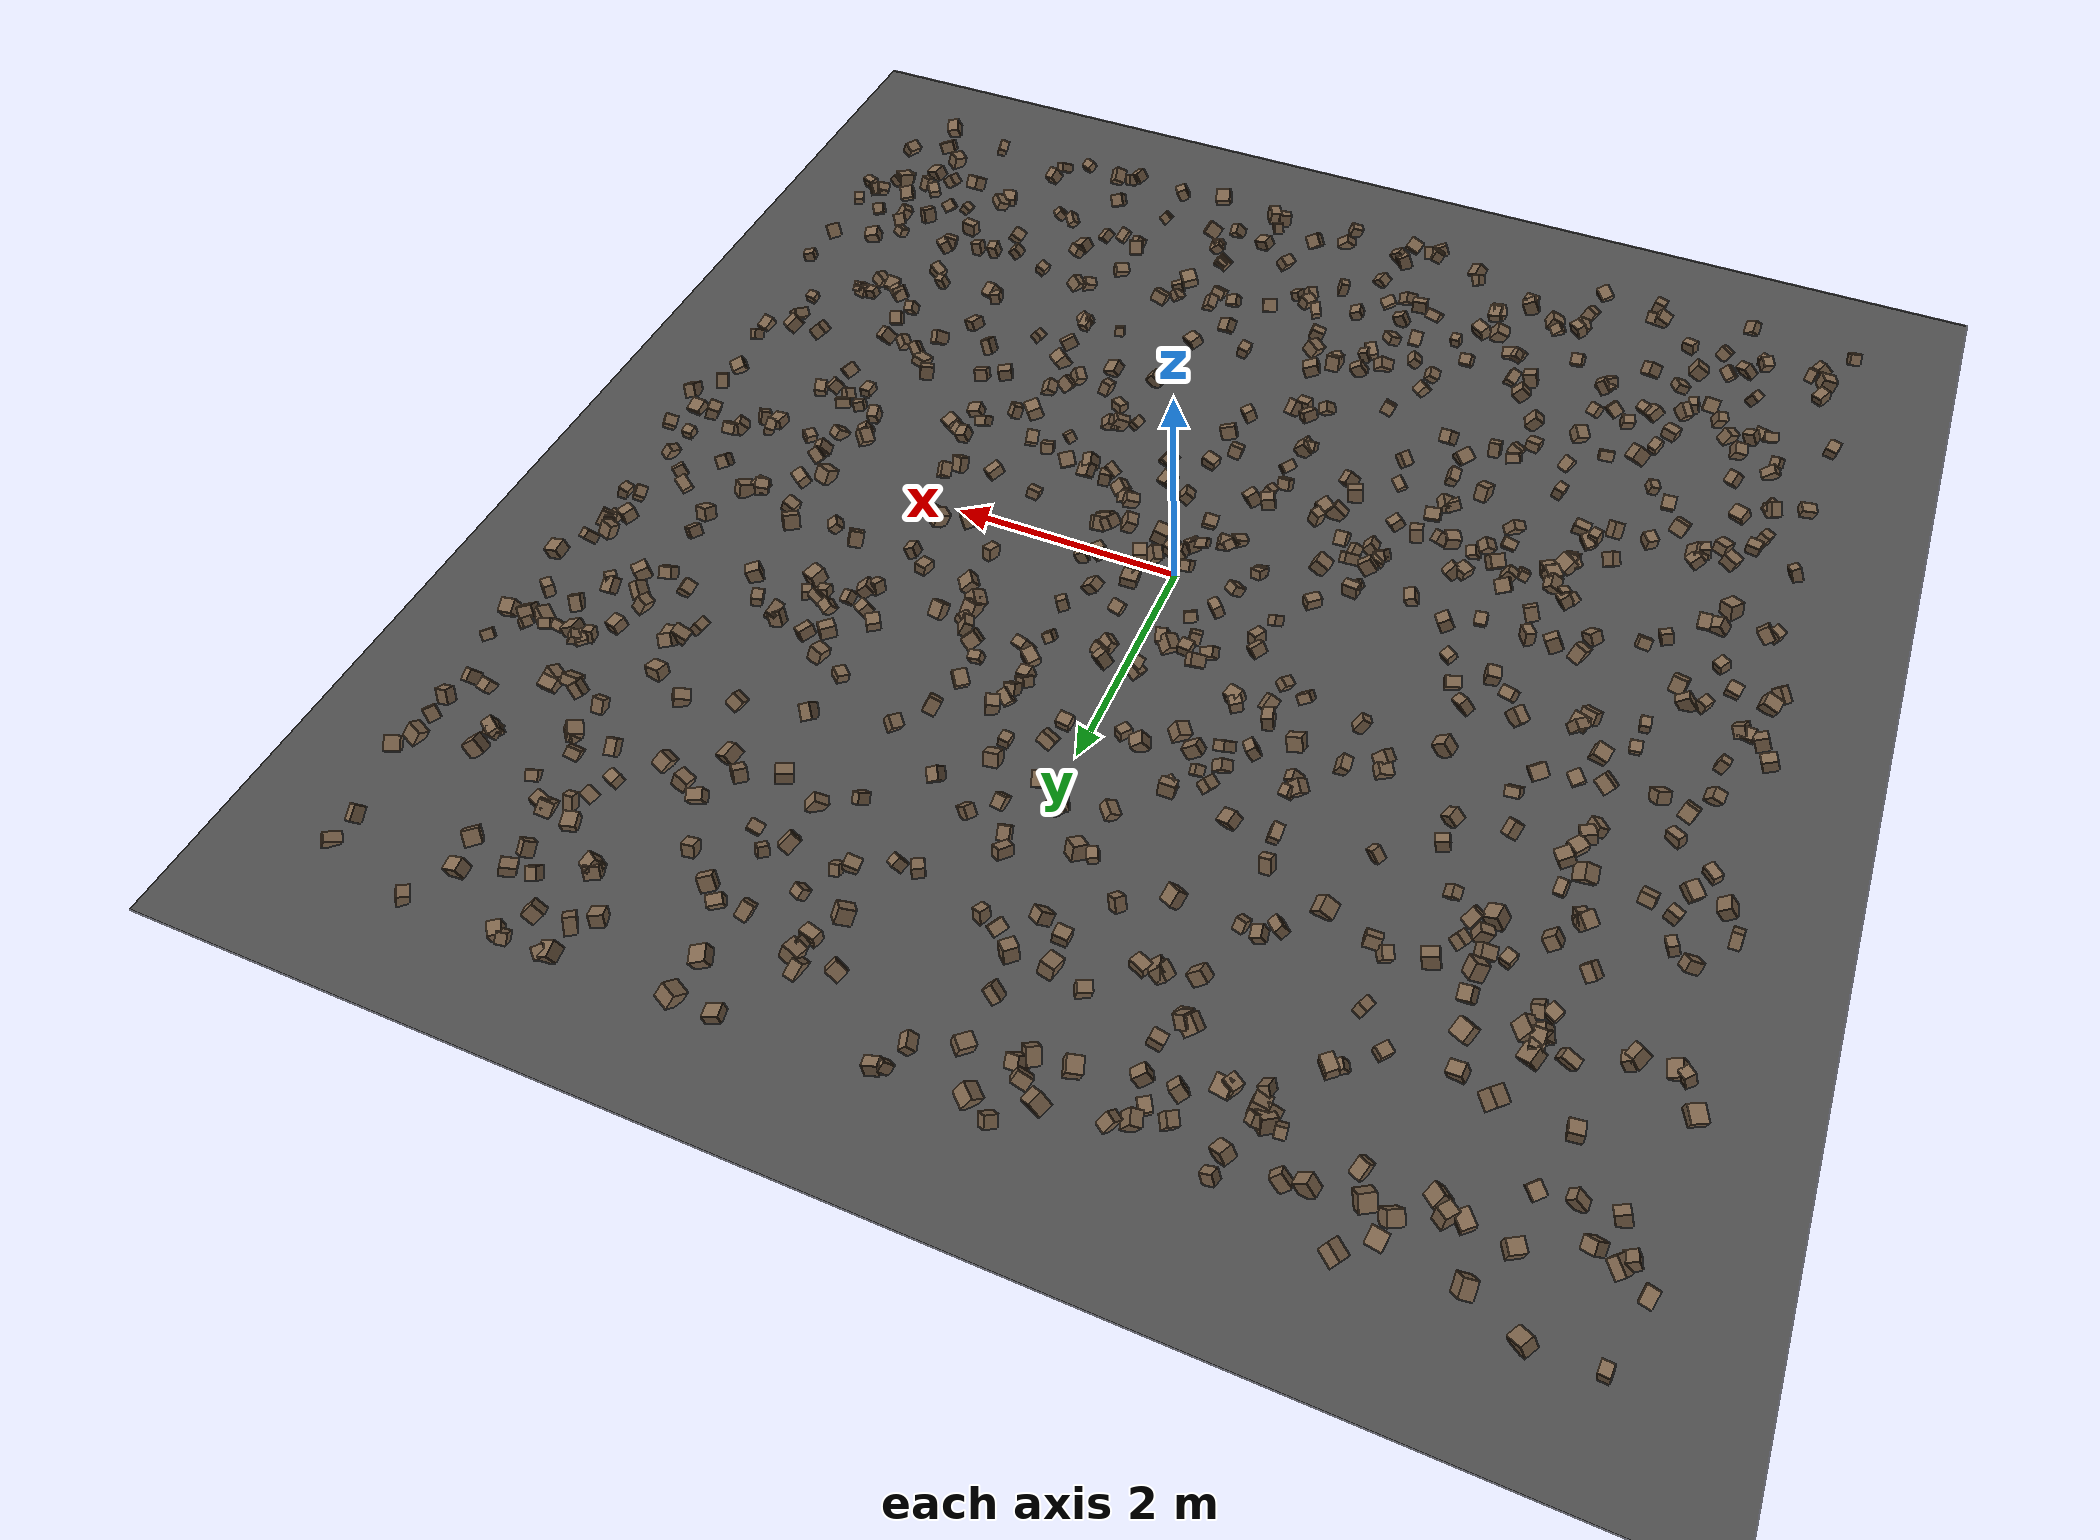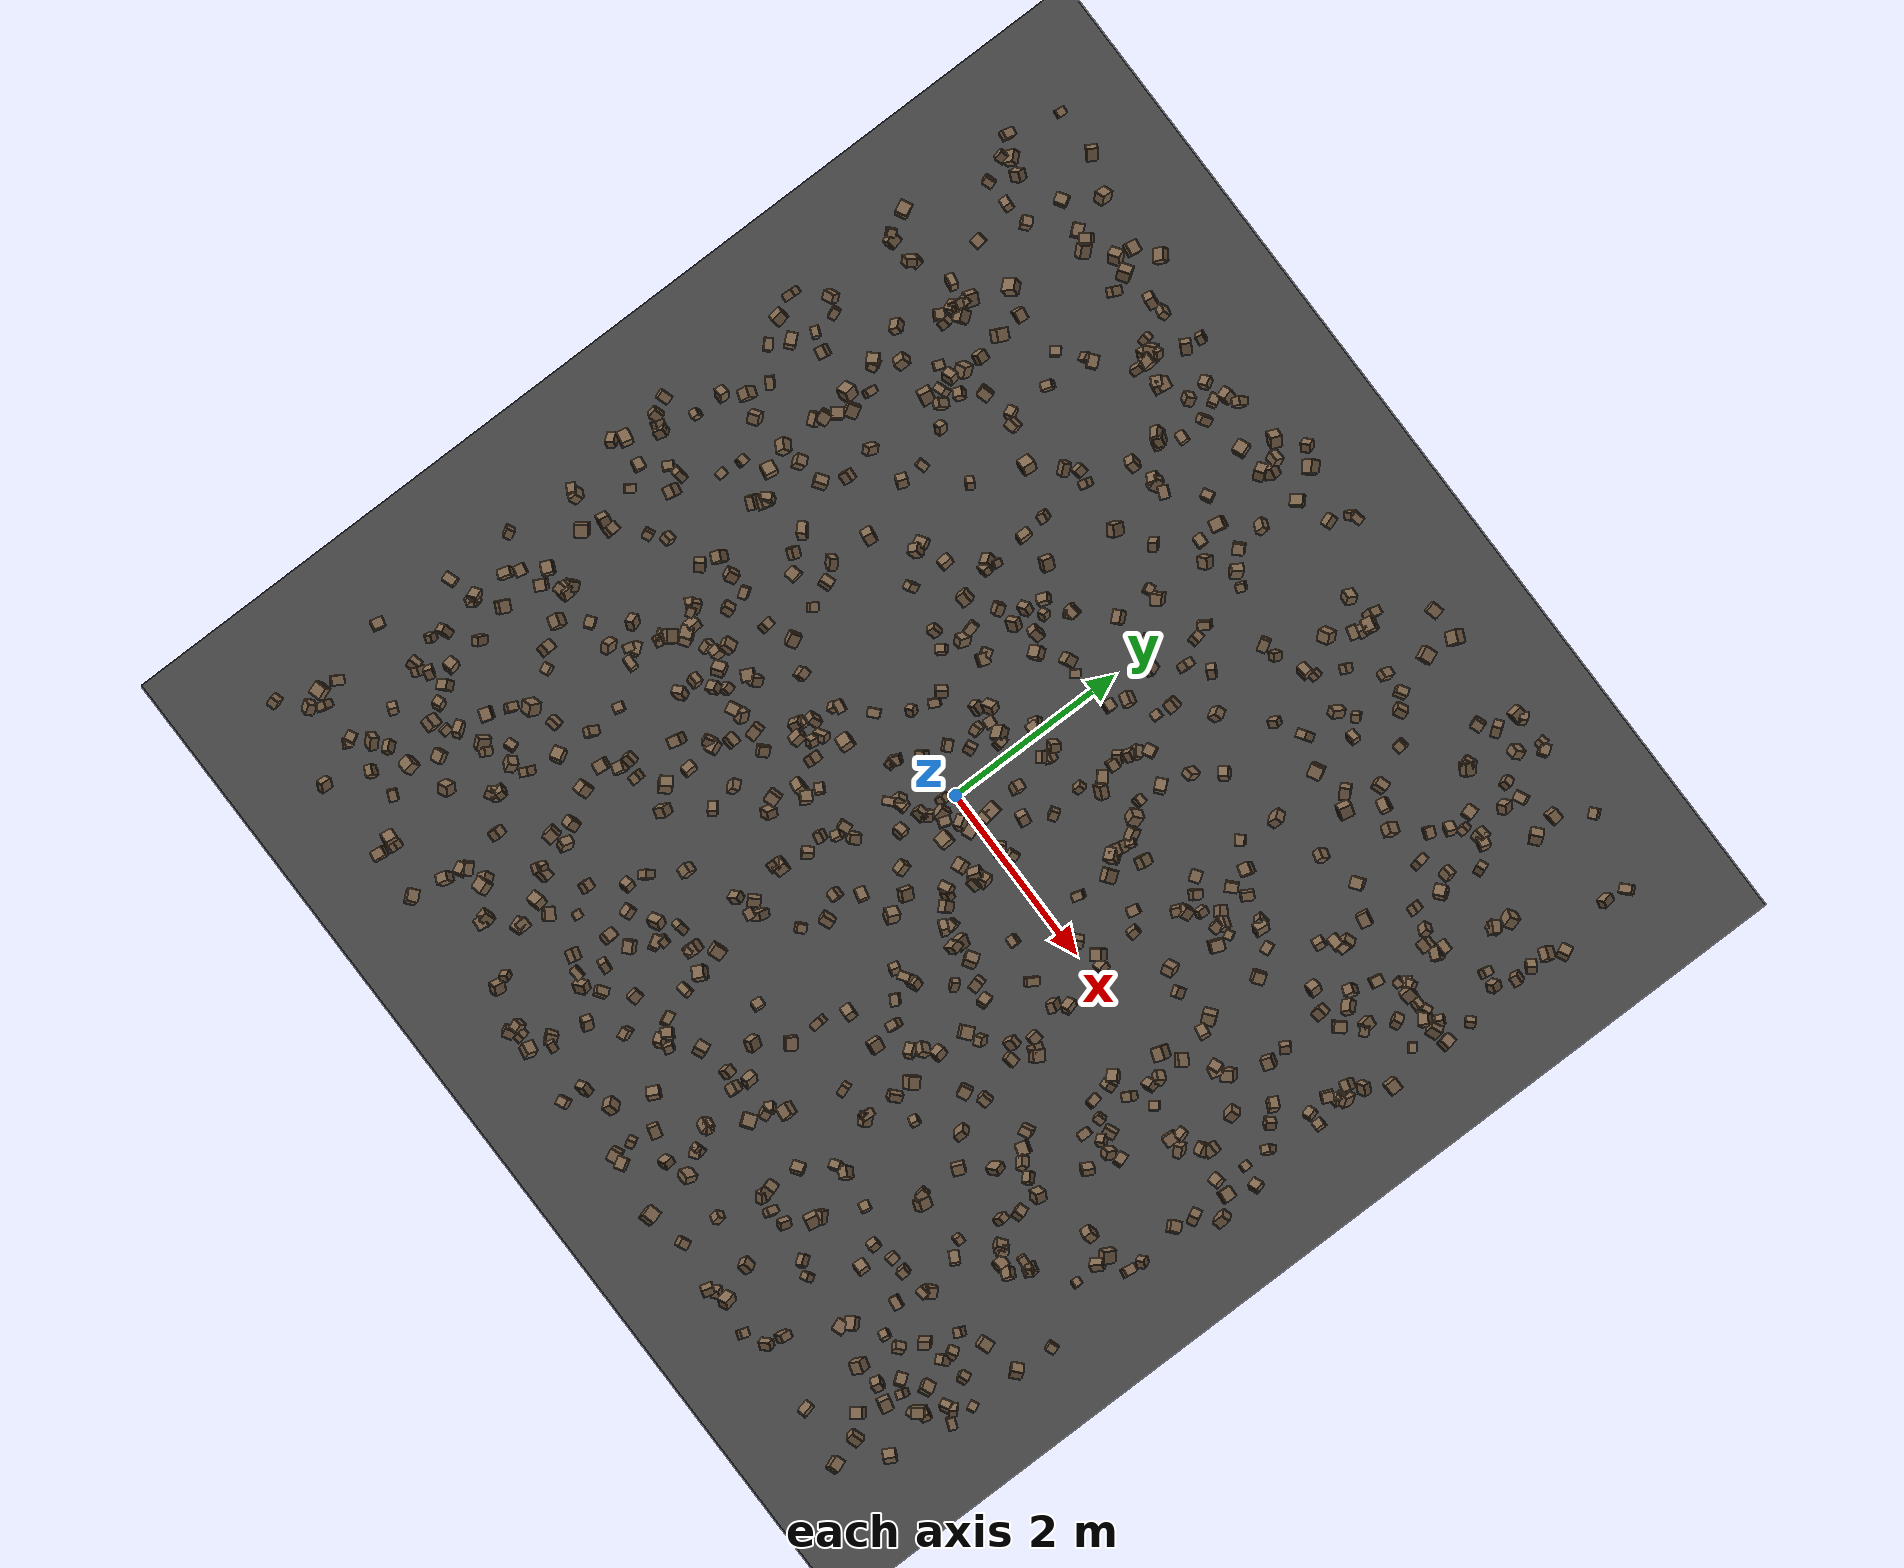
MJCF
<mujoco model="rocky_terrain_scene">
    <compiler angle="radian" inertiafromgeom="true" />
    <option timestep="0.002" gravity="0 0 -9.81" />

    <worldbody>
        <light name="sunlight" pos="5 5 5" dir="-1 -1 -1" diffuse="1 1 1" specular="0.5 0.5 0.5" ambient="0.5 0.5 0.5" />

        <geom name="ground_plane" type="plane" size="50 50 0.1" rgba="0.3 0.3 0.3 1" />

        <body name="rocky_terrain_body">

        <geom name="rock1" type="box" size="0.06091757121184091 0.05228307979930348 0.04184403301235062" pos="-0.023491310516543962 -0.34308210797259964 0.044465980755753635" quat="0.24818713209481522 0.4235065186480487 0.19629987528568077 0.1320064739714553" rgba="0.5 0.4 0.3 1" friction="0.8368463493959065 0.9892352020048237 0.8341923358248222" /><geom name="rock2" type="box" size="0.06891144334652675 0.05184521719941075 0.05661779644702826" pos="-2.2395031783863253 -0.34648616618011374 0.02517405690789554" quat="0.10662179602936268 0.26261994377222214 0.35101207294328796 0.27974618725512723" rgba="0.5 0.4 0.3 1" friction="0.8132851769103926 0.9310790152196731 0.8418141352815977" /><geom name="rock3" type="box" size="0.04645305982155889 0.04186102991392052 0.04719347857527912" pos="-2.374552309706929 0.004378245809929737 0.048389561094428823" quat="0.3563918242232241 0.2973723127082106 0.23054306256143467 0.11569280050713063" rgba="0.5 0.4 0.3 1" friction="0.8231612622947913 0.9770127331087779 0.8333522048831362" /><geom name="rock4" type="box" size="0.04761762837003475 0.06498043755236911 0.06563757491884722" pos="-1.8789941479437844 -3.7528097172232497 0.02077542706867604" quat="0.2635207388167635 0.20789770601740196 0.3592778992173094 0.16930365594852512" rgba="0.5 0.4 0.3 1" friction="0.8155573093370112 0.9914456347550684 0.9023707362043526" /><geom name="rock5" type="box" size="0.05186905757148019 0.0466086950416274 0.04153179799475284" pos="1.3359596678722596 2.9861540615161486 0.037922070331274094" quat="0.1681685368580961 0.4521259933886869 0.14003870267570076 0.23966676707751633" rgba="0.5 0.4 0.3 1" friction="0.8009532077123872 0.9046809239455954 0.9230908769903898" /><geom name="rock6" type="box" size="0.05116285080682305 0.04642042672557126 0.06092381064008745" pos="-2.6123550008642473 2.7018870721066923 0.05506510497420619" quat="0.4215738665894948 0.07264427867800023 0.35893508570683447 0.1468467690256705" rgba="0.5 0.4 0.3 1" friction="0.888718416901746 0.936746595468404 0.94092490287059" /><geom name="rock7" type="box" size="0.0644331241889921 0.051618912869807604 0.04698932808230269" pos="-2.4861518307274477 0.26632698413742073 0.058626769742563103" quat="0.5246131458555703 0.33056521937979133 0.053062038755052894 0.09175959600958557" rgba="0.5 0.4 0.3 1" friction="0.783245518183112 0.9058883216660097 0.8819568486469508" /><geom name="rock8" type="box" size="0.05694580464127351 0.0500707670974437 0.04614762277799713" pos="-0.16163948140907536 0.6776622447562408 0.0411531238887851" quat="0.2588159354904912 0.18495913287128826 0.33778586085484447 0.21843907078337604" rgba="0.5 0.4 0.3 1" friction="0.7887602504525806 0.873307055307231 0.9342244203926113" /><geom name="rock9" type="box" size="0.047241095243399096 0.06187916022113464 0.05903403406231304" pos="4.355426629437005 -0.10474374659375751 0.05190946771469322" quat="0.35910026467510314 0.1361487861619806 0.37031633896021493 0.13443461020270145" rgba="0.5 0.4 0.3 1" friction="0.7927546445709923 0.9136589585097711 0.8186666206739519" /><geom name="rock10" type="box" size="0.06798020105925369 0.04539149257182153 0.05734281394424247" pos="4.024268860715679 -0.3632374209010951 0.03630573436446552" quat="0.21877292081412927 0.28775080866276437 0.24322111670478394 0.25025515381832236" rgba="0.5 0.4 0.3 1" friction="0.7502174102935874 0.9631920018465531 0.8309892990464056" /><geom name="rock11" type="box" size="0.04564316102402819 0.05309080151850913 0.06961327156620313" pos="-4.504262279960457 -2.233400034068257 0.055833544961655074" quat="0.1341080220939569 0.022318007879545586 0.3570213293358633 0.4865526406906343" rgba="0.5 0.4 0.3 1" friction="0.8342445123061554 0.9024890583674363 0.9286674032679272" /><geom name="rock12" type="box" size="0.049939893306577963 0.059786300730659506 0.06047545804655623" pos="3.0314612061571484 4.734127275592156 0.03369994916793585" quat="0.013195808134269595 0.3221454557337347 0.40081691228468935 0.2638418238473063" rgba="0.5 0.4 0.3 1" friction="0.8311212934128261 0.9043817187220288 0.8209319959653805" /><geom name="rock13" type="box" size="0.06866941999012896 0.05141592613126946 0.06979876377575973" pos="1.3270741931271122 -3.611607954458206 0.04878371184746613" quat="0.1892599682445903 0.1520757505770402 0.3678709526293451 0.29079332854902434" rgba="0.5 0.4 0.3 1" friction="0.8410453229312611 0.8973935568576438 0.9468311163997557" /><geom name="rock14" type="box" size="0.053961160280755656 0.047039023863928976 0.06855609107748517" pos="0.5755925576100491 0.40184951241837297 0.05953637278965104" quat="0.16484313573457032 0.37729688888470775 0.33408697697791856 0.12377299840280337" rgba="0.5 0.4 0.3 1" friction="0.7689564862694995 0.9664298947235764 0.8685704042150044" /><geom name="rock15" type="box" size="0.04029893323869618 0.04801496737456829 0.06812706490030572" pos="-0.35859161185824107 -0.5546516420381922 0.021016229232647544" quat="0.19394059373220096 0.1117186804555325 0.27363431477096095 0.4207064110413057" rgba="0.5 0.4 0.3 1" friction="0.8820460802291248 0.8512762416154515 0.8504997625972055" /><geom name="rock16" type="box" size="0.04195833054225265 0.0433428119643034 0.049602672767192026" pos="3.4331495585689726 -0.8046104749957568 0.051649838393961534" quat="0.14912617496981992 0.29041394253128633 0.269124347359124 0.2913355351397697" rgba="0.5 0.4 0.3 1" friction="0.8955164924421064 0.927558709510204 0.9038630340389465" /><geom name="rock17" type="box" size="0.048395795108509464 0.04088240220393292 0.04526850986910778" pos="0.26387289421019133 -3.8081274285198763 0.025529232498819113" quat="0.4729126255360258 0.12379302175857618 0.04705222199793796 0.3562421307074601" rgba="0.5 0.4 0.3 1" friction="0.8727182451449462 0.8767772682555701 0.9172800251418969" /><geom name="rock18" type="box" size="0.05375346905042334 0.04778051583857765 0.05794470856230296" pos="-0.26322934773967077 -0.4834226332373106 0.03055255746323137" quat="0.28822951681035436 0.15231703750476805 0.2529556142887339 0.3064978313961438" rgba="0.5 0.4 0.3 1" friction="0.8767984591838388 0.9828328726265132 0.9379289243911417" /><geom name="rock19" type="box" size="0.049640792171351866 0.06312321219655019 0.06490472470923148" pos="-2.7736300400628755 4.552464168701036 0.03515658815357393" quat="0.38452901515908056 0.1682111440051203 0.08776870586589801 0.3594911349699011" rgba="0.5 0.4 0.3 1" friction="0.8043818596185578 0.8574652604026185 0.8074648262285048" /><geom name="rock20" type="box" size="0.06508588560505595 0.053125235265479236 0.0687393360068238" pos="1.478681377410438 -3.2535895782161193 0.051573966052115325" quat="0.22102541925707236 0.2884770547979463 0.1467699450594113 0.34372758088557004" rgba="0.5 0.4 0.3 1" friction="0.8778162059218233 0.8787614002021804 0.9100357910450675" /><geom name="rock21" type="box" size="0.059030982571728646 0.05241504380237619 0.06206939010734497" pos="0.579631621179737 2.2742275133091194 0.03361830242295985" quat="0.37234115473462776 0.09084203134582805 0.4247729118647063 0.11204390205483802" rgba="0.5 0.4 0.3 1" friction="0.8959683075387043 0.9785756431262228 0.8199394867060438" /><geom name="rock22" type="box" size="0.04093866786081355 0.05819645776938957 0.04585716336728589" pos="1.2503535103749535 -4.186874509661464 0.03554632068567192" quat="0.3136913333632246 0.1115315318923871 0.1569201246688367 0.41785701007555176" rgba="0.5 0.4 0.3 1" friction="0.844884785051447 0.8842616120207637 0.8858697996554736" /><geom name="rock23" type="box" size="0.059510259091340376 0.05712753282968068 0.041204683238715074" pos="1.528962466673284 0.37252258730582355 0.053011290466512304" quat="0.25203281324575905 0.32395172164030805 0.18355310287921392 0.24046236223471903" rgba="0.5 0.4 0.3 1" friction="0.7717415747861183 0.871741115425269 0.9289144347501402" /><geom name="rock24" type="box" size="0.045759418350034095 0.041647468578141625 0.041767286523392594" pos="-0.917569097299368 1.8004729345630874 0.037782590916408856" quat="0.04467069972329877 0.26515808246101524 0.15381524030751556 0.5363559775081704" rgba="0.5 0.4 0.3 1" friction="0.7691771252792 0.9666202326528615 0.9292109451573672" /><geom name="rock25" type="box" size="0.06982380042555049 0.05879408872534566 0.06462634497306159" pos="2.7623339378774485 1.1707382364862742 0.05446666091074928" quat="0.5581780505501102 0.007944788831109044 0.054746136247234255 0.37913102437154667" rgba="0.5 0.4 0.3 1" friction="0.8529959253460889 0.9621742137362581 0.8601040801038572" /><geom name="rock26" type="box" size="0.058002983251185275 0.05751361490737052 0.044896441124860416" pos="-0.8733120731684121 3.8223355685849096 0.04324632675101095" quat="0.4226095790313357 0.37812935846566886 0.055883076060409945 0.1433779864425855" rgba="0.5 0.4 0.3 1" friction="0.7561278638799223 0.9138002005780694 0.8042861722433032" /><geom name="rock27" type="box" size="0.040019129282767255 0.06406312328408083 0.06394078144746011" pos="-3.2977066339283354 4.719487305018276 0.04915236882393921" quat="0.11302171126554483 0.40859800577286937 0.054007024649342754 0.424373258312243" rgba="0.5 0.4 0.3 1" friction="0.8377354409267012 0.9017706860811526 0.8641173042177502" /><geom name="rock28" type="box" size="0.05528938960551017 0.0659038155808111 0.05069136711480633" pos="0.8383564764433746 -4.423851758524244 0.04462424087913157" quat="0.48261078926943607 0.0646460407561763 0.08593739700320505 0.3668057729711825" rgba="0.5 0.4 0.3 1" friction="0.8680046578987459 0.902319756403793 0.93068787328171" /><geom name="rock29" type="box" size="0.06573830176008408 0.05216913441583773 0.06266059214198674" pos="1.3880468150711058 -0.8689779334075016 0.05685779760211147" quat="0.5246995630869349 0.2373522102648389 0.10189567575294074 0.13605255089528545" rgba="0.5 0.4 0.3 1" friction="0.8684640676390103 0.9590857552848392 0.9260431828724988" /><geom name="rock30" type="box" size="0.05034320262516098 0.041547535125237026 0.04728715195102001" pos="2.7139872415606723 -3.206330106683443 0.05861182219141936" quat="0.32599403204598604 0.22903662738263197 0.18430058331174667 0.2606687572596353" rgba="0.5 0.4 0.3 1" friction="0.7965104608865701 0.9689865419075081 0.9095559165797572" /><geom name="rock31" type="box" size="0.05054272625119985 0.04958746098667745 0.04258284676769651" pos="1.4131710831910196 1.1124020314214516 0.032090662677496204" quat="0.14047476564789405 0.1472294571719275 0.6563156907572196 0.055980086422958784" rgba="0.5 0.4 0.3 1" friction="0.8801151311941338 0.9877050196513245 0.9158651452738099" /><geom name="rock32" type="box" size="0.0598197787803416 0.04433479988696598 0.0496361746980036" pos="-1.0706260090047746 -3.308979443461948 0.037615478730620266" quat="0.27795251925786074 0.1438976164855625 0.17173474744216186 0.4064151168144149" rgba="0.5 0.4 0.3 1" friction="0.8593641343595633 0.9865651762244981 0.8742977164102123" /><geom name="rock33" type="box" size="0.05043749536546491 0.05731067301410263 0.04923324807576498" pos="-0.8225286611968006 -4.882919805176166 0.03865009986423953" quat="0.5131432559296851 0.013906256144906919 0.32531935896338576 0.14763112896202224" rgba="0.5 0.4 0.3 1" friction="0.8527328459147552 0.8986874278147966 0.8634305051217627" /><geom name="rock34" type="box" size="0.0405113901880981 0.048777117519851115 0.05052238430040459" pos="4.667139169816284 -3.451908685393775 0.056731613010255796" quat="0.06292523303633356 0.3644835367932443 0.21968120197807262 0.35291002819234957" rgba="0.5 0.4 0.3 1" friction="0.8069132207959875 0.9908942154508472 0.8949356098449808" /><geom name="rock35" type="box" size="0.05858077869512689 0.047986242443359285 0.049047205260785355" pos="0.9968430913079107 -0.8094659109215732 0.03959684912457296" quat="0.47510109115434873 0.0035945493652411327 0.41130272109300503 0.11000163838740518" rgba="0.5 0.4 0.3 1" friction="0.8818229548179706 0.9455928908051648 0.8469012965896234" /><geom name="rock36" type="box" size="0.05118607303256013 0.04937322874453744 0.05932785652483226" pos="-1.7619776131145848 4.258674711105561 0.03664048318027077" quat="0.247127896734101 0.20184132766308516 0.03707253346688767 0.5139582421359261" rgba="0.5 0.4 0.3 1" friction="0.8793785028172827 0.9389243191192009 0.8168368103300998" /><geom name="rock37" type="box" size="0.055224684354474626 0.04264136054341305 0.062412954293109495" pos="-1.8650374467493522 -4.541363211613697 0.04825398326136736" quat="0.2451706048173687 0.2769300789553133 0.21826796672173762 0.25963134950558037" rgba="0.5 0.4 0.3 1" friction="0.8621485810388108 0.8737850109821517 0.9300482274358894" /><geom name="rock38" type="box" size="0.069319217768615 0.045051567365753935 0.06788731353298373" pos="0.3257532196649535 0.2019610041560549 0.04961880297625579" quat="0.45477193475917704 0.48991388265352903 0.008414631493933889 0.04689955109336006" rgba="0.5 0.4 0.3 1" friction="0.8302514920155492 0.9740475155401077 0.9334609302209402" /><geom name="rock39" type="box" size="0.060569254270147366 0.0632637877123841 0.044980821579231015" pos="3.253344579403967 -0.7483174993371584 0.04494857347579884" quat="0.25051705387010864 0.1988334984411485 0.30456013377566216 0.24608931391308084" rgba="0.5 0.4 0.3 1" friction="0.8260303111364684 0.8634213353324877 0.8253000874019837" /><geom name="rock40" type="box" size="0.045250794054513245 0.05503729338095191 0.04258091500774705" pos="4.662081159612168 0.9004154736198497 0.053515256041000644" quat="0.048869990865820306 0.649197854432742 0.10282267345755941 0.19910948124387823" rgba="0.5 0.4 0.3 1" friction="0.7665990240479731 0.9805194274172923 0.9274306396459546" /><geom name="rock41" type="box" size="0.06896030711512141 0.06922097130880989 0.04658469075590438" pos="-3.047201906278479 0.3853603012660143 0.039785961503903275" quat="0.23060858034919296 0.0431213664716171 0.3681810486825084 0.3580890044966816" rgba="0.5 0.4 0.3 1" friction="0.8997909939489255 0.8581390243992134 0.9248188115192355" /><geom name="rock42" type="box" size="0.06463925254013574 0.04765863131705199 0.05934591712758043" pos="-2.9605399132282004 -1.0604606032919972 0.05064632327628074" quat="0.3504097119089002 0.10635630527780797 0.2013372991424843 0.3418966836708075" rgba="0.5 0.4 0.3 1" friction="0.7911596943022577 0.9393200182901004 0.913363221062358" /><geom name="rock43" type="box" size="0.043665181139645945 0.04283241952309093 0.043245707360794514" pos="-4.445376705781257 -3.219516499267334 0.03400780463381775" quat="0.30469033674909546 0.24862114789128986 0.38279535486442895 0.06389316049518569" rgba="0.5 0.4 0.3 1" friction="0.8907780013418045 0.9051342002174602 0.8330741986552416" /><geom name="rock44" type="box" size="0.058946184157236604 0.06352853991733118 0.054365388230824346" pos="-4.101308343576104 -3.225538533756441 0.03972505838047026" quat="0.2886651539798958 0.15646946058085257 0.272408680017118 0.28245670542213375" rgba="0.5 0.4 0.3 1" friction="0.8640863369345034 0.8972956521162231 0.9164210457602778" /><geom name="rock45" type="box" size="0.06085390485935155 0.06894525151334459 0.04199600409662008" pos="3.252642068725226 -4.637996974663944 0.043544650067602185" quat="0.29596606950261733 0.25018629820623733 0.308449505082514 0.14539812720863138" rgba="0.5 0.4 0.3 1" friction="0.8728106125911866 0.9936909619206145 0.875548705731866" /><geom name="rock46" type="box" size="0.057487960786458125 0.042123502304662025 0.062131549588187784" pos="4.745371830598234 -0.8655091553217282 0.03626201092949751" quat="0.1712832648174904 0.14109299570525427 0.432673157491493 0.25495058198576226" rgba="0.5 0.4 0.3 1" friction="0.8600836135793138 0.8584177236992141 0.8900400905188428" /><geom name="rock47" type="box" size="0.06025030871408347 0.06835057456919352 0.043779560912139234" pos="-0.2465092960289148 -2.2735968562810305 0.03600263756750624" quat="0.1986373537036652 0.4465718136683754 0.0684244386921842 0.2863663939357753" rgba="0.5 0.4 0.3 1" friction="0.7747399536475936 0.9374960728296355 0.9164273487587579" /><geom name="rock48" type="box" size="0.042358249410388335 0.05252559553336715 0.04903845611522471" pos="-3.954133438189146 -0.8658363784363923 0.028432735113238912" quat="0.13516506892329294 0.26476074166144314 0.28853639304277656 0.3115377963724873" rgba="0.5 0.4 0.3 1" friction="0.756530964473234 0.9652486971276906 0.8568211390887556" /><geom name="rock49" type="box" size="0.058617474947931444 0.04085094415226985 0.05227344995570478" pos="-0.05302038686744037 2.514910144821693 0.04247408243900787" quat="0.2280672933388443 0.06878967257599136 0.22468640720174327 0.47845662688342105" rgba="0.5 0.4 0.3 1" friction="0.7907746558981541 0.882440804090545 0.8901773139556143" /><geom name="rock50" type="box" size="0.059464893375610124 0.0680683068555433 0.04293952473137497" pos="-2.9058013719543863 -0.44984951465354417 0.038494553226539316" quat="0.15728220995732006 0.1865794010509211 0.30582857570305116 0.3503098132887076" rgba="0.5 0.4 0.3 1" friction="0.889686490872361 0.9435394832302902 0.949242998607186" /><geom name="rock51" type="box" size="0.05348996695456733 0.06085848136840788 0.05327806931587037" pos="-1.0438100888224722 -2.5919734194598876 0.03943322248052311" quat="0.4400932842103757 0.11704625416368848 0.3214368316291725 0.12142362999676323" rgba="0.5 0.4 0.3 1" friction="0.8908936866843752 0.9091189376961937 0.8132123225465323" /><geom name="rock52" type="box" size="0.05383418047635541 0.05702320538318453 0.055429184181214314" pos="-2.0833134297038844 4.107219094645885 0.059738576290737325" quat="0.31530594173472315 0.3082624446204478 0.14324380163829462 0.23318781200653446" rgba="0.5 0.4 0.3 1" friction="0.8218991915555265 0.9170016723045811 0.872373954047937" /><geom name="rock53" type="box" size="0.041449619173346997 0.0637157426258742 0.06081730067706759" pos="0.9706555683547737 -0.8903785384298724 0.04706926731577021" quat="0.1512287350707106 0.45617750995256395 0.31241641141695203 0.08017734355977339" rgba="0.5 0.4 0.3 1" friction="0.7851499212850628 0.8677885802274494 0.9479228946348071" /><geom name="rock54" type="box" size="0.06855414455545338 0.04168245629761415 0.05739867177495586" pos="3.755721895375828 -3.248528530149677 0.0377457696168715" quat="0.4762258476042712 0.030877978292753756 0.3929763701948108 0.09991980390816417" rgba="0.5 0.4 0.3 1" friction="0.7578949382052692 0.924342677741682 0.9287356675872898" /><geom name="rock55" type="box" size="0.05730962041947556 0.050692291768938774 0.05522276467354211" pos="-0.061543264130064834 -0.6512789930281491 0.05160567394563373" quat="0.1524323590948798 0.6924057565619496 0.04886493651163306 0.10629694783153755" rgba="0.5 0.4 0.3 1" friction="0.8068842148286081 0.94794446035713 0.9017663425363973" /><geom name="rock56" type="box" size="0.04146672949663595 0.06016703530125263 0.06408662618676741" pos="-1.025580618559058 1.5027683520274104 0.029272081260611194" quat="0.25819131241187204 0.25708010329123604 0.4338457695322987 0.050882814764593144" rgba="0.5 0.4 0.3 1" friction="0.8520755791579315 0.8904214365593445 0.8595383477084643" /><geom name="rock57" type="box" size="0.05260576460988125 0.04737670922102223 0.04293316007598998" pos="-3.8001862806705566 -0.732635969621036 0.03130377168182162" quat="0.2835859703986053 0.6154391008983884 0.004605475309533835 0.09636945339347265" rgba="0.5 0.4 0.3 1" friction="0.7542209736692816 0.971623802848792 0.9137192919255843" /><geom name="rock58" type="box" size="0.054159653604506475 0.04859594801385942 0.047674625166878364" pos="-1.8511656754430836 2.9549648716252674 0.04501886504575227" quat="0.18818014401146047 0.27900807526335786 0.3438645599365111 0.18894722078867052" rgba="0.5 0.4 0.3 1" friction="0.8701184485552957 0.9941737527492278 0.9175142967900384" /><geom name="rock59" type="box" size="0.05056135006456125 0.06359080098177233 0.06422560526974148" pos="2.662503840763372 3.3557045145431896 0.03530009485273354" quat="0.020146360381162822 0.47187413285277435 0.38400323947851944 0.12397626728754335" rgba="0.5 0.4 0.3 1" friction="0.862768974778131 0.9409942588687489 0.8846168461568258" /><geom name="rock60" type="box" size="0.05670202271884856 0.05197703941265252 0.06320508517515061" pos="3.6900503879643747 1.6843563465966014 0.0419900420245822" quat="0.15891973572996426 0.36731431194429304 0.3858736179869327 0.08789233433881001" rgba="0.5 0.4 0.3 1" friction="0.8842277583304227 0.908495194817281 0.8181720209646163" /><geom name="rock61" type="box" size="0.0518504515102514 0.05490631015041096 0.059208019395404814" pos="3.524065374130391 2.229289330306303 0.058441384834289914" quat="0.07699188028658593 0.3757293076471147 0.2291851074768612 0.31809370458943814" rgba="0.5 0.4 0.3 1" friction="0.8150283614774131 0.9480755992939719 0.9039071552163499" /><geom name="rock62" type="box" size="0.056014765313522244 0.048061679693261396 0.06590759239247188" pos="4.6635068819922925 1.3705304533294935 0.059481815873219296" quat="0.06678278061465676 0.08513675682615268 0.67606845808736 0.17201200447183046" rgba="0.5 0.4 0.3 1" friction="0.804962798258638 0.9519451106192237 0.8437559002082732" /><geom name="rock63" type="box" size="0.04060328820314647 0.05723801751828684 0.04795163925138959" pos="-4.587164695807468 1.9534707866094303 0.05544422300937517" quat="0.6789886700885323 0.08510613486931644 0.10138899504018044 0.13451620000197081" rgba="0.5 0.4 0.3 1" friction="0.761594668329085 0.9575970620933288 0.8993451141217753" /><geom name="rock64" type="box" size="0.04223994874530977 0.042412578364201016 0.04856725780559837" pos="4.547646574033431 2.4476009066690105 0.04856680478324737" quat="0.2971583051578346 0.10515225486632583 0.36124752274208655 0.23644191723375307" rgba="0.5 0.4 0.3 1" friction="0.7517601069736732 0.8671502717276737 0.8310217770714725" /><geom name="rock65" type="box" size="0.04727381849412646 0.06027306123806489 0.04408584113256632" pos="-2.249883559105755 -1.175757454000923 0.021032716945359606" quat="0.21656432591551258 0.23252177582102326 0.3815380122806023 0.16937588598286185" rgba="0.5 0.4 0.3 1" friction="0.801038692511067 0.9950896249781468 0.9137369999900603" /><geom name="rock66" type="box" size="0.05649978406651199 0.0675183944523711 0.04176764595233644" pos="3.3248458857508663 3.298001693216033 0.05569258563762164" quat="0.09111568673090875 0.36156037171772726 0.1539131656388728 0.39341077591249113" rgba="0.5 0.4 0.3 1" friction="0.7863418210023376 0.8781365024814819 0.8283691639017338" /><geom name="rock67" type="box" size="0.061196660867876916 0.043212809466402755 0.04000672696303153" pos="-3.7444688083038544 1.7654676530846007 0.02882927106256719" quat="0.29151518891992906 0.2386320703677467 0.31004077803613095 0.15981196267619324" rgba="0.5 0.4 0.3 1" friction="0.78079002932393 0.955890409514573 0.8137746498460307" /><geom name="rock68" type="box" size="0.04923375686013673 0.04120284000207403 0.06811541758547496" pos="-4.109786657738166 -4.52123125844145 0.02920045144596791" quat="0.18113132268616303 0.004206212237039742 0.11754246004645859 0.6971200050303387" rgba="0.5 0.4 0.3 1" friction="0.8300708200295412 0.8755290593529151 0.8620036800860684" /><geom name="rock69" type="box" size="0.05125006361026463 0.05820111255397069 0.06601768638466396" pos="3.7217170382165445 0.43208584690196083 0.046115327094144835" quat="0.08934407180598201 0.3659133984296815 0.5298714823079151 0.014871047456421344" rgba="0.5 0.4 0.3 1" friction="0.8313400595979673 0.8705051301677332 0.9224535676037888" /><geom name="rock70" type="box" size="0.04517866330601036 0.0664156878295693 0.06698806816454651" pos="3.666757872925384 -3.536701270570888 0.04358250837410902" quat="0.262808043129652 0.27653741483461086 0.21915964562497828 0.24149489641075894" rgba="0.5 0.4 0.3 1" friction="0.8276277403138651 0.9084168569909056 0.9217915310706032" /><geom name="rock71" type="box" size="0.06379044762748795 0.06599038983069413 0.04910246394280268" pos="2.480552538145534 3.447007353944839 0.054125683465811175" quat="0.5062798602118807 0.3424988397103459 0.0888120883255794 0.062409211752193966" rgba="0.5 0.4 0.3 1" friction="0.816057329144142 0.8756215016467708 0.8430202446069791" /><geom name="rock72" type="box" size="0.04801721541134957 0.0400292893789251 0.0550437787840312" pos="-2.9430696729005588 3.484589207495283 0.04746361798246471" quat="0.17135207986773032 0.08597938654201331 0.3662584099332387 0.3764101236570177" rgba="0.5 0.4 0.3 1" friction="0.784027414072405 0.9412869972499054 0.8398909707322004" /><geom name="rock73" type="box" size="0.06901543521598347 0.05575176703151864 0.06086515915004728" pos="-4.323407792279797 -1.136529200010683 0.027229585285506522" quat="0.07260522152361748 0.20774502320821597 0.044211647071595896 0.6754381081965707" rgba="0.5 0.4 0.3 1" friction="0.7757887552696892 0.9515579865001443 0.9454396474813236" /><geom name="rock74" type="box" size="0.06394737859881582 0.06588630928964723 0.058786128070220794" pos="4.756867680766433 1.2716945207859887 0.05656175504842208" quat="0.1500245605359819 0.2421268721951588 0.14655971168525192 0.46128885558360744" rgba="0.5 0.4 0.3 1" friction="0.7863264705476978 0.8692565104203899 0.853375742096752" /><geom name="rock75" type="box" size="0.04354458986351805 0.054943933376696966 0.052193109845176576" pos="4.405278080269991 -3.397755123099567 0.03059251897763232" quat="0.04425886961638985 0.3279175347217077 0.2585954619077718 0.3692281337541307" rgba="0.5 0.4 0.3 1" friction="0.8015745746930908 0.8878678934387171 0.9205564959698597" /><geom name="rock76" type="box" size="0.05547483800854086 0.04645211567248833 0.0654645868705858" pos="-0.09140064800679948 1.0697582414782332 0.031276196043522636" quat="0.3045816455113993 0.2913570881233367 0.08902462650104007 0.31503663986422387" rgba="0.5 0.4 0.3 1" friction="0.8383214765904027 0.8600119042823634 0.9066485705951886" /><geom name="rock77" type="box" size="0.06512607283548617 0.05920369021087027 0.050864858104640955" pos="-4.817504943080891 2.8584771429912585 0.0248244566366004" quat="0.35070274880635255 0.04947812260504699 0.15763615068075765 0.4421829779078427" rgba="0.5 0.4 0.3 1" friction="0.7757631315312767 0.9239973411294516 0.949462226045976" /><geom name="rock78" type="box" size="0.06657975125632314 0.06810642240083391 0.06578355069499837" pos="-3.372422172263616 2.185218290786075 0.03919052066750729" quat="0.1977255816778169 0.34349691992302317 0.28987502471823806 0.1689024736809219" rgba="0.5 0.4 0.3 1" friction="0.786562510178354 0.9352324575501482 0.8107880196192832" /><geom name="rock79" type="box" size="0.04925571488321681 0.06608149515763165 0.041861809982200515" pos="3.6348124949543656 -2.1958894889264133 0.05237478648293904" quat="0.2821960176957341 0.18769565152278309 0.3559728356600719 0.17413549512141097" rgba="0.5 0.4 0.3 1" friction="0.8366124721390898 0.9629868222323121 0.8798851589322494" /><geom name="rock80" type="box" size="0.060438792613832386 0.04362570860883616 0.04509923408407038" pos="1.2497526689965834 -1.7165349484416135 0.02335646348840075" quat="0.10132610178559621 0.1083620287424923 0.36156813436809304 0.4287437351038185" rgba="0.5 0.4 0.3 1" friction="0.7614972576063712 0.9606498971561879 0.8734359317088154" /><geom name="rock81" type="box" size="0.05391787917214484 0.06263127714386633 0.06562613437697129" pos="-1.5309222356563632 1.2717401420573964 0.049103535264726966" quat="0.1498311736190964 0.3437890123144707 0.22967083548137554 0.27670897858505744" rgba="0.5 0.4 0.3 1" friction="0.7955688854709241 0.9253634759250273 0.8771936359683723" /><geom name="rock82" type="box" size="0.04932831518881301 0.05890311801600308 0.06584209842279123" pos="2.385401098551548 1.6470776461419545 0.05467557134825547" quat="0.1306680719302184 0.1669834837115629 0.3339800910521465 0.36836835330607215" rgba="0.5 0.4 0.3 1" friction="0.8699262930686703 0.9230996279722955 0.8295127046883286" /><geom name="rock83" type="box" size="0.06110831531074187 0.054869693512434016 0.052371206262984936" pos="-1.1652396733345949 -0.9113477336093894 0.022163228723094824" quat="0.3282517071436439 0.17416034306779385 0.3538420448783677 0.1437459049101945" rgba="0.5 0.4 0.3 1" friction="0.8707856497002837 0.9049787838837259 0.8034048193446085" /><geom name="rock84" type="box" size="0.06929812243191108 0.05288072489661868 0.06885799662361888" pos="2.459900750862073 3.012887692783531 0.04874888232490793" quat="0.20642963146665577 0.3583352746982658 0.3030878971547123 0.13214719668036617" rgba="0.5 0.4 0.3 1" friction="0.7556322194164319 0.8671863374487466 0.9102477221728618" /><geom name="rock85" type="box" size="0.06253907139964718 0.0566028214180912 0.04726870586005019" pos="-1.9095412972632264 -0.48294036669349794 0.047253980704272947" quat="0.004872202203338647 0.5147688327735597 0.12266713208839762 0.3576918329347041" rgba="0.5 0.4 0.3 1" friction="0.7511454394564602 0.9888546993547849 0.810460180003277" /><geom name="rock86" type="box" size="0.05595228492087123 0.05786048238954448 0.042149182363655315" pos="-3.401675818607184 -3.002948286146445 0.049410091569907666" quat="0.17231975022046542 0.4100991244694813 0.002763173654234179 0.414817951655819" rgba="0.5 0.4 0.3 1" friction="0.811277317126599 0.8667235921180964 0.873738643584076" /><geom name="rock87" type="box" size="0.05030666315379512 0.04122826535090825 0.0661505345074306" pos="-4.787560496877605 -2.7141763427622534 0.049010445819629336" quat="0.2350741878047366 0.1797420533726356 0.2796735521849934 0.3055102066376344" rgba="0.5 0.4 0.3 1" friction="0.781507977140671 0.9995692000118773 0.832786812441921" /><geom name="rock88" type="box" size="0.04474522828224894 0.06383784906514042 0.05417007115970017" pos="4.8413397538056575 3.361698927470375 0.04757686193989795" quat="0.17153112009270866 0.34205126119855545 0.21865219880744693 0.2677654199012889" rgba="0.5 0.4 0.3 1" friction="0.8603116865527729 0.9902456536362428 0.8220247503639025" /><geom name="rock89" type="box" size="0.06509214232420941 0.05498559340743753 0.05269825667335331" pos="-4.706545011410215 -1.20499532079259 0.022623991091155947" quat="0.2347854802616915 0.06303474646145998 0.5508459037572928 0.15133386951955574" rgba="0.5 0.4 0.3 1" friction="0.8229599813455452 0.95653074342262 0.8694774793680394" /><geom name="rock90" type="box" size="0.0650202452983384 0.05099590300690262 0.06238364405207956" pos="-2.4429408942402886 -4.5680552290208585 0.040097272279898656" quat="0.0009050129563340045 0.4851870622558961 0.3491438708669923 0.16476405392077756" rgba="0.5 0.4 0.3 1" friction="0.8272102878946505 0.9992435472913007 0.8499002666631386" /><geom name="rock91" type="box" size="0.05458218622654741 0.047502438638970856 0.04572146816568532" pos="3.9901053988226725 1.1023314265770754 0.0430384908919525" quat="0.21985319296330982 0.41274439967210297 0.21461623441571331 0.15278617294887392" rgba="0.5 0.4 0.3 1" friction="0.7659577985045761 0.9332562114561751 0.8622324661115829" /><geom name="rock92" type="box" size="0.06333206157995955 0.06711328824657445 0.06330633054022525" pos="-0.05355733731636114 1.0316785178878982 0.04190050893910463" quat="0.09632913549460556 0.4119122372016904 0.4011108318292425 0.0906477954744615" rgba="0.5 0.4 0.3 1" friction="0.8872277026840232 0.8805418756533099 0.8600847578745324" /><geom name="rock93" type="box" size="0.044309987357116824 0.053979553409542816 0.044841204368317844" pos="0.8072508587100744 3.392687768655202 0.03862219219121929" quat="0.0032212508256057623 0.19356869487178388 0.47173183948333225 0.33147821481927814" rgba="0.5 0.4 0.3 1" friction="0.7901618117379359 0.9529842044764988 0.9197473817663627" /><geom name="rock94" type="box" size="0.06679014159394046 0.05471078779156096 0.04959390744347797" pos="1.0696684246054664 -2.1598143343071587 0.03411560483413261" quat="0.2698064204600107 0.01594188388969379 0.7078061508787316 0.006445544771563935" rgba="0.5 0.4 0.3 1" friction="0.842209170490723 0.9270223529081438 0.9270016042063081" /><geom name="rock95" type="box" size="0.050094684257704775 0.051720945160194376 0.054466820145131684" pos="-1.5218801566459952 -3.484092751591258 0.044708766670895704" quat="0.31462563511020986 0.19376469360986728 0.349718701170539 0.1418909701093839" rgba="0.5 0.4 0.3 1" friction="0.8740895678123286 0.9282378521494066 0.8327134192857741" /><geom name="rock96" type="box" size="0.059938081080606206 0.06945699785643789 0.06023694976435848" pos="4.309806781412082 -4.511274268882941 0.042223112147187276" quat="0.3312713390146119 0.33335130947003044 0.11205680127526813 0.22332055024008945" rgba="0.5 0.4 0.3 1" friction="0.7556978323200935 0.9713803907658611 0.8906110718020217" /><geom name="rock97" type="box" size="0.06081867794683415 0.044986372122639895 0.06406849692668562" pos="4.531033072629214 -3.8050566186335475 0.04006451552664081" quat="0.5269980157793543 0.2822125216413229 0.11228535425015643 0.07850410832916625" rgba="0.5 0.4 0.3 1" friction="0.7547246216400045 0.9882074473669624 0.940281616451972" /><geom name="rock98" type="box" size="0.0669526746431236 0.04344101130319457 0.06572719247378728" pos="-3.2954304987151515 -3.4446307544522625 0.03145045634115218" quat="0.2988509519245287 0.4083089915158297 0.27634435368662685 0.016495702873014842" rgba="0.5 0.4 0.3 1" friction="0.7955957781566594 0.9379086382863031 0.9495768374225341" /><geom name="rock99" type="box" size="0.0565218855442681 0.046386425389155474 0.05602520033558186" pos="2.6779920016061434 2.5530215763392423 0.045093243275790076" quat="0.4702706230204699 0.15496010257977613 0.2726143021386737 0.10215497226108032" rgba="0.5 0.4 0.3 1" friction="0.7946422515545818 0.9628662004392442 0.8858573163004673" /><geom name="rock100" type="box" size="0.061546597440651864 0.06982034593383932 0.0591368006226783" pos="3.6915519198115234 3.2815530597202773 0.056329743058062445" quat="0.40329809826472024 0.3446969957266606 0.04809564235830639 0.20390926365031273" rgba="0.5 0.4 0.3 1" friction="0.8375264024672663 0.8620441776439127 0.8328713409807862" /><geom name="rock101" type="box" size="0.060288982454865664 0.0499734977051183 0.059942234947879064" pos="-0.36314903506970886 3.40354956940957 0.05337083331557646" quat="0.107292292248467 0.16868574119941762 0.1893700247537554 0.5346519417983601" rgba="0.5 0.4 0.3 1" friction="0.8069921551668242 0.9504317119564138 0.8795633023536726" /><geom name="rock102" type="box" size="0.06003181631516233 0.04121967703509465 0.058893519962880475" pos="-3.205361362307011 1.071068498760285 0.023318720780766758" quat="0.13111838225803396 0.40224722438173915 0.1497641580466125 0.31687023531361436" rgba="0.5 0.4 0.3 1" friction="0.8484851351550728 0.8981039054681158 0.9034810838567535" /><geom name="rock103" type="box" size="0.06561461903884333 0.042030730996752114 0.047397895862155946" pos="0.06280199630403693 4.638854172722093 0.04720253794914391" quat="0.29487313288020756 0.12859834641174642 0.15202432247310518 0.42450419823494073" rgba="0.5 0.4 0.3 1" friction="0.7711554155290739 0.8573697465050946 0.9451168154122802" /><geom name="rock104" type="box" size="0.05765268878187221 0.05590954874657804 0.06973519337260045" pos="3.448019535195902 2.5096745821369995 0.022844130488587678" quat="0.22447833593529987 0.32118911160984603 0.2214157064436337 0.23291684601122048" rgba="0.5 0.4 0.3 1" friction="0.8783190831089093 0.9865549285922981 0.8105226390499085" /><geom name="rock105" type="box" size="0.04261312535685991 0.05802662841776851 0.05643871950703129" pos="3.5858625266411295 3.4451113580051587 0.03011178655971964" quat="0.39188068700366224 0.11938349329480927 0.2922858877759516 0.19644993192557678" rgba="0.5 0.4 0.3 1" friction="0.758005705636858 0.9374314313218719 0.8008814862478214" /><geom name="rock106" type="box" size="0.05868980724854984 0.06918448051392573 0.04316778801862119" pos="-3.302630261847445 -1.8529921873196509 0.058443108813989605" quat="0.10502396560184783 0.24971273812317413 0.18979589018866377 0.4554674060863142" rgba="0.5 0.4 0.3 1" friction="0.8411431198185891 0.9372893139294703 0.9325250403429398" /><geom name="rock107" type="box" size="0.06096283529015603 0.05679806279411345 0.05188765333564366" pos="4.635665709364687 1.141558928270893 0.036460054821176244" quat="0.28669124716555316 0.3181963178407395 0.21651779517000955 0.17859463982369772" rgba="0.5 0.4 0.3 1" friction="0.8360006538185564 0.8780643451166066 0.9229139383095605" /><geom name="rock108" type="box" size="0.056656298644181466 0.04321651626025044 0.060995118077728575" pos="4.797887413752816 -3.7636300111783716 0.05271301351755052" quat="0.11086598766492013 0.6013724436769432 0.14037566516920116 0.14738590348893552" rgba="0.5 0.4 0.3 1" friction="0.8631581023089037 0.9281317282563062 0.9135544452736375" /><geom name="rock109" type="box" size="0.06259835024915616 0.04931512430867016 0.04475620501216776" pos="3.542741064399115 2.1789771700513603 0.05949568259538217" quat="0.2103444427867185 0.25325339216060233 0.25019152856340326 0.28621063648927586" rgba="0.5 0.4 0.3 1" friction="0.8519915638373271 0.9087632685493746 0.9394103075751881" /><geom name="rock110" type="box" size="0.04157305298499208 0.06239283398278616 0.060688014487258454" pos="-3.3236125210579273 2.348955224768532 0.03657915668732119" quat="0.237490151545489 0.17711479470052785 0.21173643951763138 0.3736586142363518" rgba="0.5 0.4 0.3 1" friction="0.7975973257913112 0.9454475528241677 0.8988454905859256" /><geom name="rock111" type="box" size="0.06907873085707565 0.05382169161419116 0.052161701938585686" pos="0.6844185445464035 0.027977157996160074 0.059225851404730315" quat="0.06967059812286966 0.21869153841528285 0.3433324662897748 0.36830539717207267" rgba="0.5 0.4 0.3 1" friction="0.8126694602496669 0.9914959447846983 0.8120499974069607" /><geom name="rock112" type="box" size="0.04779816589292281 0.058997066460661336 0.05815897399395311" pos="0.8162638098345418 -0.7459696963745879 0.03520838182560711" quat="0.30455983051178775 0.3793397216443463 0.0043405108468641375 0.3117599369970018" rgba="0.5 0.4 0.3 1" friction="0.8161042705446677 0.8705517993824033 0.9319733022962737" /><geom name="rock113" type="box" size="0.06542740017697699 0.04551355736043477 0.060495115422769585" pos="-3.8183681762158694 1.2458089424747794 0.030705032645798568" quat="0.14209686354598253 0.27231886077036094 0.27931252093061915 0.3062717547530375" rgba="0.5 0.4 0.3 1" friction="0.795948733700592 0.9097007121892631 0.8432433454080182" /><geom name="rock114" type="box" size="0.04533576697831544 0.04357099359465985 0.06708255018557285" pos="-4.887771071387989 2.8937399834639246 0.03628397273473545" quat="0.6233294650651715 0.037837155950579515 0.08553105821460266 0.25330232076964637" rgba="0.5 0.4 0.3 1" friction="0.849869783581601 0.8805372293858071 0.9393026530132962" /><geom name="rock115" type="box" size="0.04742236554642598 0.04402652027996602 0.06920492487777483" pos="-4.924514468381979 -0.5830959351673037 0.05711772954563356" quat="0.43201271497166205 0.2594640657652148 0.04059195364700449 0.26793126561611874" rgba="0.5 0.4 0.3 1" friction="0.796962257287557 0.8631739956526515 0.8353969098475282" /><geom name="rock116" type="box" size="0.04865994194274339 0.05541048215400791 0.05896855128489713" pos="-1.6866340977839158 1.6766677776980385 0.05856902007740315" quat="0.04633498510783206 0.5326282236128157 0.20316308951660494 0.21787370176274734" rgba="0.5 0.4 0.3 1" friction="0.8521704052619049 0.9195197274861302 0.8085197961670963" /><geom name="rock117" type="box" size="0.06506667381904883 0.06476636809197515 0.059339047666186875" pos="-2.14318086644937 -3.450083727247917 0.057629461903778725" quat="0.16887328930403636 0.2969766040085068 0.26620034294439693 0.26794976374305984" rgba="0.5 0.4 0.3 1" friction="0.7915731248507247 0.9809516254128868 0.8093331112052973" /><geom name="rock118" type="box" size="0.05038370273209972 0.041496015860973096 0.041505271572120105" pos="4.904264919083129 2.7298097575865166 0.05882312193226265" quat="0.22276584760642465 0.49400719937632176 0.20451069484718745 0.07871625817006613" rgba="0.5 0.4 0.3 1" friction="0.8968676798482552 0.9662852270907352 0.820745766880224" /><geom name="rock119" type="box" size="0.04720206302122025 0.06253909815132222 0.04248617713990812" pos="0.6674433825402737 1.5244312874715042 0.05150071960974564" quat="0.4965346097979216 0.2157305384722545 0.004398322437235493 0.28333652929258846" rgba="0.5 0.4 0.3 1" friction="0.8339058568930661 0.9805486758170042 0.8376405662711159" /><geom name="rock120" type="box" size="0.06077106095613827 0.051964676198945244 0.04972718068319153" pos="-4.694681195891052 -0.14179187064361543 0.04153591958195707" quat="0.12891199544787732 0.4160409738576327 0.2262343522435533 0.22881267845093675" rgba="0.5 0.4 0.3 1" friction="0.7789358124817356 0.9563392016761488 0.8653743440236095" /><geom name="rock121" type="box" size="0.06866099089508809 0.054946210555949504 0.06461943892007446" pos="-4.9953416668171515 3.136194054256281 0.026170080572151186" quat="0.22400686316580945 0.15719364982854306 0.3224682436595848 0.2963312433460627" rgba="0.5 0.4 0.3 1" friction="0.826961686653884 0.9541517535949632 0.8097175244606881" /><geom name="rock122" type="box" size="0.054319960832420106 0.05989718538061714 0.04852099963381819" pos="-1.59709851194209 4.448759747456359 0.02781463642878341" quat="0.21703958576277885 0.1447305015382093 0.34409149521645893 0.29413841748255304" rgba="0.5 0.4 0.3 1" friction="0.7969830375503726 0.9822805040744216 0.8149422070487184" /><geom name="rock123" type="box" size="0.04082735815227774 0.05309044796814495 0.04106488305571117" pos="2.9231394641170363 -4.088397741086638 0.03843433443715935" quat="0.11039063208854191 0.23695154903103552 0.4408312574439863 0.21182656143643633" rgba="0.5 0.4 0.3 1" friction="0.7654746343798942 0.9842584045705953 0.9063841657097296" /><geom name="rock124" type="box" size="0.04559734467377852 0.05358448253812558 0.045379304405522077" pos="3.217832630097952 4.4695376917555105 0.04636395833927897" quat="0.08404507130003143 0.3862411475191841 0.19690328798550566 0.3328104931952788" rgba="0.5 0.4 0.3 1" friction="0.8834143659911182 0.9031145575083354 0.8358491245414148" /><geom name="rock125" type="box" size="0.048464086499817434 0.053065928005901715 0.04031713794741481" pos="-0.32258334168852976 -0.4671998360388301 0.056934122892217096" quat="0.5509637724910403 0.1855214559552262 0.19248161587553003 0.07103315567820336" rgba="0.5 0.4 0.3 1" friction="0.8153819611164318 0.8570595929242496 0.9177088488573146" /><geom name="rock126" type="box" size="0.05499379174239578 0.054876248384695174 0.04633578747765774" pos="-2.7248750444064616 2.760107585644901 0.02213953727132374" quat="0.26488604986042635 0.11837759332337981 0.2947650610795613 0.3219712957366325" rgba="0.5 0.4 0.3 1" friction="0.8972660613740027 0.9319665958657438 0.9119592583308176" /><geom name="rock127" type="box" size="0.04875121766647823 0.0651902216383434 0.049303225449214096" pos="-2.087250023434062 -2.4290309803229793 0.056334507225948946" quat="0.18994849780016934 0.3150161293687791 0.2076080468972577 0.287427325933794" rgba="0.5 0.4 0.3 1" friction="0.8229151960277619 0.9269151442818743 0.811873264456584" /><geom name="rock128" type="box" size="0.0521401557666665 0.0561650433066583 0.069090107148147" pos="4.289245809496711 -1.5831571956345947 0.04919560028847813" quat="0.09031982331609534 0.3777595991447835 0.33878297294901993 0.19313760459010126" rgba="0.5 0.4 0.3 1" friction="0.8038200644867831 0.9454689585771049 0.9315277744071876" /><geom name="rock129" type="box" size="0.0531000199380057 0.06862805681968523 0.04116109018029954" pos="0.9698389571151322 -2.4664016650643283 0.03154868109237301" quat="0.39477922419857026 0.08469056109651316 0.40888045663197015 0.11164975807294646" rgba="0.5 0.4 0.3 1" friction="0.8063670826650298 0.9157692397764324 0.8711881390639544" /><geom name="rock130" type="box" size="0.06162387636274615 0.06478174959554238 0.04533019988436526" pos="1.74284446339548 -1.9056065682649335 0.052162828104917125" quat="0.2461850058764517 0.06768650058629305 0.3272074795999741 0.3589210139372812" rgba="0.5 0.4 0.3 1" friction="0.7834309469658035 0.9544391287022389 0.8327515947976604" /><geom name="rock131" type="box" size="0.06634058343574846 0.05474306004857615 0.06341347374474582" pos="-3.7353059870591276 0.48624762743607075 0.028283665274427564" quat="0.3310840243182754 0.21009038911534614 0.2134892087535766 0.24533637781280193" rgba="0.5 0.4 0.3 1" friction="0.8522191882969109 0.862069351021246 0.8745495523711063" /><geom name="rock132" type="box" size="0.04730236156700497 0.05547207591660347 0.0585143729656049" pos="-2.5956856512597772 -1.0309207862510972 0.03448836024097847" quat="0.20176003801335593 0.0034248117240168238 0.6978259673936191 0.09698918286900814" rgba="0.5 0.4 0.3 1" friction="0.80747847934576 0.8647034257377271 0.9496677077585807" /><geom name="rock133" type="box" size="0.04333096927053153 0.05111271881986115 0.05860905741048293" pos="-4.777265827853736 -1.204769754921664 0.0497073519849924" quat="0.06663667956083928 0.5739686267582185 0.3231510264186929 0.036243667262249285" rgba="0.5 0.4 0.3 1" friction="0.7596148953577574 0.8928884099243464 0.8845390053605526" /><geom name="rock134" type="box" size="0.05911413111347978 0.04178324478945257 0.05780675125538344" pos="2.3022439815315163 -1.0483952201697253 0.04408496846481323" quat="0.11942807913943795 0.4016543126775422 0.1804448042315394 0.29847280395148035" rgba="0.5 0.4 0.3 1" friction="0.8411964618443712 0.8897959358066556 0.894417603439599" /><geom name="rock135" type="box" size="0.05760467948701595 0.047507183801314405 0.06018765847055977" pos="2.4629970179905865 -4.505553507348217 0.05165767513776287" quat="0.2891905774045412 0.12098537551715577 0.45955648072927613 0.13026756634902684" rgba="0.5 0.4 0.3 1" friction="0.8082790246944804 0.9737990495303749 0.9046732951072713" /><geom name="rock136" type="box" size="0.04290003648995473 0.06375693492371375 0.06536141859212669" pos="4.021705673424897 2.8440619005299697 0.02630451079849514" quat="0.37783437693422006 0.12650239044145664 0.35689634139111764 0.13876689123320568" rgba="0.5 0.4 0.3 1" friction="0.757741324192932 0.8503676096796198 0.9186641699782147" /><geom name="rock137" type="box" size="0.04453560780492365 0.06885981358861656 0.04871506662242099" pos="-2.3317436432029215 4.266917714659712 0.05747107022555141" quat="0.254596041838647 0.3371509294283242 0.39233213587711696 0.015920892855911816" rgba="0.5 0.4 0.3 1" friction="0.8550333341192905 0.9219563000321367 0.8743435974760155" /><geom name="rock138" type="box" size="0.06644778377864811 0.04153082049501554 0.05161741951804483" pos="-1.8072345750022842 -1.4488839378126483 0.054533742662984636" quat="0.615074295650831 0.3338763623578236 0.04797760870015592 0.003071733291189554" rgba="0.5 0.4 0.3 1" friction="0.8309392018919461 0.8522266958787006 0.8131136633774648" /><geom name="rock139" type="box" size="0.05255347772657163 0.04278683256844836 0.05449720858179025" pos="1.4221865689052482 0.9038178398359591 0.020005579300968735" quat="0.03927596699378373 0.21844567012661545 0.3475356461438067 0.3947427167357941" rgba="0.5 0.4 0.3 1" friction="0.8873497292737645 0.957535354189643 0.8933151708940743" /><geom name="rock140" type="box" size="0.04114259803714561 0.04921103663797574 0.0431113051861965" pos="0.7861390597132907 -4.674430367286461 0.0599091331275103" quat="0.10431445038129251 0.2585006670509602 0.2666951559381681 0.3704897266295792" rgba="0.5 0.4 0.3 1" friction="0.8912480651636172 0.9808969508065596 0.9287353519522838" /><geom name="rock141" type="box" size="0.06908371516225814 0.044071152744235995 0.043893125923524796" pos="-3.869370819931569 1.1548275342721572 0.031743161805752304" quat="0.1751244488421127 0.17079438361626165 0.21656268686875346 0.4375184806728722" rgba="0.5 0.4 0.3 1" friction="0.8081289802375397 0.8952764460429938 0.8074875824448606" /><geom name="rock142" type="box" size="0.044251321411482136 0.04697009431838679 0.048086536482958894" pos="1.3391787694805979 3.877945061734037 0.05000836128039845" quat="0.356959034183043 0.24358601560493354 0.31023150097710017 0.08922344923492333" rgba="0.5 0.4 0.3 1" friction="0.8181210367234781 0.8883508122609354 0.8185072752276552" /><geom name="rock143" type="box" size="0.04373406668848879 0.04066263557085533 0.060567601794965634" pos="-1.9272038451756304 -3.7278268472848075 0.05326164563175782" quat="0.16489455101479866 0.5597986936497499 0.007320636189386156 0.2679861191460653" rgba="0.5 0.4 0.3 1" friction="0.8283180929616352 0.9489292533037181 0.9137606261594223" /><geom name="rock144" type="box" size="0.05013650544395355 0.0630116930356697 0.0608444303126421" pos="4.013738501867254 2.2301666039851566 0.02611696577874642" quat="0.036150588426869266 0.06385290352271687 0.4640069680313482 0.43598954001906565" rgba="0.5 0.4 0.3 1" friction="0.8192466004316528 0.9217444521040534 0.8190066157991818" /><geom name="rock145" type="box" size="0.06477552816120807 0.06593128127088535 0.05126046583017544" pos="0.8996303427947394 -4.882011848223142 0.05135408906592709" quat="0.20865042131512562 0.14809193839730733 0.30830793561835756 0.3349497046692095" rgba="0.5 0.4 0.3 1" friction="0.8252990006017632 0.9674076548801824 0.8819011524889144" /><geom name="rock146" type="box" size="0.04913691992479216 0.05260140377702015 0.06388573906698922" pos="-4.623359952598964 0.5694326671361747 0.056679889104597606" quat="0.1594831971680669 0.4061366352497713 0.40024423037101065 0.034135937211151074" rgba="0.5 0.4 0.3 1" friction="0.8822815633938759 0.9905699822801871 0.9315294976385037" /><geom name="rock147" type="box" size="0.05110092064642833 0.04138171695486307 0.06799685204932021" pos="-1.1679329279495718 3.494971782608273 0.03925452846944193" quat="0.29052591032713 0.3130316810965749 0.18454805710575217 0.2118943514705429" rgba="0.5 0.4 0.3 1" friction="0.8873719190978917 0.8706387185390867 0.817349632502554" /><geom name="rock148" type="box" size="0.04770278895663182 0.061299352341722915 0.06412958661711961" pos="0.4676243355879164 -3.5569217912346653 0.023087043175878286" quat="0.07449345308492326 0.3190679197673301 0.2125918108123616 0.393846816335385" rgba="0.5 0.4 0.3 1" friction="0.8800125686840019 0.9020704854933593 0.8179853731163877" /><geom name="rock149" type="box" size="0.049196747682273806 0.06120398616022145 0.04904915879327307" pos="-1.955407629805336 -3.7492364359272234 0.023188187404568007" quat="0.1216100343142036 0.006514809817778247 0.23639586501395382 0.6354792908540643" rgba="0.5 0.4 0.3 1" friction="0.7984134088663538 0.9802159229673905 0.8366862962305254" /><geom name="rock150" type="box" size="0.0472665790616785 0.0593964084011368 0.06912313351838395" pos="-0.6557135340346267 -3.278130916900741 0.0302304623695357" quat="0.4522688195992188 0.32852328769849654 0.11294358746543617 0.10626430523684849" rgba="0.5 0.4 0.3 1" friction="0.779521323541974 0.9746421259953819 0.8175855860894735" /><geom name="rock151" type="box" size="0.06827326203263001 0.06430745287941256 0.05387599607943391" pos="-0.7429121318097476 4.3906043973716695 0.02124934257449993" quat="0.32080603280129333 0.040775495519961236 0.3491495988602359 0.2892688728185095" rgba="0.5 0.4 0.3 1" friction="0.7964055577537666 0.9907582286366843 0.9292032480923944" /><geom name="rock152" type="box" size="0.05458159845210593 0.04755177036619218 0.051411737754894056" pos="2.5125633440628237 1.4130207837544635 0.03256268793560894" quat="0.1992742499743781 0.01943329349868784 0.1913632254096546 0.5899292311172796" rgba="0.5 0.4 0.3 1" friction="0.7835663381104788 0.9661581475866012 0.9193144269204102" /><geom name="rock153" type="box" size="0.048968651085782786 0.04074521137000393 0.04120022811561485" pos="0.6739161845772115 1.0339372045246717 0.05645914905806011" quat="0.07931137646886988 0.37003628849999864 0.27649381794583533 0.27415851708529615" rgba="0.5 0.4 0.3 1" friction="0.8148505953154271 0.917122185895519 0.9171768639373012" /><geom name="rock154" type="box" size="0.05955254318365103 0.043404010216086863 0.0676031982704117" pos="-2.391969061303254 -2.640144660954269 0.030991918860015726" quat="0.03676320895566019 0.0192858409277026 0.39462299729752653 0.5493279528191106" rgba="0.5 0.4 0.3 1" friction="0.7765110227599693 0.8855824382641478 0.8851286223419803" /><geom name="rock155" type="box" size="0.0457233935802907 0.048763164059108674 0.06559538712085382" pos="-1.1651489162065287 -0.14792153320930623 0.02845003898426851" quat="0.15376463473739196 0.1594555653014596 0.33263121906415344 0.354148580896995" rgba="0.5 0.4 0.3 1" friction="0.8823012284971471 0.8667456510728324 0.870888670212051" /><geom name="rock156" type="box" size="0.04968816437203896 0.06539348836061992 0.04345237195166694" pos="-4.813051146652106 -1.9627446995277618 0.02414017864868192" quat="0.10954697214916967 0.26987038811223657 0.3222305974696546 0.29835204226893913" rgba="0.5 0.4 0.3 1" friction="0.7942374456967933 0.9967667784969563 0.8036053445173679" /><geom name="rock157" type="box" size="0.05436538825737609 0.0417605094311915 0.05832509413269273" pos="-2.5052712328609896 -1.3787020781269943 0.024232445928145777" quat="0.11812066418351701 0.33870596785254425 0.099877073344973 0.44329629461896575" rgba="0.5 0.4 0.3 1" friction="0.7863932741522006 0.9026662284112604 0.8090324730287424" /><geom name="rock158" type="box" size="0.06859056978232866 0.05005608714343285 0.06961356509984835" pos="-3.7945762450163114 2.953340811181274 0.044012178302301766" quat="0.08834240068263993 0.24219489218377188 0.4914411703368424 0.17802153679674576" rgba="0.5 0.4 0.3 1" friction="0.7694828310718677 0.9034657957797714 0.8321690749668356" /><geom name="rock159" type="box" size="0.05232344369743472 0.05233654163552935 0.05503550287297304" pos="-4.146243209698129 4.032327237011909 0.03247913981301932" quat="0.44010174103249433 0.27693854863521494 0.15411176589930597 0.12884794443298475" rgba="0.5 0.4 0.3 1" friction="0.7565539326049808 0.9357109226191681 0.8883613372924437" /><geom name="rock160" type="box" size="0.058829802568091574 0.04877650041912096 0.059798887107550346" pos="-4.196328633695993 -2.0249655640534314 0.03862335891434085" quat="0.10104797329382222 0.10031773703029324 0.3464939692276346 0.4521403204482499" rgba="0.5 0.4 0.3 1" friction="0.8991094286730219 0.9119543731779663 0.8635943893230804" /><geom name="rock161" type="box" size="0.061660543899065855 0.06864555225497361 0.062304141127062534" pos="-2.305969144969052 4.162682623094421 0.04102316905113594" quat="0.45344223568252146 0.09228159247741638 0.3630694207553943 0.09120675108466796" rgba="0.5 0.4 0.3 1" friction="0.7886345071287901 0.9587141745364547 0.8699198575492474" /><geom name="rock162" type="box" size="0.04266482190854955 0.06821062799716304 0.04794517653236089" pos="-3.2204215532893663 2.256732556228549 0.05314729665594464" quat="0.2515883933846156 0.34794243352993703 0.049160377736843806 0.3513087953486036" rgba="0.5 0.4 0.3 1" friction="0.792971906100132 0.9348521507096322 0.8391674423597678" /><geom name="rock163" type="box" size="0.046903689212841694 0.04029408032188211 0.0582022055709233" pos="-1.4538371045241583 0.8303857899037563 0.04050674346292603" quat="0.08968255902338908 0.3980423030187408 0.25859880898068865 0.2536763289771814" rgba="0.5 0.4 0.3 1" friction="0.8403115556864814 0.8810823556781658 0.8691692076709577" /><geom name="rock164" type="box" size="0.0665604222707719 0.04356062611389417 0.04000407197888673" pos="4.157877945645302 2.400195646554735 0.021786425024806634" quat="0.4346603946578596 0.0197120308115782 0.4590781449559649 0.08654942957459724" rgba="0.5 0.4 0.3 1" friction="0.8964306825838217 0.9918497338777622 0.9381872487450659" /><geom name="rock165" type="box" size="0.05409556451983797 0.040543290539642646 0.06641987045821966" pos="-0.30561487072245264 4.066130109665577 0.020894899687402387" quat="0.3030565963177349 0.25402241742819304 0.044615271826941784 0.39830571442713036" rgba="0.5 0.4 0.3 1" friction="0.8303598400078173 0.9058258214864554 0.9248762129861103" /><geom name="rock166" type="box" size="0.043913279993585776 0.0630384891911869 0.06716083078106014" pos="1.624253142548774 3.1517216169710895 0.024510634719283723" quat="0.09696335718478849 0.2526308752366376 0.4678627340795097 0.18254303349906423" rgba="0.5 0.4 0.3 1" friction="0.7885949519677817 0.9132928080045977 0.9326000540461494" /><geom name="rock167" type="box" size="0.0409905262733977 0.06236790830014123 0.06995289614349261" pos="-4.241333045179867 -0.25385374466756794 0.03160157527940004" quat="0.34254887514204546 0.13851450421670014 0.11503346494017795 0.40390315570107643" rgba="0.5 0.4 0.3 1" friction="0.8494281222398763 0.8794278003347897 0.939194927054453" /><geom name="rock168" type="box" size="0.049575463670160615 0.06699159929103714 0.05837652773116479" pos="-0.43448622105359735 -1.0702305254851074 0.04368892618711831" quat="0.1873967780734669 0.2203170771152297 0.31980426067306134 0.27248188413824215" rgba="0.5 0.4 0.3 1" friction="0.876453629698501 0.8968641655522716 0.8246355698681374" /><geom name="rock169" type="box" size="0.05567517007865175 0.06732732869509583 0.05105285086364473" pos="4.790933081565731 -0.6454834284060524 0.0218851936556977" quat="0.07498894236871483 0.28403241908857 0.23820557000236267 0.4027730685403525" rgba="0.5 0.4 0.3 1" friction="0.8595201292607865 0.9711301180311477 0.8008930968933131" /><geom name="rock170" type="box" size="0.05234416148553604 0.06642911040264574 0.05016580650722181" pos="-0.5085197695399692 0.8121330537356455 0.04390885693715073" quat="0.22701985699840185 0.3068633305372225 0.43894817400640834 0.027168638457967208" rgba="0.5 0.4 0.3 1" friction="0.8337106831978045 0.8535905474238135 0.8491538140387964" /><geom name="rock171" type="box" size="0.04957623993766188 0.06008209105048592 0.06977211944372741" pos="-3.0728006064878164 4.901004509999849 0.038234660435498044" quat="0.47718512603908 0.21716407485977166 0.3049067835215077 0.0007440155796407169" rgba="0.5 0.4 0.3 1" friction="0.8111704355030583 0.8562157711721824 0.8196258681385391" /><geom name="rock172" type="box" size="0.05299916265244365 0.05739579961496032 0.05918938298895162" pos="-2.9551698919751823 -3.348565966636955 0.03556726262245266" quat="0.4931469475491929 0.16176953538388317 0.19615151508685819 0.14893200198006573" rgba="0.5 0.4 0.3 1" friction="0.7747985998650556 0.9166612855173455 0.9306173614628725" /><geom name="rock173" type="box" size="0.04516169081275422 0.05247214246804886 0.05933973260656587" pos="-0.8136233929940211 3.097781763372863 0.04426657293913349" quat="0.5241012749748147 0.1885116307642692 0.01941225866941611 0.26797483559149987" rgba="0.5 0.4 0.3 1" friction="0.8583003720595819 0.8910312812315789 0.8334815048979201" /><geom name="rock174" type="box" size="0.05963322825434915 0.05872026448464951 0.06451537446531472" pos="-4.255875634637495 -2.461224412502486 0.027708101010114148" quat="0.32252506830587396 0.28542107538409 0.2752935278773813 0.1167603284326547" rgba="0.5 0.4 0.3 1" friction="0.8261049539190979 0.9530930269932354 0.830877768386382" /><geom name="rock175" type="box" size="0.05466542987441711 0.06360246498543974 0.05464945132619428" pos="-3.796020965160072 2.2011916076864306 0.02335580782733993" quat="0.25402307920046424 0.07119477804789205 0.5422249487027699 0.13255719404887378" rgba="0.5 0.4 0.3 1" friction="0.8402054348516832 0.9460786146309109 0.9398369440215756" /><geom name="rock176" type="box" size="0.06828919580274836 0.06596674026474196 0.06087764140881883" pos="-0.5818111283884866 3.732976869425798 0.027283166174572625" quat="0.2555000960715643 0.2932872411513175 0.17390408793355958 0.2773085748435586" rgba="0.5 0.4 0.3 1" friction="0.7830660386894056 0.8926152863972743 0.8852538286300351" /><geom name="rock177" type="box" size="0.048025874837260736 0.052902712883553624 0.055411978029439916" pos="-0.3170257243940231 -2.352686667272421 0.039860881617311966" quat="0.2525931213086956 0.28272472610476784 0.22875145000880806 0.23593070257772858" rgba="0.5 0.4 0.3 1" friction="0.7673315492324211 0.9858581678581778 0.8205945737735924" /><geom name="rock178" type="box" size="0.06621490213166863 0.054868945763038954 0.04157930328967199" pos="-1.2526110885375665 -2.9369273994536105 0.05061228424760994" quat="0.2718732731474682 0.37435882839012796 0.008766671757821514 0.34500122670458244" rgba="0.5 0.4 0.3 1" friction="0.8197441151375625 0.948850941010309 0.9002114819178713" /><geom name="rock179" type="box" size="0.044928588371999464 0.06456409379371446 0.06042074636092179" pos="3.090209013470796 -1.4574936282549764 0.035060502080533185" quat="0.15856903125475327 0.21948674729463885 0.2517292484244404 0.37021497302616746" rgba="0.5 0.4 0.3 1" friction="0.8935733201895023 0.9162105314090224 0.9464498675836956" /><geom name="rock180" type="box" size="0.06454544695898745 0.06817646037950989 0.05215493573860065" pos="4.8485251366910305 -4.518616460573089 0.03777742368209121" quat="0.39489700111263015 0.23065551007306134 0.1290971883642512 0.2453503004500573" rgba="0.5 0.4 0.3 1" friction="0.7576307435907137 0.9792287473073995 0.8321309694193105" /><geom name="rock181" type="box" size="0.06066109814897949 0.0450022840710013 0.048627825575542044" pos="-1.0410918954770123 1.891125460949815 0.03969238474923082" quat="0.33834214499892173 0.2831678714172047 0.07325289842937524 0.30523708515449827" rgba="0.5 0.4 0.3 1" friction="0.7985771172471917 0.9875334006857934 0.9293729708114908" /><geom name="rock182" type="box" size="0.06587235499923692 0.0695362235687369 0.06920547961719264" pos="1.4844234869265662 -4.970043164836242 0.0365654091965663" quat="0.04084240241144387 0.4256560501567933 0.14890813083767998 0.38459341659408275" rgba="0.5 0.4 0.3 1" friction="0.7758470040788401 0.9541981742666711 0.9494039477871831" /><geom name="rock183" type="box" size="0.04469833549457425 0.04748364473325021 0.04448616205749016" pos="4.695368889570219 0.06574003647083604 0.03394228815822198" quat="0.282238463506248 0.21721445728866223 0.2583967711382156 0.24215030806687424" rgba="0.5 0.4 0.3 1" friction="0.8286985995389125 0.8843336303658078 0.8459530312018831" /><geom name="rock184" type="box" size="0.0403146324097444 0.06506678274779307 0.056492709522354315" pos="-0.11427135067730987 -4.064949849225384 0.03256935851943995" quat="0.363084924301862 0.4768693781984019 0.0324692729355774 0.1275764245641587" rgba="0.5 0.4 0.3 1" friction="0.8935234665104854 0.9188178366814334 0.9412667638342505" /><geom name="rock185" type="box" size="0.05990847857996101 0.05573241355010447 0.06345080520752025" pos="-0.9031885248619194 -1.2034209844161792 0.02628000400994311" quat="0.10769908103340131 0.5669374830118351 0.3196351175573671 0.00572831839739651" rgba="0.5 0.4 0.3 1" friction="0.869782691256924 0.9158665635240364 0.8629454227825024" /><geom name="rock186" type="box" size="0.04345670147081662 0.054822928658125374 0.048455480794686714" pos="-0.48526169638433636 2.7919289961944918 0.030776778444862634" quat="0.44005677603610893 0.37615075622244876 0.11164187856234582 0.0721505891790964" rgba="0.5 0.4 0.3 1" friction="0.8495684278028846 0.9313850428506647 0.8992229869794526" /><geom name="rock187" type="box" size="0.04955775366776162 0.06069142787892415 0.04601667694657158" pos="0.10452554240985101 -2.030650095771115 0.052118402407279996" quat="0.3567960244788022 0.3564681162911582 0.19655876362475022 0.09017709560528925" rgba="0.5 0.4 0.3 1" friction="0.786243428234498 0.9253527503168161 0.9077849211625486" /><geom name="rock188" type="box" size="0.04611980158062105 0.04344324417845076 0.050723404760940866" pos="4.9688376872783095 -2.5724473432089257 0.020802671396426352" quat="0.1739130412262256 0.2459070218979103 0.3049228386047814 0.2752570982710827" rgba="0.5 0.4 0.3 1" friction="0.87767432038084 0.871274223285164 0.8698295492322304" /><geom name="rock189" type="box" size="0.05065880427539404 0.06818482191026226 0.058681690871075914" pos="0.14130242067698884 -3.734227201732426 0.025521434482258187" quat="0.17495528571079644 0.05921615948887883 0.3727951452639709 0.3930334095363539" rgba="0.5 0.4 0.3 1" friction="0.7605457454677168 0.9634995372578187 0.856485279951771" /><geom name="rock190" type="box" size="0.0445304702342406 0.06678549702042631 0.051826916174052114" pos="-2.203122065474201 -4.247012078830212 0.02713627804939577" quat="0.20467923882143851 0.15460820561317112 0.4764162065483526 0.1642963490170377" rgba="0.5 0.4 0.3 1" friction="0.828511760669536 0.9308497184868587 0.9135367880956112" /><geom name="rock191" type="box" size="0.06180461433764568 0.04683429076520137 0.04728581340127705" pos="3.4641827468592616 -0.08536235835133255 0.05857919532326429" quat="0.2280192043545713 0.022906771310826395 0.5138461772588069 0.2352278470757954" rgba="0.5 0.4 0.3 1" friction="0.8559722515778133 0.8904958469480246 0.9356198791887338" /><geom name="rock192" type="box" size="0.053454920596666455 0.048841934447159854 0.04458352915424707" pos="-3.5419021349576063 2.471658801800828 0.023007560174328097" quat="0.30184934505274275 0.2895416971127282 0.21887751356373686 0.1897314442707922" rgba="0.5 0.4 0.3 1" friction="0.8678326725668681 0.974138253653245 0.9040722233366029" /><geom name="rock193" type="box" size="0.04565967042971224 0.06701654095188464 0.05488888782750798" pos="2.254556260553864 -0.4882233359122079 0.032722098281632056" quat="0.19889219638085395 0.3998504963706769 0.14729759939339673 0.2539597078550724" rgba="0.5 0.4 0.3 1" friction="0.897681050478749 0.9245274418151426 0.9223284324537699" /><geom name="rock194" type="box" size="0.05206660849502176 0.05511640060098714 0.06506898303107923" pos="4.159073620324174 2.8779377969767364 0.04913630461648195" quat="0.27909839024863725 0.3235652953119229 0.09153875551430644 0.30579755892513333" rgba="0.5 0.4 0.3 1" friction="0.8630782709474614 0.8860654944585481 0.8096899694800674" /><geom name="rock195" type="box" size="0.06593337814016315 0.04902684579265362 0.04748529414013443" pos="-0.3941533482189321 -2.239079059582354 0.03225101579893214" quat="0.2724595653459629 0.42287510335043843 0.19380811584164329 0.11085721546195534" rgba="0.5 0.4 0.3 1" friction="0.8435029348747332 0.9873291672285964 0.9223805561030987" /><geom name="rock196" type="box" size="0.05490423676473434 0.04945956805399371 0.041983695960689606" pos="-1.3141610093782652 -0.8091369516503555 0.026478323263691123" quat="0.3979699407267427 0.09633705646983344 0.2298922744179767 0.2758007283854472" rgba="0.5 0.4 0.3 1" friction="0.8730793072959209 0.890457060164985 0.8033267450799052" /><geom name="rock197" type="box" size="0.05251922966853501 0.04527568308675535 0.051186466563961905" pos="-3.940342117615282 2.7793605647324116 0.052560221364109566" quat="0.10844915617527098 0.09182044544913956 0.4415512236258402 0.3581791747497493" rgba="0.5 0.4 0.3 1" friction="0.8581542794152337 0.9856539104709352 0.8549559775749789" /><geom name="rock198" type="box" size="0.04729832024364851 0.04079910758363294 0.06456597323677286" pos="-4.109780890773035 -3.9515186628000585 0.057980705682496345" quat="0.13425370872238304 0.47612489809185277 0.3300124862504941 0.05960890693527007" rgba="0.5 0.4 0.3 1" friction="0.8834436599768061 0.9703491458270348 0.8070875000302437" /><geom name="rock199" type="box" size="0.04446902108176201 0.06489949851710844 0.058930650595513834" pos="2.840968898543437 1.6721863126072556 0.033163734324609964" quat="0.1478507384466256 0.32290851978277935 0.25880881926758503 0.27043192250300996" rgba="0.5 0.4 0.3 1" friction="0.8361498463218983 0.8554802238871742 0.9242841463762324" /><geom name="rock200" type="box" size="0.06957476136697757 0.05630476413511149 0.044719437198923497" pos="1.1401795915509307 4.2495589088308705 0.024681514741660457" quat="0.3113966570901386 0.24218736757957524 0.06255464494851029 0.383861330381776" rgba="0.5 0.4 0.3 1" friction="0.832338840305232 0.9274527181042577 0.8478342168350148" /><geom name="rock201" type="box" size="0.052308490956259626 0.05300111168161897 0.04763162589494981" pos="4.759967698636453 3.1343927631200224 0.052427086004630113" quat="0.13266399298402842 0.5099420585914309 0.06726112101212955 0.29013282741241103" rgba="0.5 0.4 0.3 1" friction="0.8900746425308574 0.9830198328440223 0.8307874462113823" /><geom name="rock202" type="box" size="0.0495980527248228 0.05693040757326583 0.059902589972540894" pos="-4.750830986484714 -0.12605303806374923 0.02568167395919679" quat="0.29699274631229977 0.2586308291647223 0.3104104454069839 0.133965979115994" rgba="0.5 0.4 0.3 1" friction="0.8881267844262395 0.8635622505380455 0.9057822419452469" /><geom name="rock203" type="box" size="0.05861511011231358 0.049293961453247145 0.05144482203446914" pos="-4.0061166029793025 -1.7811622106191507 0.03916187383319243" quat="0.36316110842203797 0.3670855232177686 0.25236391302412553 0.01738945533606799" rgba="0.5 0.4 0.3 1" friction="0.8796820393619348 0.9804330122730895 0.8383380313656227" /><geom name="rock204" type="box" size="0.04276514635945588 0.06845219367381963 0.06964954617611735" pos="0.8363267175307234 1.1866797465867815 0.04164851665548466" quat="0.29070582666470746 0.30277405871888263 0.30137323626441853 0.10514687835199138" rgba="0.5 0.4 0.3 1" friction="0.8515089639920123 0.9094793180040439 0.8418530312342754" /><geom name="rock205" type="box" size="0.04047520061162002 0.040683113222473935 0.046667002425195774" pos="4.449095983790867 2.419178107650728 0.029626134843078945" quat="0.3720165247925096 0.15653082010369213 0.26956988978880014 0.20188276531499827" rgba="0.5 0.4 0.3 1" friction="0.768857890936106 0.8621851441976806 0.8960992191455432" /><geom name="rock206" type="box" size="0.04612496532533013 0.04247565886550203 0.06663278693061822" pos="-4.413634218861848 3.9890988278979194 0.023791767084631186" quat="0.353876124927015 0.17240468476268425 0.12307066738569053 0.3506485229246102" rgba="0.5 0.4 0.3 1" friction="0.8428846003108902 0.9916314767790044 0.88960184984197" /><geom name="rock207" type="box" size="0.06282343414374163 0.05290190639017951 0.04958084516867463" pos="3.429566019480932 4.4938498751190235 0.03492844123763747" quat="0.3772654573111607 0.4375578816733452 0.033041954468428024 0.15213470654706596" rgba="0.5 0.4 0.3 1" friction="0.8601135894956701 0.8557957994526579 0.8723384812765467" /><geom name="rock208" type="box" size="0.06888692740402312 0.04156934029755609 0.06476359147123731" pos="-3.7066394812908765 1.5089150597744005 0.04691203867916192" quat="0.10130007494262794 0.2638008631754475 0.34099816089357277 0.2939009009883518" rgba="0.5 0.4 0.3 1" friction="0.8274499797582107 0.914347150774438 0.819136104397099" /><geom name="rock209" type="box" size="0.06469036629737697 0.06087254063590809 0.045219984039235876" pos="0.2377747019708929 -0.12199199290313345 0.04299660392040194" quat="0.2652060445712377 0.07859963308232415 0.2864900984241152 0.36970422392232294" rgba="0.5 0.4 0.3 1" friction="0.8487096469517967 0.9845059745478191 0.8860578616317849" /><geom name="rock210" type="box" size="0.051652416976768784 0.05284348016617068 0.059413909629156915" pos="4.203087953349405 -4.182118315630126 0.029523542846351322" quat="0.12613615543861587 0.41570701389515746 0.28727850349788736 0.17087832716833926" rgba="0.5 0.4 0.3 1" friction="0.7828938236979589 0.9678340066903443 0.9301153145809707" /><geom name="rock211" type="box" size="0.050039896367532206 0.0635963287619519 0.04957665552211307" pos="1.9023038545307287 -4.875337686765001 0.04875197113606666" quat="0.43418045700532987 0.3789811979763291 0.16793947182076877 0.018898873197572257" rgba="0.5 0.4 0.3 1" friction="0.8282787477504728 0.8547748651103723 0.8719943493118532" /><geom name="rock212" type="box" size="0.06650796098144178 0.05948887375279739 0.04262540079078145" pos="-1.667388634677546 2.116646946583616 0.04321720438106859" quat="0.2994165395791436 0.19013392871116383 0.24305822340375693 0.26739130830593555" rgba="0.5 0.4 0.3 1" friction="0.7875435433199078 0.9378405649184351 0.8676682597103782" /><geom name="rock213" type="box" size="0.06801702307100449 0.05414909685374461 0.04409649754898023" pos="4.58080399022969 -1.7062165830106615 0.05746038335242756" quat="0.42993917704586654 0.24512309162775742 0.04300393714937406 0.2819337941770019" rgba="0.5 0.4 0.3 1" friction="0.8007661012026033 0.8696199140126402 0.9368213734998156" /><geom name="rock214" type="box" size="0.0662889330259803 0.04851670348287945 0.04193191856772873" pos="0.1369208067110872 3.0164022641531503 0.059410581381595204" quat="0.25202003859642536 0.3921763655382854 0.15542487238413877 0.2003787234811504" rgba="0.5 0.4 0.3 1" friction="0.8407595011913762 0.8685940030689726 0.8659829417748317" /><geom name="rock215" type="box" size="0.05850173963772444 0.053601526764925335 0.05385825877500992" pos="-3.4007747883593984 -0.638306829458748 0.027202897490991206" quat="0.013087448232018083 0.2409893210234093 0.32685176827475815 0.4190714624698144" rgba="0.5 0.4 0.3 1" friction="0.8475527490194336 0.9590080173434573 0.9439432247518502" /><geom name="rock216" type="box" size="0.05823706530620992 0.06607391675688505 0.04812411769205385" pos="-1.2090546864719776 1.0008473763484655 0.04475481165398913" quat="0.14570302160789275 0.2661121409876668 0.08489998287880074 0.5032848545256396" rgba="0.5 0.4 0.3 1" friction="0.8880302511476575 0.9707846045968145 0.8193525117736286" /><geom name="rock217" type="box" size="0.049917091258134164 0.06864079507865542 0.046976251173438524" pos="-1.4288448275606025 -0.9068345716429764 0.0355718252515697" quat="0.5953440140125406 0.06686002576233216 0.26810528466513656 0.06969067555999078" rgba="0.5 0.4 0.3 1" friction="0.8801160654250223 0.9830540087009594 0.9286314931523947" /><geom name="rock218" type="box" size="0.05342420883278749 0.04980089192180445 0.05196891563167225" pos="0.8101692724265597 -3.4862228831962137 0.025275763560252757" quat="0.10010960333227993 0.44283054945822997 0.13755901561291653 0.31950083159657355" rgba="0.5 0.4 0.3 1" friction="0.8925010555710956 0.9413397278489748 0.9429010846378867" /><geom name="rock219" type="box" size="0.040933811392609154 0.042866698440591246 0.04362639073002494" pos="4.6368854489035485 -4.073256260176445 0.03259345561888803" quat="0.1913549458676711 0.2110129457843619 0.22625589744625627 0.3713762109017108" rgba="0.5 0.4 0.3 1" friction="0.8742109013876723 0.9397410757900995 0.897094125426232" /><geom name="rock220" type="box" size="0.047746285926144404 0.06820371578712876 0.04610194303519929" pos="-0.8909285908756459 -1.0395920043238984 0.05850494170915979" quat="0.1404806875007838 0.06180272044685466 0.3928454746261758 0.40487111742618576" rgba="0.5 0.4 0.3 1" friction="0.8056302845516852 0.8715108066949118 0.821727598801718" /><geom name="rock221" type="box" size="0.05701957305026563 0.06994424311731444 0.05639520627469699" pos="-3.342754469776368 -0.437177692969386 0.020347402711208572" quat="0.2673317583951094 0.33415301229160727 0.10756386917597766 0.2909513601373057" rgba="0.5 0.4 0.3 1" friction="0.8873775669308824 0.8820808257011821 0.8562107431205899" /><geom name="rock222" type="box" size="0.06486859735584559 0.06789592604737017 0.0598000901372203" pos="4.330342355186689 3.6710030864452303 0.022255249411394055" quat="0.05887113763869556 0.3251161906869219 0.3424643346243482 0.27354833705003434" rgba="0.5 0.4 0.3 1" friction="0.7547726055115835 0.9608088760576177 0.942852527227793" /><geom name="rock223" type="box" size="0.053663837611991526 0.05471394709012082 0.06767357187970885" pos="2.3163686488460353 3.129373527058858 0.02341294767564331" quat="0.24262528424352744 0.45688816710991553 0.16119154671897087 0.13929500192758618" rgba="0.5 0.4 0.3 1" friction="0.7967207822139784 0.9285517969778339 0.9042051376091037" /><geom name="rock224" type="box" size="0.04833061592480449 0.05340852918681746 0.050490872455842856" pos="0.056342456497072924 -4.974959210385265 0.023440362310027024" quat="0.04182475951656719 0.3327250340493134 0.5234839181748474 0.10196628825927201" rgba="0.5 0.4 0.3 1" friction="0.8905786942542772 0.9068613321055814 0.8194343366231834" /><geom name="rock225" type="box" size="0.04915671862757508 0.04430097267254121 0.060236355135968825" pos="3.8986993795766356 2.9271564415609577 0.05940411646146457" quat="0.31615729714216334 0.21219822408056904 0.04306546050661392 0.42857901827065364" rgba="0.5 0.4 0.3 1" friction="0.8880811896033873 0.8936493189342379 0.8814011643347514" /><geom name="rock226" type="box" size="0.04701466837073386 0.050276999688251264 0.06989041357871592" pos="1.0953634657549172 4.153648965263223 0.03087550114937069" quat="0.26422017112229834 0.29834385034604854 0.21499103303646408 0.222444945495189" rgba="0.5 0.4 0.3 1" friction="0.87598331870485 0.9870020531849942 0.8729435061371058" /><geom name="rock227" type="box" size="0.04580859948793074 0.043250561762700764 0.04355936053036717" pos="3.855776091142163 -3.826959435056346 0.025145352201253204" quat="0.07715453596262158 0.433678937525461 0.3652809280461408 0.12388559846577661" rgba="0.5 0.4 0.3 1" friction="0.7506743934979442 0.9917910692889466 0.8619702495080122" /><geom name="rock228" type="box" size="0.06474144846116492 0.06287305073973581 0.061841790683254676" pos="-2.373167038360473 4.2466979740428386 0.04245026733032089" quat="0.10608401667462747 0.20490268039343104 0.2626302686578415 0.42638303427409985" rgba="0.5 0.4 0.3 1" friction="0.8534094948721869 0.9912962162574397 0.823029610241538" /><geom name="rock229" type="box" size="0.059333371543095564 0.06395175547710163 0.06825629844363329" pos="1.4149488280317915 0.8879599158403675 0.02952150905985534" quat="0.3752849573865152 0.34387694610248787 0.012541251421575444 0.2682968450894216" rgba="0.5 0.4 0.3 1" friction="0.842480669333924 0.8921201807312872 0.8810935575004862" /><geom name="rock230" type="box" size="0.0459965563575087 0.0492589240822936 0.0413434075379786" pos="2.756689798479303 1.337604310992666 0.032300514406625666" quat="0.1987014538392771 0.16964999736005795 0.2880686620919941 0.34357988670867085" rgba="0.5 0.4 0.3 1" friction="0.7916912366432627 0.8685282848134718 0.8833320318425334" /><geom name="rock231" type="box" size="0.053828199363610496 0.055779469199099804 0.0629856204816854" pos="-1.3270671628230177 3.489582765295241 0.03893932125616825" quat="0.3729436943731697 0.24018637344803279 0.07424363865423497 0.3126262935245625" rgba="0.5 0.4 0.3 1" friction="0.8879019789594658 0.9266774301173804 0.8567440787264289" /><geom name="rock232" type="box" size="0.06645557679504654 0.053599209909596365 0.04339755377063887" pos="0.022842763414243628 -3.644090105144926 0.022090258665220675" quat="0.22282414048251006 0.16897942280860628 0.357907079076261 0.2502893576326226" rgba="0.5 0.4 0.3 1" friction="0.847898212420615 0.9420625145396607 0.8119469660185678" /><geom name="rock233" type="box" size="0.051357987691526975 0.052880222080142335 0.06335736113448612" pos="-3.3816899110099774 2.4945694873344397 0.056099611473598085" quat="0.3422123461576039 0.10561827886935057 0.26102925420783485 0.29114012076521073" rgba="0.5 0.4 0.3 1" friction="0.8459321663976497 0.9096135105481192 0.8156701739672084" /><geom name="rock234" type="box" size="0.0519402972464682 0.06497243429253065 0.06136943787950274" pos="3.554924218426164 3.9176079920626385 0.032660866078387835" quat="0.11453457763340837 0.4782148534913827 0.3730910096561348 0.03415955921907406" rgba="0.5 0.4 0.3 1" friction="0.8507293584520732 0.9718460864955392 0.8805797200169992" /><geom name="rock235" type="box" size="0.06494852900908442 0.0598830769874565 0.04591175065469739" pos="-2.3846339072551515 -4.319428401751583 0.03814962371975397" quat="0.09501128080757455 0.18173283924611983 0.39045924175444374 0.33279663819186184" rgba="0.5 0.4 0.3 1" friction="0.8884805899589924 0.8781673924731066 0.9043024062429424" /><geom name="rock236" type="box" size="0.060188374593756415 0.053913678660971465 0.04521307007185544" pos="2.0115594790564977 -3.9596985362649937 0.0342383441393228" quat="0.11372799417714265 0.19440876674786312 0.16861847901123173 0.5232447600637624" rgba="0.5 0.4 0.3 1" friction="0.8943048382471406 0.8628146836766545 0.9204010224808394" /><geom name="rock237" type="box" size="0.04642664073876378 0.06772802859625879 0.040914257162527716" pos="-0.5831923590680503 0.7013801662181223 0.04333747979230293" quat="0.35334007299762366 0.019792874257510744 0.22186962486183404 0.40499742788303167" rgba="0.5 0.4 0.3 1" friction="0.7638620403915283 0.9306148623070374 0.8250085578831161" /><geom name="rock238" type="box" size="0.04925051210757834 0.053899834044243866 0.0694417266042567" pos="4.498154889404178 -4.684359036675135 0.04862631563182897" quat="0.1276856434200281 0.31632755672327584 0.27832941766476427 0.27765738219193176" rgba="0.5 0.4 0.3 1" friction="0.780469170394642 0.9756092522331203 0.8675037649717123" /><geom name="rock239" type="box" size="0.06937278739194043 0.06258336473913559 0.0651345113094662" pos="-3.4099803990259603 3.1379865317699043 0.05787582679739163" quat="0.33593162663673026 0.2720804171026119 0.2900277317511037 0.10196022450955411" rgba="0.5 0.4 0.3 1" friction="0.8691269409860882 0.9886459774611798 0.9079077420898276" /><geom name="rock240" type="box" size="0.06443523269319495 0.04105602275291556 0.04577345815273884" pos="3.4631041780952003 -1.0190612873048375 0.05206319625601158" quat="0.24371511900512094 0.2594587847055221 0.23961146783865536 0.25721462845070164" rgba="0.5 0.4 0.3 1" friction="0.8478106998111055 0.9994508449663247 0.884503364660484" /><geom name="rock241" type="box" size="0.06784816667177741 0.04851208312190768 0.06723205215318033" pos="-1.168278935311704 2.886080823290653 0.02410476196274818" quat="0.31448603165833977 0.29921776293248686 0.33744989804445 0.048846307364723306" rgba="0.5 0.4 0.3 1" friction="0.8769478946224242 0.9304354353544426 0.8085090153333627" /><geom name="rock242" type="box" size="0.05129443508483767 0.04924500856117338 0.06873041829708809" pos="2.0185412165125696 -2.6720865681309114 0.030292479916555252" quat="0.3724555313571666 0.33420392168567553 0.2646421549078803 0.028698392049277693" rgba="0.5 0.4 0.3 1" friction="0.8449169511470725 0.9635317870083043 0.9334952503124498" /><geom name="rock243" type="box" size="0.06371680893949075 0.0481809531800281 0.04927008029342634" pos="-1.546488779254097 -0.8335958754409267 0.03829073585470051" quat="0.11231972476937212 0.41022500283192137 0.21909077756165213 0.2583644948370544" rgba="0.5 0.4 0.3 1" friction="0.787644761835602 0.860724427098388 0.8136276361019081" /><geom name="rock244" type="box" size="0.06256397440178085 0.05631860199550798 0.05088289761751178" pos="4.301830795256166 -0.1728321671449411 0.03523019959575151" quat="0.24920909554640186 0.13768201827380375 0.160359330678046 0.4527495555017484" rgba="0.5 0.4 0.3 1" friction="0.8728305113943801 0.8765295445907022 0.8435031222432504" /><geom name="rock245" type="box" size="0.05548389629204581 0.05406208836423992 0.046948232173803214" pos="4.210441550423646 2.4619891257926065 0.027825929218112673" quat="0.20265096228825785 0.07485177497840002 0.36567733682439596 0.3568199259089462" rgba="0.5 0.4 0.3 1" friction="0.7550513752528384 0.9315764560653306 0.8694629824328028" /><geom name="rock246" type="box" size="0.05356438798398089 0.0641178578288993 0.06520560302964169" pos="-3.7609603330208308 -3.7292840863230525 0.04494542398013958" quat="0.16505233810158515 0.32156539140743445 0.1513454983843192 0.36203677210666124" rgba="0.5 0.4 0.3 1" friction="0.8822831957754944 0.8555979216636105 0.9208766452604464" /><geom name="rock247" type="box" size="0.05686756724887259 0.06435694271138945 0.06271899755842936" pos="0.7924208002283777 -4.883761027292896 0.020438980548051013" quat="0.3474689518869084 0.47792793353022645 0.07308141024165886 0.10152170434120622" rgba="0.5 0.4 0.3 1" friction="0.8611162850190512 0.9039791659214472 0.8953512716833877" /><geom name="rock248" type="box" size="0.06506464613769357 0.047183328973295115 0.04401476248033058" pos="-3.286579115778748 1.421152367661863 0.052221368681991454" quat="0.4508448248859198 0.04692005774405999 0.2494662964370633 0.2527688209329568" rgba="0.5 0.4 0.3 1" friction="0.8786967149673941 0.9120498778079195 0.9016662913833506" /><geom name="rock249" type="box" size="0.06556810872909774 0.0630127055980929 0.06252034078676579" pos="-0.5097315111210801 -1.8242283101555037 0.03018090443207411" quat="0.34486412408065237 0.17008982136775258 0.13307218401373994 0.35197387053785506" rgba="0.5 0.4 0.3 1" friction="0.8448684629559648 0.911410193155147 0.9362467810828087" /><geom name="rock250" type="box" size="0.051087035852390925 0.060111534839299575 0.04613707425630269" pos="-4.126579419658116 -2.846086900353506 0.05930411710897293" quat="0.21510993703424974 0.4672251883002131 0.03033312850792984 0.28733174615760737" rgba="0.5 0.4 0.3 1" friction="0.8188529955228389 0.8554073008140579 0.9419829783032301" /><geom name="rock251" type="box" size="0.06927553756970241 0.06700778436016641 0.054580566522832163" pos="-1.532976728569607 -3.9545231902219347 0.034738226209014025" quat="0.09331989092135008 0.140262485589109 0.4327604047136596 0.3336572187758814" rgba="0.5 0.4 0.3 1" friction="0.7545046684499086 0.9767768065191993 0.9091851972192195" /><geom name="rock252" type="box" size="0.06923585906124932 0.06533941283683287 0.06276827332392107" pos="-0.05828859195812619 2.4503892013055353 0.030372746728951655" quat="0.10481247809268324 0.26853492026453346 0.3126631025184137 0.3139894991243695" rgba="0.5 0.4 0.3 1" friction="0.7551271339838185 0.8825593305458986 0.8064143991445731" /><geom name="rock253" type="box" size="0.05854483132618718 0.04023841296560341 0.05111877428708626" pos="2.6149928416310875 1.2914358372432169 0.053238953117215035" quat="0.1694501738865543 0.29346629234978766 0.24561051528036232 0.2914730184832957" rgba="0.5 0.4 0.3 1" friction="0.8609242274065674 0.9908315931043671 0.8985539890236298" /><geom name="rock254" type="box" size="0.05283695108798615 0.05722459648564216 0.06186914952835379" pos="-3.449875904892954 3.423919439891346 0.02079541008398384" quat="0.23701295025948968 0.2887074346821555 0.2892768144417717 0.18500280061658303" rgba="0.5 0.4 0.3 1" friction="0.8408317001238683 0.8648315327504116 0.94796909933738" /><geom name="rock255" type="box" size="0.05191826667398247 0.06345729273123252 0.04041650331540494" pos="4.299584468998477 3.495511859400988 0.02739248528525269" quat="0.022165107655882157 0.341326762299201 0.4446550647173059 0.1918530653276109" rgba="0.5 0.4 0.3 1" friction="0.7883461434592398 0.8509186445608206 0.8058168943970784" /><geom name="rock256" type="box" size="0.0683982858922168 0.04465776798973741 0.04988368520190541" pos="-0.44749721452249247 2.380253444653599 0.02776310157242575" quat="0.21032453319430017 0.09680362249338348 0.24437659251519875 0.44849525179711763" rgba="0.5 0.4 0.3 1" friction="0.7650258202743283 0.9128792600244973 0.9270945894599442" /><geom name="rock257" type="box" size="0.06260473918552574 0.06859924913061055 0.06932029302255911" pos="1.7517190875815425 4.933360072100291 0.05196182675338727" quat="0.4222160281976037 0.20214418090449082 0.3168984927626799 0.058741298135225606" rgba="0.5 0.4 0.3 1" friction="0.8397934337262453 0.9477561430189136 0.808058220818711" /><geom name="rock258" type="box" size="0.052243295223138586 0.06002992410978812 0.06176983194043932" pos="-2.112354243459438 -3.2252804819980496 0.058665028550718826" quat="0.10152973424909408 0.31434062539693425 0.3973048832792043 0.1868247570747673" rgba="0.5 0.4 0.3 1" friction="0.7608222553664619 0.9879164916098458 0.8769601628418715" /><geom name="rock259" type="box" size="0.05255437108813057 0.059180028822244046 0.05870643187696255" pos="3.3644045113886474 0.5404888755801185 0.05190585798225962" quat="0.3218990779757005 0.21949132017646258 0.18030036472198713 0.2783092371258498" rgba="0.5 0.4 0.3 1" friction="0.8954813166931201 0.9422843473844608 0.9215713979700513" /><geom name="rock260" type="box" size="0.04675479869520343 0.05897188619349259 0.05918214628834602" pos="3.793017552701407 -3.193366085768142 0.03085180816323874" quat="0.3346166343271551 0.3600903939392479 0.21695143119393195 0.08834154053966502" rgba="0.5 0.4 0.3 1" friction="0.7925163540600182 0.9729943143616224 0.8714582974273598" /><geom name="rock261" type="box" size="0.052478162469094654 0.05211709301901363 0.04173489436598721" pos="-4.820446820450544 4.237696841102574 0.02335008430492983" quat="0.6496204318393548 0.09955006678791403 0.15846767674179082 0.09236182463094034" rgba="0.5 0.4 0.3 1" friction="0.7684981147933778 0.8709065618580712 0.9079734692632813" /><geom name="rock262" type="box" size="0.06351071503190506 0.06439548467928966 0.04588591826953478" pos="1.4939716310859108 -2.1483555178857894 0.033564322885798394" quat="0.4269145815590021 0.04760791713630811 0.14234019124942582 0.383137310055264" rgba="0.5 0.4 0.3 1" friction="0.7786892754954977 0.9723631569771468 0.9183675087435775" /><geom name="rock263" type="box" size="0.04415744358932342 0.042908384856863616 0.04312096653116265" pos="1.7868013540868635 3.6687020339195193 0.039128225356763066" quat="0.0635612285498269 0.20991477201593342 0.2810675894655279 0.4454564099687119" rgba="0.5 0.4 0.3 1" friction="0.8529019657283142 0.9474480699254405 0.9062498845783075" /><geom name="rock264" type="box" size="0.0413733773551623 0.06484172768544956 0.0462993553573848" pos="-4.964453910578383 4.4221063697872545 0.0268533203274499" quat="0.1379446495852635 0.39356720434869163 0.055233837442951426 0.4132543086230934" rgba="0.5 0.4 0.3 1" friction="0.8644467203894325 0.9103988697481968 0.8401114434598164" /><geom name="rock265" type="box" size="0.05942023181176832 0.06851105499543886 0.06818825348009785" pos="1.1369389851493672 4.329158952291744 0.050070913466509416" quat="0.2801350186384751 0.27903597139374087 0.15054048750759128 0.2902885224601928" rgba="0.5 0.4 0.3 1" friction="0.8044552166799631 0.95456793362901 0.9390416507117683" /><geom name="rock266" type="box" size="0.06473917777942598 0.0656033897061235 0.0584180420782278" pos="1.2448383796348619 1.293923815592687 0.04995713609449" quat="0.26209111862559786 0.2449687145943355 0.038031497355878956 0.4549086694241876" rgba="0.5 0.4 0.3 1" friction="0.7529561691808455 0.9781915079776575 0.8546971758018913" /><geom name="rock267" type="box" size="0.05256474829242587 0.05091141973556404 0.05703247125787443" pos="0.20435473139508176 1.7686822263230217 0.05702155961531445" quat="0.05940468359256277 0.4409423273315826 0.028257959704023516 0.47139502937183114" rgba="0.5 0.4 0.3 1" friction="0.7586786593996775 0.9005167402671099 0.9477817590578388" /><geom name="rock268" type="box" size="0.0676071176230679 0.054268063549475304 0.06268059555842415" pos="2.505748991059927 -3.7104661342573566 0.028086137462226143" quat="0.20852658572043054 0.3396330784335303 0.2850480778139318 0.1667922580321074" rgba="0.5 0.4 0.3 1" friction="0.7639538671098078 0.9170770049794572 0.8817793536371287" /><geom name="rock269" type="box" size="0.06938623231549597 0.060087189336336944 0.06307239306413366" pos="-0.4805580391293969 4.819378233619172 0.03395646074674529" quat="0.20327898953525778 0.05356856358613456 0.22189881237016024 0.5212536345084474" rgba="0.5 0.4 0.3 1" friction="0.8188514996360539 0.8550232323846968 0.941438926695433" /><geom name="rock270" type="box" size="0.06797172435305837 0.06567246605432309 0.044818655606100356" pos="-1.2497241172511755 1.1353730326338853 0.03385749996083645" quat="0.182272247811345 0.2588370617371585 0.28386671414066095 0.2750239763108356" rgba="0.5 0.4 0.3 1" friction="0.892203320659023 0.9112670829479924 0.8927499321425818" /><geom name="rock271" type="box" size="0.06798114350095748 0.06981964466143471 0.06561564837842078" pos="-2.0320432315520875 4.121950160684769 0.03036180339430101" quat="0.3115885865316696 0.22127011637382496 0.29382852241152446 0.173312774682981" rgba="0.5 0.4 0.3 1" friction="0.8937309291877833 0.9608883577948086 0.9115639543629118" /><geom name="rock272" type="box" size="0.043126736772792496 0.04217199420446834 0.042707437381151604" pos="-1.4551595006380125 -0.4363015480175729 0.04435233839073367" quat="0.3348217892154249 0.2859414395712218 0.008127382686520366 0.37110938852683284" rgba="0.5 0.4 0.3 1" friction="0.8595435998257562 0.9214952824579051 0.8565811430057694" /><geom name="rock273" type="box" size="0.057954966120741504 0.06856397155574781 0.060231582583992194" pos="-0.5324086288714467 -4.686899066599186 0.02558508714659441" quat="0.33037256977307583 0.41574204340832766 0.19005661706877958 0.06382876974981698" rgba="0.5 0.4 0.3 1" friction="0.8441986248334719 0.8835399591747622 0.933765960297457" /><geom name="rock274" type="box" size="0.04042328035507839 0.05866648504355431 0.04065396861480318" pos="3.541750959041286 -2.660103942677395 0.05105186176353811" quat="0.24363057674206665 0.2706117798532488 0.2965597086045566 0.18919793480012803" rgba="0.5 0.4 0.3 1" friction="0.784776164196958 0.9760947250738288 0.8994368488138693" /><geom name="rock275" type="box" size="0.0657833496577385 0.049213977991566 0.0465107527989915" pos="2.3495248966411975 -0.37070095665876135 0.02248458009426668" quat="0.32671662976927157 0.07805256164228855 0.26489693904393047 0.3303338695445095" rgba="0.5 0.4 0.3 1" friction="0.8772504980566211 0.8536473414458122 0.8905932444491408" /><geom name="rock276" type="box" size="0.0556040762300983 0.057384276614180094 0.04805632358689034" pos="-3.3534958200833653 2.8535375299947923 0.04223113339445193" quat="0.009102827825681566 0.16117230091089568 0.1414844784150793 0.6882403928483435" rgba="0.5 0.4 0.3 1" friction="0.8176309362256202 0.8554968839928514 0.8629476216003786" /><geom name="rock277" type="box" size="0.06367452635790184 0.06399815484456697 0.04669963519553216" pos="-1.985719300593476 -3.3960849378171245 0.053703401983429724" quat="0.13361111025780245 0.3272209112338733 0.065083723339677 0.4740842551686473" rgba="0.5 0.4 0.3 1" friction="0.7731311688062076 0.8903242036845188 0.883684365248462" /><geom name="rock278" type="box" size="0.055465673460294934 0.050200232589732496 0.040035033295432565" pos="2.065500297096391 2.0001495709164256 0.034015719777047454" quat="0.03519348242810509 0.23335082712383765 0.6488109084379656 0.0826447820100916" rgba="0.5 0.4 0.3 1" friction="0.8540308119908703 0.8663476648060047 0.9205970117919733" /><geom name="rock279" type="box" size="0.05333247975312204 0.0546266341086739 0.06515782294206324" pos="0.34213635942534903 0.09072274380858403 0.048275996758858256" quat="0.027183644254718253 0.40913965036637684 0.11840759568540961 0.4452691096934953" rgba="0.5 0.4 0.3 1" friction="0.8603670240759357 0.9988346884599135 0.8906284724474848" /><geom name="rock280" type="box" size="0.06200657785388171 0.0457387495738464 0.042084689297810424" pos="-3.8298260747395774 -4.218638693945158 0.046875715876031135" quat="0.2530701659030631 0.011408479446377722 0.26819576799559264 0.4673255866549665" rgba="0.5 0.4 0.3 1" friction="0.8379424367714782 0.9898726508886545 0.8860113884851136" /><geom name="rock281" type="box" size="0.047754415262114006 0.06645222421643196 0.05587547649201213" pos="-2.803981843501658 -3.6395186094578333 0.022645071887708684" quat="0.0686320561879511 0.5614553006482037 0.29613583333396737 0.07377680982987775" rgba="0.5 0.4 0.3 1" friction="0.8556586399916839 0.9293182331083124 0.9363281440510791" /><geom name="rock282" type="box" size="0.046108159928250764 0.06915041102595174 0.04954459962274928" pos="1.625701955520105 3.5428121997609594 0.053220979287561754" quat="0.18462513942873662 0.21850151150853686 0.08069310863519452 0.516180240427532" rgba="0.5 0.4 0.3 1" friction="0.89226977879036 0.9713370922520301 0.9121000256313665" /><geom name="rock283" type="box" size="0.0637862590414483 0.06946776876396384 0.043244659019686146" pos="-3.921072438709363 2.9406973053368732 0.033663403725297816" quat="0.18297051820306515 0.24313962359876407 0.4034666503632225 0.17042320783494833" rgba="0.5 0.4 0.3 1" friction="0.8651058181193195 0.9936967106794022 0.8453059505378085" /><geom name="rock284" type="box" size="0.06072948099866515 0.05972866367927995 0.05157352330766331" pos="4.921081879047746 3.9054792566188823 0.046084941802878844" quat="0.1646976489315893 0.6055542062134605 0.13531092465289568 0.09443722020205457" rgba="0.5 0.4 0.3 1" friction="0.7553928557067968 0.8668288676115177 0.9246257336159678" /><geom name="rock285" type="box" size="0.04447282716316343 0.05154928295589165 0.0413231418031742" pos="-1.349392292508369 -3.733091867717441 0.030231844565948247" quat="0.26333526820305814 0.26039180236392734 0.26604476187253107 0.21022816756048354" rgba="0.5 0.4 0.3 1" friction="0.7510339088092485 0.9192104063951267 0.8190833867769607" /><geom name="rock286" type="box" size="0.05117716435497638 0.0647854946637407 0.061059677809084764" pos="-4.873961161799514 -3.562935180944875 0.030530930543026483" quat="0.06152028248005173 0.03565640173464582 0.4919472030219067 0.41087611276339575" rgba="0.5 0.4 0.3 1" friction="0.8687011233186037 0.919266758676706 0.8946619083605848" /><geom name="rock287" type="box" size="0.059736186465375145 0.055350190398434515 0.04732636330341234" pos="-4.626616728418909 -4.61199126471017 0.03355781807619275" quat="0.024492593782521853 0.2992830182223674 0.40792751017249357 0.26829687782261713" rgba="0.5 0.4 0.3 1" friction="0.7982702394320953 0.9241537506754509 0.9279324112706828" /><geom name="rock288" type="box" size="0.06648071930587565 0.054572040789024515 0.062407516611614144" pos="-1.0467155801017993 4.376788993445054 0.04730830352818524" quat="0.253065474388804 0.15713324364525216 0.2667463279307026 0.32305495403524115" rgba="0.5 0.4 0.3 1" friction="0.8902176687463712 0.8713360717801734 0.8982044128114395" /><geom name="rock289" type="box" size="0.04227590509331693 0.04735569341766897 0.05469897635182147" pos="0.7209486315339273 1.6316572260078965 0.059976590211640354" quat="0.15207103169046016 0.4155367817703842 0.1676853951937134 0.2647067913454422" rgba="0.5 0.4 0.3 1" friction="0.7550183436809915 0.9333907182317579 0.9070221975740287" /><geom name="rock290" type="box" size="0.04500105287733142 0.05601403578966652 0.040631652061018396" pos="-1.6218194657445437 1.7211452015637878 0.02703435330165776" quat="0.2847302426532774 0.26432191656608217 0.3275821128221285 0.12336572795851197" rgba="0.5 0.4 0.3 1" friction="0.7977574701196259 0.9271709219940454 0.8621727427670419" /><geom name="rock291" type="box" size="0.052272081637652984 0.04149458116339304 0.05916524787681142" pos="3.892654451836675 -2.375806733252379 0.03390107471281679" quat="0.37553223995957685 0.32440291400838467 0.20711217915625704 0.09295266687578146" rgba="0.5 0.4 0.3 1" friction="0.8703845590356518 0.8818829317574699 0.8643241531647328" /><geom name="rock292" type="box" size="0.042129415364857765 0.048078050708925915 0.06581822274869495" pos="1.1289642460823055 -3.976479276545428 0.038668360544129754" quat="0.20733803357881844 0.40393044861829025 0.36516095302871 0.023570564774181343" rgba="0.5 0.4 0.3 1" friction="0.779801098064798 0.9682514355325667 0.8848361508134149" /><geom name="rock293" type="box" size="0.042105608068111075 0.06375012083409806 0.05610545401692471" pos="-0.7807202872007881 -3.821758742409913 0.0368103626460651" quat="0.19477788062286874 0.32450243883642227 0.2969483950096551 0.1837712855310539" rgba="0.5 0.4 0.3 1" friction="0.7828849327515734 0.9844256203052434 0.8223865108018121" /><geom name="rock294" type="box" size="0.06689489203065432 0.047924768183804825 0.04728986390375405" pos="3.4359281179001364 -0.4349897549458426 0.027549113079477404" quat="0.2351693188029438 0.3914088446523506 0.05644549872189524 0.3169763378228104" rgba="0.5 0.4 0.3 1" friction="0.8006045329926362 0.8900947357978717 0.9041629736238301" /><geom name="rock295" type="box" size="0.04256204802976888 0.06790923071955386 0.06951033731069775" pos="-3.976989418112158 -4.31810921618381 0.048736037489213846" quat="0.29341711493874095 0.38436728727927144 0.2878513679953565 0.03436422978663112" rgba="0.5 0.4 0.3 1" friction="0.8625193890164846 0.9206617549620913 0.90453925579722" /><geom name="rock296" type="box" size="0.0446849758901355 0.053028962392683204 0.05754057459388378" pos="-3.419201700079583 -4.476756112612518 0.035061305807411895" quat="0.28108305462552746 0.32736188051378856 0.21980179588009263 0.17175326898059137" rgba="0.5 0.4 0.3 1" friction="0.825534013023378 0.8527196047436622 0.8297164885716555" /><geom name="rock297" type="box" size="0.058517146167808606 0.052308225326434706 0.05027106199060609" pos="4.110778237167898 -2.472056425484462 0.047716266644910826" quat="0.14748909934879292 0.11903558313187881 0.6069244792953679 0.1265508382239604" rgba="0.5 0.4 0.3 1" friction="0.8722941887020688 0.9659595733754438 0.8280151598621883" /><geom name="rock298" type="box" size="0.041382610699105364 0.05505994337317019 0.056971035732256564" pos="-3.7431968479652147 -4.508127056122894 0.021945786225548308" quat="0.2966597138774147 0.29222573993602985 0.11587387604207056 0.2952406701444849" rgba="0.5 0.4 0.3 1" friction="0.8968821200132033 0.8534633928021937 0.8266863514937444" /><geom name="rock299" type="box" size="0.04001561112092919 0.059214818385108406 0.04008116978324842" pos="0.14576452599606426 4.846520178703003 0.03128395315014823" quat="0.303821144039859 0.28879840886190794 0.31175827999726813 0.09562216710096502" rgba="0.5 0.4 0.3 1" friction="0.7708932205885242 0.9481330168776811 0.8075091179317496" /><geom name="rock300" type="box" size="0.05177560088538032 0.0550869396411955 0.044333373812213965" pos="4.910300921774001 0.03441158291549584 0.05557207046624256" quat="0.16056789742650443 0.327475511533065 0.46117542521996713 0.05078116582046336" rgba="0.5 0.4 0.3 1" friction="0.7727524288895526 0.9092672874478228 0.8599633944652816" /><geom name="rock301" type="box" size="0.06262642261622137 0.04471833102054129 0.04072435631094491" pos="-3.0203981494364305 -2.7514039653694686 0.02193204208400515" quat="0.2960677985117161 0.595142052844042 0.0477189309553342 0.061071217688907754" rgba="0.5 0.4 0.3 1" friction="0.8744316148102697 0.8809719005662874 0.8007019674756011" /><geom name="rock302" type="box" size="0.05287522242999973 0.05052577915859398 0.04471968566972442" pos="0.7306456067114642 0.670127025457429 0.05576356373669712" quat="0.0967494028859855 0.25900829180370427 0.31299108344645377 0.3312512218638565" rgba="0.5 0.4 0.3 1" friction="0.8615492857284948 0.9667552799552983 0.8800364068169568" /><geom name="rock303" type="box" size="0.04170597295984579 0.061830776520643886 0.04518917733801757" pos="-3.9311016511509567 1.9566847192312924 0.03815002976855977" quat="0.09712823926607714 0.2710136140420391 0.24370736582199673 0.388150780869887" rgba="0.5 0.4 0.3 1" friction="0.7609575246944899 0.8888054018865119 0.9474150705165092" /><geom name="rock304" type="box" size="0.04179877554779006 0.055538198433867196 0.05984355617375407" pos="-4.334671191002338 -3.511818303812395 0.04185156121754974" quat="0.3223164812012974 0.11099577885846111 0.37036266019431086 0.19632507974593053" rgba="0.5 0.4 0.3 1" friction="0.7512294117760497 0.952413227614651 0.9489472282750919" /><geom name="rock305" type="box" size="0.0678233132497778 0.061984211950775026 0.06362133516009796" pos="3.94360995963509 -4.214899291453228 0.059336006624967005" quat="0.19650507428494787 0.39473901486478896 0.1262297362207606 0.2825261746295026" rgba="0.5 0.4 0.3 1" friction="0.8792203482615153 0.9716253507048489 0.8270921764349894" /><geom name="rock306" type="box" size="0.05954446503975469 0.04626720504122934 0.05748411137321694" pos="-4.288002855759019 3.542222475411622 0.03435779910003345" quat="0.21096734474973947 0.2563536554207557 0.24548412659511873 0.2871948732343861" rgba="0.5 0.4 0.3 1" friction="0.7504877508209971 0.9337484237512332 0.9311986513899083" /><geom name="rock307" type="box" size="0.05842626955592614 0.0480989496231984 0.045342079256674155" pos="2.964785110166951 -2.675971953018256 0.030371810641909427" quat="0.17195707315034603 0.27451327912735723 0.2703578080506759 0.28317183967162085" rgba="0.5 0.4 0.3 1" friction="0.8779018331494586 0.8512088536139973 0.8204737362170106" /><geom name="rock308" type="box" size="0.0637056909021039 0.05941859470861928 0.051586365060888414" pos="-4.288529616879919 -1.870430194418259 0.0577711148971921" quat="0.08396525842411617 0.1592326970545936 0.7208629965358383 0.03593904798545188" rgba="0.5 0.4 0.3 1" friction="0.7961594675066495 0.9309927406626127 0.8871854671599638" /><geom name="rock309" type="box" size="0.05123146989450422 0.06635255218065135 0.06673990832540423" pos="-1.0274470249462162 -1.1883257749216778 0.021634778767009998" quat="0.3108312341048545 0.19833933913033142 0.14156877323484332 0.3492606535299707" rgba="0.5 0.4 0.3 1" friction="0.8658034936061128 0.9055176621624382 0.8182069329434665" /><geom name="rock310" type="box" size="0.0509004332199938 0.06538715826037936 0.05391983547549334" pos="0.695834495731809 1.4387848115246191 0.020928473865602988" quat="0.24420942189284459 0.2751946988878416 0.27226688513008684 0.20832899408922698" rgba="0.5 0.4 0.3 1" friction="0.7908861938333747 0.9322118366950596 0.8855356782422695" /><geom name="rock311" type="box" size="0.06290524791502128 0.05150570327703126 0.06853887644554776" pos="-1.8799409617590221 -4.4724007113786834 0.04060911244825877" quat="0.6949010549191824 0.040387645287955985 0.16684970789335943 0.0978615918995022" rgba="0.5 0.4 0.3 1" friction="0.8687619733548564 0.9021175510772943 0.9386748949838915" /><geom name="rock312" type="box" size="0.05346370588520439 0.06261855050470697 0.041696577851177474" pos="-1.9403411557812058 -1.2171018622888798 0.040316158637369794" quat="0.4474983712327519 0.0584374885757536 0.26049424984836245 0.23356989034313197" rgba="0.5 0.4 0.3 1" friction="0.8241724217491923 0.8956881489177813 0.8971840890425036" /><geom name="rock313" type="box" size="0.05704558211014443 0.06472682464463791 0.042826830955452914" pos="1.8850348726601904 0.09246557906309771 0.0286658676684092" quat="0.2833750124346804 0.45325533425639086 0.1916253918651676 0.07174426144376106" rgba="0.5 0.4 0.3 1" friction="0.8823456900076805 0.9178559634288963 0.8654498424423075" /><geom name="rock314" type="box" size="0.06498949306937586 0.06385804847064815 0.04345356430042799" pos="-2.6196881545209227 0.42603723636178614 0.03433732254664167" quat="0.016067444988712765 0.24564395450515036 0.40726706199276486 0.33102153851337196" rgba="0.5 0.4 0.3 1" friction="0.7650424304843713 0.9729050010279586 0.9043926913494176" /><geom name="rock315" type="box" size="0.05456194176351038 0.04469728115580238 0.04296783855609649" pos="-0.2577575683135631 1.691978493027209 0.05766083490457072" quat="0.3147781114371129 0.34164622797479316 0.16260322025894378 0.18097244032915027" rgba="0.5 0.4 0.3 1" friction="0.8805715588685018 0.9057866756648749 0.945274327546955" /><geom name="rock316" type="box" size="0.04718453291204895 0.06613099366906947 0.04701047130746522" pos="-3.8693359957638904 -3.5540659160710444 0.05568659224786504" quat="0.4765684322399531 0.36060219433020085 0.01971946332800769 0.14310991010183835" rgba="0.5 0.4 0.3 1" friction="0.7720940511623631 0.9585063939300856 0.8054703409240335" /><geom name="rock317" type="box" size="0.058850479652491114 0.049549876011889565 0.052009208897634225" pos="2.393857457479335 -0.8362803777052052 0.03597519536521662" quat="0.4100007583151024 0.04481932608772063 0.09530959157868008 0.44987032401849697" rgba="0.5 0.4 0.3 1" friction="0.7770153729695889 0.9016699116285526 0.8101609397785807" /><geom name="rock318" type="box" size="0.06731891030223867 0.06196263715604726 0.06907097553854107" pos="2.0053740690069457 -2.0837907248338183 0.023959309412605875" quat="0.21371919307456122 0.06915214158700622 0.13406089285816594 0.5830677724802668" rgba="0.5 0.4 0.3 1" friction="0.8582255311741558 0.9613607011262432 0.8514264582014087" /><geom name="rock319" type="box" size="0.06015939308119906 0.04372046183838725 0.06819331331605355" pos="0.9631831955925163 -2.8093549584540933 0.02374106459812702" quat="0.31405216492957533 0.3401065724892688 0.2272504760000303 0.11859078658112567" rgba="0.5 0.4 0.3 1" friction="0.7947357641066718 0.8730361280828778 0.9200186943964146" /><geom name="rock320" type="box" size="0.06054596181919835 0.06485872997867229 0.04916819903824243" pos="3.8851424729370123 -0.8866621189311994 0.02543802604521769" quat="0.24760738351443065 0.1661910592576238 0.3084335693996379 0.2777679878283076" rgba="0.5 0.4 0.3 1" friction="0.8889254228390655 0.8616105395613294 0.8615766769631447" /><geom name="rock321" type="box" size="0.04572688623188094 0.06750466795333404 0.06072529987737847" pos="0.13184542407245559 -0.24698298989530265 0.041540024805126016" quat="0.09522243005648927 0.05300941902146328 0.44499585336358244 0.40677229755846495" rgba="0.5 0.4 0.3 1" friction="0.79870786309527 0.9968798109768199 0.8373838949612317" /><geom name="rock322" type="box" size="0.06624276270207678 0.06553327162234013 0.055412355439086756" pos="3.0385807895906165 -2.730717553751798 0.02547948733036518" quat="0.30751497755793356 0.2628036801943196 0.3154823779774364 0.11419896427031045" rgba="0.5 0.4 0.3 1" friction="0.7768678161555426 0.9186086779452145 0.9089893840480094" /><geom name="rock323" type="box" size="0.0644596867386027 0.052191422835406814 0.0591940205585691" pos="0.3641286583713086 -0.09806063654550101 0.03770288529162143" quat="0.21302740145911458 0.18913264485713024 0.29982992754036075 0.2980100261433945" rgba="0.5 0.4 0.3 1" friction="0.8451612517605586 0.94374607642161 0.9274139137517302" /><geom name="rock324" type="box" size="0.055941630702255524 0.05336069060963257 0.06914589550604858" pos="4.608249156718587 2.386108746920862 0.047504949119491865" quat="0.33045091075678934 0.30826734649673493 0.0778735097077054 0.2834082330387704" rgba="0.5 0.4 0.3 1" friction="0.7512197584778643 0.9688388959489529 0.8979955608329512" /><geom name="rock325" type="box" size="0.042888274978544624 0.052728336592282314 0.05410478221501606" pos="-2.838757513329524 -3.680633236549556 0.04579859752973388" quat="0.09888459075750196 0.26730674778208763 0.27769073780094433 0.35611792365946604" rgba="0.5 0.4 0.3 1" friction="0.8086229488220013 0.9758296682948274 0.8575165751799306" /><geom name="rock326" type="box" size="0.052757652117058025 0.04755581181803978 0.05901250769771561" pos="2.585540472865003 -1.6007972796956005 0.05687456363117588" quat="0.37748903447251053 0.04179861265708319 0.46288507789567995 0.11782727497472624" rgba="0.5 0.4 0.3 1" friction="0.8902029415935413 0.9761797975876012 0.8858341114795083" /><geom name="rock327" type="box" size="0.049271447990318025 0.051711996511290104 0.06370759851678805" pos="-0.7626381871581565 4.583828815310884 0.047523401116097756" quat="0.42250987590127403 0.12221559311507632 0.2527350711805535 0.2025394598030962" rgba="0.5 0.4 0.3 1" friction="0.8506776960579832 0.9418952356034533 0.8485557652763734" /><geom name="rock328" type="box" size="0.061640048433916086 0.054872753153268373 0.06679623718302745" pos="4.409535401650578 -4.241138136451329 0.037253096849329315" quat="0.2457959210975251 0.32051116266143265 0.2708420501501081 0.16285086609093405" rgba="0.5 0.4 0.3 1" friction="0.8656092608475779 0.8960433825704052 0.8231010933527564" /><geom name="rock329" type="box" size="0.055098324363048436 0.056196582560723615 0.04590556940762231" pos="3.996254062892774 4.980247004870426 0.02925515151006765" quat="0.18135867587463506 0.1339844856343004 0.2827042891004098 0.40195254939065467" rgba="0.5 0.4 0.3 1" friction="0.7690762710352115 0.9205217818760904 0.8195355690276295" /><geom name="rock330" type="box" size="0.06375540802100044 0.040424414479325356 0.05460574821375227" pos="-0.5469649915247929 -1.8552128919908641 0.041275855604152076" quat="0.1352125612433109 0.37154611724320336 0.15291825792568606 0.3403230635877996" rgba="0.5 0.4 0.3 1" friction="0.7970582628498968 0.9435111041979212 0.8092938469210098" /><geom name="rock331" type="box" size="0.05173005701628647 0.05165255633512457 0.04875943204303211" pos="-4.877649880152099 -4.847546894475332 0.0555402651415272" quat="0.1309970156438094 0.2930866592218983 0.21519783523777766 0.3607184898965146" rgba="0.5 0.4 0.3 1" friction="0.7877800038274925 0.9948547381912366 0.8388466337579248" /><geom name="rock332" type="box" size="0.043290689590091656 0.055175157056662996 0.06219746500332654" pos="1.1561502823262249 -4.518924592249917 0.02025345041309691" quat="0.016406484072442773 0.20231631979356343 0.14211955170414983 0.639157644429844" rgba="0.5 0.4 0.3 1" friction="0.864613203249148 0.8752829565006675 0.8418944865743356" /><geom name="rock333" type="box" size="0.04120279733719472 0.0632784852869233 0.05016923757402178" pos="3.668505835022737 2.976781678281859 0.028441409602520833" quat="0.17209930377839233 0.335726579421096 0.16531302736137904 0.3268610894391325" rgba="0.5 0.4 0.3 1" friction="0.800540763672362 0.9897275585141057 0.9344379288580641" /><geom name="rock334" type="box" size="0.05147102117540236 0.06225553246465801 0.06707920032617944" pos="-2.636225129667058 3.7212218901082323 0.03981863100473602" quat="0.37406471711799866 0.3611039204120248 0.13796036482428978 0.12687099764568674" rgba="0.5 0.4 0.3 1" friction="0.8271046328101371 0.8669076560810501 0.883445497795593" /><geom name="rock335" type="box" size="0.04275635032821156 0.053240182234225726 0.055641656855758656" pos="-4.374637926213673 -0.2902162623312199 0.028489449649749823" quat="0.13085518646592795 0.07657802397343162 0.38562103857128854 0.4069457509893519" rgba="0.5 0.4 0.3 1" friction="0.7860745029571669 0.9554181564670075 0.8615224834710556" /><geom name="rock336" type="box" size="0.050885646966760234 0.06545990122060857 0.05964568898974029" pos="-0.5588010996433805 3.4902353993126294 0.0350352804016689" quat="0.2708075500906161 0.23734134670786633 0.23134132742887367 0.260509775772644" rgba="0.5 0.4 0.3 1" friction="0.8504041852473837 0.8677238265264982 0.9326758437523419" /><geom name="rock337" type="box" size="0.05623600778420727 0.04746638850217555 0.06705600738707261" pos="-3.7742182802081325 4.393817476841903 0.030506936995313837" quat="0.3863578454687741 0.34368841634362673 0.14411186431647297 0.12584187387112622" rgba="0.5 0.4 0.3 1" friction="0.8409698615180752 0.9402990990417956 0.9455418763743778" /><geom name="rock338" type="box" size="0.055965316927370015 0.04350327624998731 0.06885476615526481" pos="4.046552364056108 1.849014560610791 0.04154498039581424" quat="0.36144817884361224 0.2974443019100901 0.0006246750784681123 0.3404828441678296" rgba="0.5 0.4 0.3 1" friction="0.7743797874761373 0.9860341863517492 0.8341848369607998" /><geom name="rock339" type="box" size="0.047191598891879086 0.06564300288920333 0.06743286298405204" pos="-1.665288661099198 3.7924809715018952 0.05512165206753787" quat="0.3458276002338929 0.29326570030855237 0.021763432874494327 0.33914326658306027" rgba="0.5 0.4 0.3 1" friction="0.8922127525085177 0.9610397480392355 0.8101958960652537" /><geom name="rock340" type="box" size="0.06518024644569019 0.05658595239797032 0.06381970963189836" pos="-3.338264129756486 4.542231736692139 0.02877822257462448" quat="0.1439264784381423 0.5783633702275458 0.14356262770814948 0.13414752362616233" rgba="0.5 0.4 0.3 1" friction="0.7808614032507122 0.9515228432622843 0.9195668294818765" /><geom name="rock341" type="box" size="0.059833582698293614 0.04928691338956752 0.060087986390296166" pos="2.3289033731585382 -3.1563210989221546 0.023225445218343462" quat="0.14244572786497411 0.14015782440898808 0.5797090677303256 0.1376873799957122" rgba="0.5 0.4 0.3 1" friction="0.8738272620958909 0.9369580873882181 0.8958972803665122" /><geom name="rock342" type="box" size="0.05822219003473611 0.06875486063407953 0.048731453241002975" pos="-1.3093375926375428 2.1318178155119902 0.054043909263632825" quat="0.44806429464597863 0.07837922747979559 0.15773015374069682 0.315826324133529" rgba="0.5 0.4 0.3 1" friction="0.8841984214794518 0.9829362956751704 0.8037310472312157" /><geom name="rock343" type="box" size="0.0681415828015669 0.0598130837652675 0.05546077399579943" pos="-3.8915569088319204 4.803300801432236 0.0597089189340656" quat="0.37142073568015793 0.09202739305155859 0.2835644008294075 0.2529874704388761" rgba="0.5 0.4 0.3 1" friction="0.860779350462004 0.9479279380503618 0.8851928740312263" /><geom name="rock344" type="box" size="0.04369165077447427 0.04317305085381572 0.05752603102558536" pos="1.9286666970742408 3.5188558450604255 0.048318730471925975" quat="0.34861648718833416 0.15500528044612188 0.2202063583748623 0.2761718739906816" rgba="0.5 0.4 0.3 1" friction="0.7748361605293077 0.9663613366674311 0.8344878010811053" /><geom name="rock345" type="box" size="0.05783533872226189 0.06281722900732561 0.055466083270051494" pos="0.8083871777358524 1.8232776292228214 0.04465811154204179" quat="0.21108914905647302 0.17261931039637846 0.28449132177050734 0.33180021877664123" rgba="0.5 0.4 0.3 1" friction="0.8162512398468709 0.8689816555443438 0.8826683521139302" /><geom name="rock346" type="box" size="0.06596397473976437 0.06438024320148812 0.05042227988143788" pos="-3.0314355359727765 -4.937680834793493 0.03226325584022785" quat="0.26057045098060216 0.2731260558272883 0.19244351152081426 0.2738599816712953" rgba="0.5 0.4 0.3 1" friction="0.8344920564576964 0.8872845149694351 0.9476073061020116" /><geom name="rock347" type="box" size="0.04394177889560044 0.044442458605439286 0.05830199640734431" pos="3.4704205138290085 -1.7309154689619124 0.04933465946476727" quat="0.35119400967975917 0.3270656683891694 0.034841921784879645 0.2868984001461919" rgba="0.5 0.4 0.3 1" friction="0.763149212739822 0.9254789250101215 0.8056002977110991" /><geom name="rock348" type="box" size="0.04408798401977863 0.04404416006061283 0.04289299992311262" pos="2.330649175425572 -2.29243943445387 0.047484777201687284" quat="0.09717960203973046 0.4190379458920954 0.342620005738347 0.14116244632982708" rgba="0.5 0.4 0.3 1" friction="0.7804181240611694 0.9820613687199573 0.8037696155738918" /><geom name="rock349" type="box" size="0.06366000938955496 0.05522220534276428 0.04837851999866173" pos="2.9751162906243955 -2.2308939391639573 0.04422372199271804" quat="0.5085455468180045 0.1028322294455657 0.04882472242982486 0.33979750130660485" rgba="0.5 0.4 0.3 1" friction="0.7631993594216476 0.9426038946189829 0.9447327959322691" /><geom name="rock350" type="box" size="0.047075723891852245 0.0698215191301444 0.06594892131586533" pos="4.828363844074717 3.753039244302757 0.035011712453776225" quat="0.2562256115475168 0.3188907946432614 0.09329277059084572 0.33159082321837613" rgba="0.5 0.4 0.3 1" friction="0.8553573414513663 0.9608595970571999 0.8978675688856879" /><geom name="rock351" type="box" size="0.06028348604408534 0.047132608655405285 0.06960555039854978" pos="-3.5792833502366372 4.316886872609441 0.04682569145944446" quat="0.30785021939922685 0.36809584721324984 0.30418034505478436 0.01987358833273888" rgba="0.5 0.4 0.3 1" friction="0.8907060674706058 0.887417660572659 0.9042304024931175" /><geom name="rock352" type="box" size="0.049814587654876355 0.04739082742730736 0.04296720239923665" pos="1.3520172108103834 -3.367930006766522 0.023328888338763887" quat="0.1762886187991418 0.17205867591741142 0.5931789057971084 0.05847379948633836" rgba="0.5 0.4 0.3 1" friction="0.7751110696313367 0.879437853162906 0.8229928861661215" /><geom name="rock353" type="box" size="0.05167833258689358 0.054303102224743424 0.06338850890321415" pos="2.001422982219462 -3.505627899765833 0.030612763943832125" quat="0.2458457508444544 0.10181620925225282 0.33008892712313603 0.3222491127801568" rgba="0.5 0.4 0.3 1" friction="0.8080461391772515 0.9159918686081204 0.8652485934536458" /><geom name="rock354" type="box" size="0.05683061471422324 0.06817124791266324 0.06720070352712126" pos="-1.1046897308355366 -0.5521209200204327 0.03738908370484139" quat="0.5889937308636898 0.04671036111677483 0.3491104213439174 0.015185486675617968" rgba="0.5 0.4 0.3 1" friction="0.8474941182156208 0.9147341470950012 0.9302489196678271" /><geom name="rock355" type="box" size="0.058802737454577564 0.061623221330818184 0.06772642202607118" pos="3.8635661617615664 0.4876691748003541 0.02506439459432321" quat="0.10854720692636616 0.15196218292964664 0.2824906243883531 0.456999985755634" rgba="0.5 0.4 0.3 1" friction="0.8509358310177201 0.9489158740265985 0.8581090827350863" /><geom name="rock356" type="box" size="0.051711896134803474 0.06829746855503352 0.06034938189139908" pos="-0.8179013314876693 -3.1441370795744863 0.028973636378811098" quat="0.19861168408646393 0.2929613449255773 0.44990130815436896 0.05852566283358972" rgba="0.5 0.4 0.3 1" friction="0.8281596946383883 0.9046723748572467 0.807109304984965" /><geom name="rock357" type="box" size="0.04791606430726165 0.05294049237341707 0.053973698555703754" pos="-1.7904404741034519 4.490414731847661 0.059070390488013325" quat="0.41476994885975804 0.3526710898616286 0.014172884595796166 0.21838607668281715" rgba="0.5 0.4 0.3 1" friction="0.7758970103376678 0.9900215644381498 0.86119700823659" /><geom name="rock358" type="box" size="0.04656903259597715 0.05067262565423335 0.05186946549309001" pos="-1.2874163214765675 -3.150101150159558 0.058807199223250006" quat="0.012855355050119904 0.3011516727736649 0.10987402357365313 0.576118948602562" rgba="0.5 0.4 0.3 1" friction="0.819908554707289 0.9301967151273911 0.8453469860475485" /><geom name="rock359" type="box" size="0.05012725241943791 0.041817756389604915 0.05371394081785144" pos="-4.503180874097685 2.918832853050244 0.03137993756265072" quat="0.36486172167853814 0.14045718595240478 0.07272193119622679 0.42195916117283033" rgba="0.5 0.4 0.3 1" friction="0.8526751299088446 0.8755453560728508 0.8850397158593156" /><geom name="rock360" type="box" size="0.04299803017788061 0.04659739262743871 0.040258868816060084" pos="1.2054776244618104 3.596371780145729 0.02639779121476476" quat="0.13627663601320147 0.34201023921371715 0.1999116960785361 0.3218014286945452" rgba="0.5 0.4 0.3 1" friction="0.8021320928594672 0.8683670099506449 0.9012884493670429" /><geom name="rock361" type="box" size="0.06989695692607395 0.0425226904072028 0.0596741171267835" pos="-4.7560909019828 4.306432689168949 0.025863657573469957" quat="0.2526396456208536 0.013946962614012492 0.25171014198361624 0.4817032497815177" rgba="0.5 0.4 0.3 1" friction="0.7849873378050648 0.9408490957769479 0.883039801005829" /><geom name="rock362" type="box" size="0.04320608023244585 0.04553687858903657 0.0677482288932761" pos="4.122947968357048 -2.2756916760495995 0.04057938275826778" quat="0.24261142240131617 0.27747501272093456 0.26696154291225443 0.2129520219654948" rgba="0.5 0.4 0.3 1" friction="0.8590818785172842 0.9145613418528067 0.8233463699052426" /><geom name="rock363" type="box" size="0.05420882320418292 0.04882402001316084 0.04653609389691637" pos="-0.4095519216874477 0.5713659873378241 0.021420743311588396" quat="0.1557112259838579 0.2715680624444001 0.18749289193616908 0.38522781963557284" rgba="0.5 0.4 0.3 1" friction="0.7745645647331989 0.9531806129000504 0.8732777173536097" /><geom name="rock364" type="box" size="0.04463931851766368 0.053698632980739416 0.05706307277341035" pos="-4.177280986610617 -3.4452765088817583 0.046141830450853676" quat="0.4579320487993563 0.12637475288349218 0.08120921236153399 0.33448398595561757" rgba="0.5 0.4 0.3 1" friction="0.8604406989171711 0.9405878842675992 0.8931691852550387" /><geom name="rock365" type="box" size="0.04992578491756111 0.05341626634007848 0.05643834835461439" pos="-3.6007249693481946 -1.862250594058029 0.04283198106897208" quat="0.3918684147320926 0.3587439785077974 0.11180657915767439 0.1375810276024357" rgba="0.5 0.4 0.3 1" friction="0.8611663653870723 0.9465614655812324 0.880239438404858" /><geom name="rock366" type="box" size="0.06969550737370286 0.06932762183570522 0.062194053802104604" pos="-0.38160445191260184 -3.0166965302814908 0.02609728263860736" quat="0.1942540965375897 0.3247676499028813 0.196199045004151 0.284779208555378" rgba="0.5 0.4 0.3 1" friction="0.8236738956312127 0.8738063997028493 0.9388351340409793" /><geom name="rock367" type="box" size="0.05373334007791969 0.047558685466642964 0.0467271656478038" pos="1.25981331646536 -4.2301166412985385 0.023264621476701962" quat="0.3341904600737006 0.41294426248627664 0.0940099021762062 0.15885537526381643" rgba="0.5 0.4 0.3 1" friction="0.750664951482812 0.9669277573865825 0.8517287413543811" /><geom name="rock368" type="box" size="0.05194127222397109 0.057073646652869015 0.049466452905159254" pos="-2.337150189732432 -1.2687796447283715 0.04804889079009941" quat="0.1580144492536184 0.23987500041386506 0.47599271096275375 0.12611783936976267" rgba="0.5 0.4 0.3 1" friction="0.7917271325204419 0.8964122037205982 0.8578387756432414" /><geom name="rock369" type="box" size="0.04170146587027432 0.06521434310570476 0.04141048992334533" pos="3.3326536189958063 3.8465614232114707 0.05723283622203065" quat="0.16804925624618255 0.31524458888420126 0.20016371981021788 0.31654243505939833" rgba="0.5 0.4 0.3 1" friction="0.7638225989709768 0.9863410520535176 0.9082880043074382" /><geom name="rock370" type="box" size="0.05879221716745965 0.06528235472911653 0.042178171624688454" pos="-0.8776486559464489 0.3969152334441848 0.0338643367575477" quat="0.2835755440412983 0.3363018136116721 0.18384133735866784 0.19628130498836183" rgba="0.5 0.4 0.3 1" friction="0.7918824417454116 0.9250189170005931 0.9347672405452673" /><geom name="rock371" type="box" size="0.0461996463227949 0.0451492952518358 0.04432465283236814" pos="4.960570388396654 -3.5577027855009034 0.03341893741396217" quat="0.2351584768532007 0.1522490700117082 0.31298908937664033 0.2996033637584508" rgba="0.5 0.4 0.3 1" friction="0.863990759501342 0.8936527087116444 0.8532209344952434" /><geom name="rock372" type="box" size="0.05839155009812796 0.05780843707971844 0.048129280843355986" pos="0.9787610180608297 -3.5381998528358674 0.031706971151931024" quat="0.07223181974412683 0.022782613711409053 0.684398027987375 0.22058753855708912" rgba="0.5 0.4 0.3 1" friction="0.8534125831803309 0.858678681712993 0.8421696807797218" /><geom name="rock373" type="box" size="0.046212887119627025 0.040152087898164546 0.06001116992262382" pos="-3.0304239754330107 2.107966407158721 0.04686447377138614" quat="0.19053718557156693 0.359837709570914 0.4129595741306985 0.03666553072682067" rgba="0.5 0.4 0.3 1" friction="0.8712243114878175 0.9619379146806769 0.9478828441704762" /><geom name="rock374" type="box" size="0.04101038517796326 0.0652230639724396 0.04179022069141794" pos="1.6544777471300538 -2.665049331283501 0.027889232785007344" quat="0.37147372720142013 0.04592313993171912 0.40123205641808063 0.18137107644878006" rgba="0.5 0.4 0.3 1" friction="0.801866118088168 0.9070790318236587 0.8368058787473477" /><geom name="rock375" type="box" size="0.040708109387185734 0.06408992365079323 0.06104342907536032" pos="-0.6289087785860916 -2.9845518333953116 0.04671027142637868" quat="0.15678924435952465 0.29560346387531766 0.3595563508108744 0.1880509409542833" rgba="0.5 0.4 0.3 1" friction="0.8410935390216844 0.893344481866481 0.9409446335698485" /><geom name="rock376" type="box" size="0.06757952532505623 0.06141930669919099 0.0667701736521131" pos="-2.2129708419827643 2.5679403608950446 0.025302047123305877" quat="0.36446485375988147 0.14296445853819212 0.18422598783373656 0.30834469986818985" rgba="0.5 0.4 0.3 1" friction="0.8510749431841256 0.8750791472080356 0.8897169872086846" /><geom name="rock377" type="box" size="0.06899530794987314 0.05465822019799045 0.043850907952915345" pos="0.34570014674489524 2.6226891602063027 0.04198034764864754" quat="0.15033410584138795 0.3587246984484181 0.10289635965658542 0.3880448360536085" rgba="0.5 0.4 0.3 1" friction="0.8287135926339568 0.8652435686473081 0.9201529607388936" /><geom name="rock378" type="box" size="0.06386656897985486 0.04589487408493791 0.05647240787360687" pos="-1.5987625192755575 -4.231252355890424 0.05108115449325464" quat="0.248186650964948 0.2504652302793305 0.3084365673643637 0.19291155139135774" rgba="0.5 0.4 0.3 1" friction="0.8930062969613424 0.8519451800700663 0.8542391626704737" /><geom name="rock379" type="box" size="0.06432380010404168 0.047896845144735314 0.04162849956947886" pos="0.7405893865154445 1.7065191495692016 0.028359384152178924" quat="0.16798988957522537 0.10758079979565563 0.4821199222955493 0.24230938833356971" rgba="0.5 0.4 0.3 1" friction="0.8362780608195178 0.8674861958536806 0.8179579621846479" /><geom name="rock380" type="box" size="0.0415996778677204 0.061154012823987615 0.05121139153123445" pos="3.695491841244621 3.303563108895581 0.03646349977275827" quat="0.28184108059490526 0.32266153001186343 0.17292668255692836 0.22257070683630292" rgba="0.5 0.4 0.3 1" friction="0.8889736226255212 0.9194520610696562 0.9469753786899003" /><geom name="rock381" type="box" size="0.042488783578299716 0.06992511872726812 0.05005855377698343" pos="2.014782190841773 -2.298756405742217 0.0597864685474707" quat="0.2640447150302657 0.1517049929571867 0.034290302215184025 0.5499599897973635" rgba="0.5 0.4 0.3 1" friction="0.78257132963579 0.9068113105314375 0.8113353827934799" /><geom name="rock382" type="box" size="0.06771649054183689 0.04146336130951868 0.05717485993814483" pos="4.297511345260087 1.8927987271699562 0.04496727672895774" quat="0.28376284074660746 0.2207437190129371 0.35941750230968283 0.13607593793077266" rgba="0.5 0.4 0.3 1" friction="0.8222009818777339 0.8836665339723276 0.8907426856264337" /><geom name="rock383" type="box" size="0.05849742150286172 0.06403467858899667 0.05791407901046977" pos="-3.1525795808987 -4.00691462485122 0.04045706575570438" quat="0.28040474010466193 0.3147919510702086 0.38798215325208735 0.016821155573042177" rgba="0.5 0.4 0.3 1" friction="0.7795057284385386 0.9033708385146533 0.8229844583231806" /><geom name="rock384" type="box" size="0.05690650710705554 0.06414565667971826 0.05753003903460131" pos="-0.4089868655778677 1.7216548570480237 0.035559440881158456" quat="0.1496575172296024 0.24462729000149233 0.3996032376662743 0.20611195510263094" rgba="0.5 0.4 0.3 1" friction="0.791611498204508 0.8587588979227749 0.9361797768695419" /><geom name="rock385" type="box" size="0.044585369954217954 0.057495854801620165 0.04825251354576263" pos="0.19124717614525188 2.872349955116692 0.0554166621896349" quat="0.09073529990587857 0.369313888523695 0.16356684431800536 0.37638396725242107" rgba="0.5 0.4 0.3 1" friction="0.7905917231758144 0.9196558233667996 0.8093248728632769" /><geom name="rock386" type="box" size="0.05559279470415532 0.04004279754113068 0.04903179892672898" pos="-0.6552810567695513 -0.2613211960571773 0.04674625939444474" quat="0.22513460504383306 0.3695282597228572 0.17878675356236615 0.2265503816709436" rgba="0.5 0.4 0.3 1" friction="0.852230927998085 0.9191453319335914 0.8967933837003806" /><geom name="rock387" type="box" size="0.040475880330460984 0.057912272773087255 0.050650262327688204" pos="3.2222710845201927 -0.5345119741536646 0.053193366084462915" quat="0.13227633192405508 0.27859572760706325 0.371080702112837 0.21804723835604467" rgba="0.5 0.4 0.3 1" friction="0.8226544014839785 0.8717867375783531 0.9471286371161196" /><geom name="rock388" type="box" size="0.047640041351803025 0.05674309464576631 0.042234344661131684" pos="0.810257787711615 0.09786508806710614 0.022200596551177402" quat="0.4015400647500598 0.43278593062062165 0.16194689499159357 0.003727109637724892" rgba="0.5 0.4 0.3 1" friction="0.7869824819221549 0.9821526058547031 0.8643566528223131" /><geom name="rock389" type="box" size="0.0581605745408538 0.06619192976142044 0.06147816616544448" pos="-4.473234626733747 0.7744400620352154 0.04011646204144907" quat="0.07459157278335185 0.08662965733539375 0.6105303827505331 0.22824838713072132" rgba="0.5 0.4 0.3 1" friction="0.8343449198649617 0.963259216676522 0.8383506370401956" /><geom name="rock390" type="box" size="0.047741442300997305 0.05637310710578523 0.04364353083074748" pos="2.8043760516129854 4.989872618136333 0.022455457105103657" quat="0.22465109281989903 0.06758692563786385 0.40844081173593655 0.29932116980630064" rgba="0.5 0.4 0.3 1" friction="0.836507477817564 0.8574661650875982 0.8609999091311482" /><geom name="rock391" type="box" size="0.04355468689447539 0.05082812870688715 0.06745281320190949" pos="-3.0588733506077825 -1.3873201715705274 0.0293146029236636" quat="0.45383265711362836 0.26238010443438875 0.12730843209075168 0.15647880636123127" rgba="0.5 0.4 0.3 1" friction="0.8989365367981743 0.8510146427977348 0.8836183269292834" /><geom name="rock392" type="box" size="0.0643236392892684 0.05261964568729046 0.05669588237934316" pos="-3.7700793779211947 1.3742628387507416 0.023545332059286155" quat="0.35792048079553057 0.31766228797925206 0.16218574825158377 0.16223148297363368" rgba="0.5 0.4 0.3 1" friction="0.7707426981933984 0.999118642050542 0.9076755223452169" /><geom name="rock393" type="box" size="0.054339460918576186 0.04278371598688071 0.05315722215544721" pos="-0.38554709123394293 0.7174020908099612 0.047677614123674675" quat="0.26095601336614527 0.25753718284455224 0.2333097816016723 0.24819702218763015" rgba="0.5 0.4 0.3 1" friction="0.7592182561520121 0.8663518708208402 0.8240457419144923" /><geom name="rock394" type="box" size="0.04213363545958502 0.05755649295840759 0.05454695449295911" pos="-0.5297211233728785 -0.026245971803477097 0.03855553359030705" quat="0.3736957184716851 0.2665755349266334 0.34256484153509703 0.01716390506658451" rgba="0.5 0.4 0.3 1" friction="0.7615508740846229 0.9129538270598724 0.9192970887318763" /><geom name="rock395" type="box" size="0.06823004981057154 0.05437090524084461 0.06590374631827907" pos="1.7213275807917512 4.602745674192363 0.05342479265889849" quat="0.18357235226580706 0.21591354166394366 0.3579991612847653 0.24251494478548405" rgba="0.5 0.4 0.3 1" friction="0.8781651869987435 0.9315219443439546 0.9113776216358916" /><geom name="rock396" type="box" size="0.062080211555510315 0.0695643405696752 0.047169715419927746" pos="2.734283903484638 4.719106945943128 0.03851820058463967" quat="0.06389592794534045 0.25759997392045747 0.26258355659539795 0.4159205415388041" rgba="0.5 0.4 0.3 1" friction="0.845205562291152 0.8629006068857328 0.8479937122627929" /><geom name="rock397" type="box" size="0.05647276038746374 0.048417277418249687 0.06543795481019649" pos="-0.29149954750051954 -1.064593120825723 0.03535647837259395" quat="0.573196948325666 0.04113875630661815 0.13184651641705603 0.2538177789506598" rgba="0.5 0.4 0.3 1" friction="0.7718863683158662 0.9269001471398912 0.9414834391204647" /><geom name="rock398" type="box" size="0.05322090616070721 0.04772520661799085 0.04029809394900273" pos="0.9987664591032139 -1.5327526580566042 0.05108616900150069" quat="0.10270760599828245 0.3062555465125452 0.00039555840216471197 0.5906412890870077" rgba="0.5 0.4 0.3 1" friction="0.8765541162040726 0.9488877688071335 0.8496963335875956" /><geom name="rock399" type="box" size="0.043325472058595355 0.050272493375477 0.04140708172433922" pos="-1.300110301798524 -4.67677983694055 0.031165872516510894" quat="0.16050973655382195 0.45672959155543813 0.18651616643648086 0.19624450545425895" rgba="0.5 0.4 0.3 1" friction="0.7601412315541001 0.8680563090910356 0.8047224332925036" /><geom name="rock400" type="box" size="0.04932245514202872 0.06317189645488558 0.046902690890379364" pos="-4.057543852115025 -1.8998762353581364 0.05669902553875418" quat="0.1978928903034895 0.24035761777500494 0.293628315323817 0.2681211765976885" rgba="0.5 0.4 0.3 1" friction="0.7587900717261054 0.9010850866533541 0.9149658078301021" /><geom name="rock401" type="box" size="0.054929996902426184 0.05967682625034269 0.042700861497358245" pos="-3.1648749453485325 -1.7030371745393857 0.05413940147986877" quat="0.2750725174236245 0.2942247325823706 0.21719711529667954 0.21350563469732545" rgba="0.5 0.4 0.3 1" friction="0.7870554831257868 0.9196711680376999 0.8034095868398538" /><geom name="rock402" type="box" size="0.05222143164751078 0.04384030186789665 0.04645887040765796" pos="1.9083923491897101 -4.444835085586881 0.030323207322173952" quat="0.269046639327437 0.23270128301890503 0.08866888871345284 0.4095831889402052" rgba="0.5 0.4 0.3 1" friction="0.8429810508905592 0.9247292565192311 0.9296910953179474" /><geom name="rock403" type="box" size="0.06149303323678647 0.06877196612867184 0.05182709628218498" pos="-2.315423617466764 -2.920575124711343 0.04277218149930701" quat="0.2864420758413306 0.15490747012287293 0.16250618449273663 0.39614426954305987" rgba="0.5 0.4 0.3 1" friction="0.8158244154017933 0.8644656648406734 0.8682983239255837" /><geom name="rock404" type="box" size="0.06575927821175531 0.05845635503134315 0.04398185374709078" pos="4.164571987166717 -0.3577885780379786 0.03719781173348166" quat="0.1020754150145999 0.21192665322770318 0.2398119341474068 0.4461859976102901" rgba="0.5 0.4 0.3 1" friction="0.8867062599873287 0.9906552236017525 0.8419414004784558" /><geom name="rock405" type="box" size="0.0585634966345622 0.061276901009462814 0.06165918023236687" pos="4.9219079633972225 2.422035321575655 0.054511033876871354" quat="0.1458729976816455 0.762816012463699 0.0732856742214923 0.018025315633163248" rgba="0.5 0.4 0.3 1" friction="0.8592430475623767 0.9839659452074904 0.8001038938713121" /><geom name="rock406" type="box" size="0.06252265190210918 0.061819559426471174 0.06332563357403528" pos="3.8253502163610413 4.377674601414306 0.052456300513836415" quat="0.017956955376669272 0.2896799891655847 0.28122674855720586 0.4111363069005401" rgba="0.5 0.4 0.3 1" friction="0.85894110103803 0.9093316355034387 0.893561580484715" /><geom name="rock407" type="box" size="0.04802507159406094 0.04250586105600952 0.046186150496840495" pos="-3.9688907123535877 0.3261792224923372 0.03237838466792267" quat="0.5594061222545419 0.39556864929085556 0.031241825921282714 0.013783402533319843" rgba="0.5 0.4 0.3 1" friction="0.8980506495554166 0.9026428178525375 0.8162807583271999" /><geom name="rock408" type="box" size="0.045000037270248705 0.06193789439372353 0.045849318277454025" pos="-3.2047346137075894 -3.4731539208323503 0.03028550868448035" quat="0.3583227181083283 0.2682895645841977 0.2797732406305932 0.09361447667688072" rgba="0.5 0.4 0.3 1" friction="0.8825789338847949 0.8557468444582661 0.8325779005767502" /><geom name="rock409" type="box" size="0.05066740769621236 0.06739948961404348 0.05845083159449664" pos="-3.9835583807732498 -3.396894820005323 0.023824130184383566" quat="0.1959478093957243 0.09019794057807642 0.28304813872090345 0.4308061113052958" rgba="0.5 0.4 0.3 1" friction="0.8608262111296436 0.9929488470301641 0.8320813318173639" /><geom name="rock410" type="box" size="0.041271462986278776 0.06813780948308161 0.053245397993259086" pos="1.2367911736608779 2.00876620362331 0.05128121468656337" quat="0.1886190932947713 0.24448167402206236 0.14859683608524277 0.41830239659792356" rgba="0.5 0.4 0.3 1" friction="0.7982033136249767 0.9479761568191396 0.8083284072776893" /><geom name="rock411" type="box" size="0.056800387697638864 0.05087875344585374 0.06809958543714978" pos="4.15177430388899 2.9575238900675753 0.038263524916284444" quat="0.08262635877041657 0.39970921436632606 0.06385491486190244 0.45380951200135505" rgba="0.5 0.4 0.3 1" friction="0.8467444897200866 0.8959524126732579 0.8254617230865552" /><geom name="rock412" type="box" size="0.06654027121848893 0.0606011815331404 0.06466701238965236" pos="-2.1558337100509184 -4.311632225984209 0.05681714493286007" quat="0.2542703750821812 0.1712496062660414 0.20314863063583583 0.3713313880159415" rgba="0.5 0.4 0.3 1" friction="0.8536358438180294 0.9896566342269899 0.9185423927322294" /><geom name="rock413" type="box" size="0.065166172000001 0.04235971949459333 0.06459643174574789" pos="1.0021831182414287 -3.357968829179142 0.0431649477803761" quat="0.1802530391813324 0.35775125748267983 0.4256711503065257 0.036324553029461935" rgba="0.5 0.4 0.3 1" friction="0.8565316285805005 0.9766677846918422 0.9077471926235341" /><geom name="rock414" type="box" size="0.05440277092862372 0.0620403177886341 0.06273213913735341" pos="0.3738518353957865 -4.6159467009063775 0.05950079587400671" quat="0.08451501118635771 0.40867179639835083 0.2473213140648605 0.25949187835043086" rgba="0.5 0.4 0.3 1" friction="0.8577505271891644 0.9617139624395479 0.8598367191980438" /><geom name="rock415" type="box" size="0.047643369595756206 0.05079381834088797 0.057219519418038434" pos="-3.039270710675069 -1.4022587337859962 0.043200340199750054" quat="0.18564861007497774 0.36060749332385006 0.15588462856692709 0.2978592680342451" rgba="0.5 0.4 0.3 1" friction="0.8261076229695221 0.9927005408857006 0.9492665535289899" /><geom name="rock416" type="box" size="0.06839409841477585 0.062145249277765914 0.06896914761054054" pos="3.2827326555641605 0.07756185469853794 0.036112306347867815" quat="0.4040713816572814 0.17803395342219355 0.36884924273307435 0.04904542218745071" rgba="0.5 0.4 0.3 1" friction="0.7729687043654256 0.9240580358675554 0.8406032559517485" /><geom name="rock417" type="box" size="0.06813442633833783 0.053021902693690906 0.06110394046110296" pos="0.7397915901094185 -0.3188389035578556 0.04929203518156685" quat="0.12689901861504804 0.41767164780466387 0.2666570590149139 0.1887722745653742" rgba="0.5 0.4 0.3 1" friction="0.846475799042072 0.865530442484579 0.9262461160859468" /><geom name="rock418" type="box" size="0.06857300010104807 0.06819077237306442 0.06280970302565154" pos="-3.726740226696288 3.5198744757977707 0.034021795522597265" quat="0.15078515012611576 0.21338809009742796 0.5438884018785626 0.09193835789789374" rgba="0.5 0.4 0.3 1" friction="0.8426970638443966 0.8982822530001618 0.8824840138406496" /><geom name="rock419" type="box" size="0.05079376216275616 0.048372991550202804 0.0671825423816215" pos="0.26274681244697096 1.9554799869494008 0.02296612971798866" quat="0.24358763160989735 0.2989916004412316 0.10049061087377806 0.35693015707509307" rgba="0.5 0.4 0.3 1" friction="0.8245316450504306 0.9989596921458156 0.9023283675987298" /><geom name="rock420" type="box" size="0.05962412667877309 0.04320991385941755 0.06041377489722319" pos="-1.2409755842665993 1.470426114576064 0.05199433685449019" quat="0.2676660453124904 0.11961956958425646 0.08305941937626135 0.5296549657269919" rgba="0.5 0.4 0.3 1" friction="0.8338017124842749 0.917022907301685 0.9264588949954982" /><geom name="rock421" type="box" size="0.0444301209543378 0.05588458434175775 0.05834823602296314" pos="-1.0795025873605346 1.687967415070963 0.033042159236474834" quat="0.19551134230599176 0.27729533291803676 0.4407924568716596 0.08640086790431191" rgba="0.5 0.4 0.3 1" friction="0.8461393315904615 0.9211803497147175 0.8271405049171435" /><geom name="rock422" type="box" size="0.06056772812787417 0.04635930994014821 0.06454702771331" pos="-3.496336858523883 -3.242621596195985 0.041461824936847996" quat="0.2791188047261409 0.29960332953802754 0.1830937929195848 0.2381840728162467" rgba="0.5 0.4 0.3 1" friction="0.7912137371238367 0.9726537619993566 0.8290339706437132" /><geom name="rock423" type="box" size="0.0419468930086635 0.0632655807324424 0.05179664419482679" pos="-4.21152746926823 -1.1291575869937596 0.04730318693959261" quat="0.10524818915068217 0.3878884278521383 0.12919404646970659 0.377669336527473" rgba="0.5 0.4 0.3 1" friction="0.7576484246144998 0.9790393593361861 0.8254702809737862" /><geom name="rock424" type="box" size="0.06133565814475812 0.06918555627896283 0.05493780248812544" pos="-0.21217698787328043 -2.836772349781753 0.046698665949461635" quat="0.35286799206012137 0.08565806696119926 0.06590326961065239 0.49557067136802696" rgba="0.5 0.4 0.3 1" friction="0.894891015120298 0.938659372628933 0.9261684484790806" /><geom name="rock425" type="box" size="0.06326185587872192 0.04130213083538888 0.056401498465513705" pos="0.15344601679495895 2.328715629007685 0.04816094725213976" quat="0.24998489146816152 0.20440763427992556 0.4133203651748091 0.1322871090771038" rgba="0.5 0.4 0.3 1" friction="0.874274112751209 0.9704334973005366 0.8492100083200301" /><geom name="rock426" type="box" size="0.0631668239922496 0.06133355347651635 0.06530062357924143" pos="-3.091073249459516 -4.768756915670896 0.02835101908613552" quat="0.15480896216319373 0.41276580346504854 0.3818954919456133 0.05052974242614444" rgba="0.5 0.4 0.3 1" friction="0.8472969684848874 0.9256303585121364 0.871453113940993" /><geom name="rock427" type="box" size="0.058301082643619814 0.046528851783104626 0.05908227758141592" pos="3.1730072551640696 -3.60066109621471 0.04223858503775001" quat="0.3492048207775876 0.15293767777443307 0.2052946828396077 0.29256281860837163" rgba="0.5 0.4 0.3 1" friction="0.8287465319812919 0.9741229737534665 0.9409898440405635" /><geom name="rock428" type="box" size="0.06928849169786783 0.06033962007539526 0.05996051362497708" pos="1.3998413385814459 0.9843726191818059 0.039694524720085986" quat="0.19782453079432188 0.36386266964567726 0.11490439949500975 0.32340840006499116" rgba="0.5 0.4 0.3 1" friction="0.8245778761507578 0.855345631318598 0.8209674197478527" /><geom name="rock429" type="box" size="0.057496030880177074 0.05390850441776857 0.06868318272964861" pos="-3.8361646532823235 0.7429301913912614 0.03434593665320701" quat="0.2986069211339544 0.3052920658375962 0.03654569230241789 0.35955532072603147" rgba="0.5 0.4 0.3 1" friction="0.8923405932201985 0.904519981422786 0.913377037932315" /><geom name="rock430" type="box" size="0.04349520451215929 0.04929449322615019 0.04434824381082273" pos="0.5653855332035116 2.0861256630256726 0.03516398666330443" quat="0.5116238939598022 0.023370149838143096 0.4509902237463351 0.014015732455719564" rgba="0.5 0.4 0.3 1" friction="0.8339741392035089 0.8966744722687371 0.8907619624148058" /><geom name="rock431" type="box" size="0.052786813198389626 0.05887286156254827 0.04205455753996907" pos="-3.0784894426673572 -0.9830613860420137 0.03844139781638844" quat="0.12841111791386467 0.23890790200916598 0.28538229425866296 0.3472986858183065" rgba="0.5 0.4 0.3 1" friction="0.7693333467690178 0.9975626591259452 0.9302300806379102" /><geom name="rock432" type="box" size="0.06500133992257474 0.04028982304763441 0.06643396332309873" pos="1.3655064588878227 1.173952957703925 0.042642626960806285" quat="0.03958009738292206 0.3046815407695333 0.4972208314088222 0.15851753043872246" rgba="0.5 0.4 0.3 1" friction="0.8864324324408493 0.9906627440147961 0.9387346827038273" /><geom name="rock433" type="box" size="0.051850876112672833 0.04024144640854687 0.056810219434329144" pos="-3.6142588158610236 -3.659372682638784 0.05675436968809866" quat="0.4108280155714598 0.04418182964821 0.08154340272130813 0.463446752059022" rgba="0.5 0.4 0.3 1" friction="0.8721735265511472 0.8668657329171595 0.9234274750625573" /><geom name="rock434" type="box" size="0.04217336869896818 0.064304049778059 0.06414262156794565" pos="-3.512910417803753 0.29935364866735537 0.05102321211487446" quat="0.2445881801435181 0.05935271508066503 0.3303319273223539 0.3657271774534631" rgba="0.5 0.4 0.3 1" friction="0.8873694454239205 0.8866536688825644 0.8443646366745804" /><geom name="rock435" type="box" size="0.06090692974857534 0.06018704123278654 0.06254681449761942" pos="-3.972351037557197 1.9721356408233142 0.039494938590401804" quat="0.4300816612720428 0.2724578536894496 0.09112736202329176 0.20633312301521572" rgba="0.5 0.4 0.3 1" friction="0.7708438048869042 0.878709474926635 0.9144618272907494" /><geom name="rock436" type="box" size="0.04222361517273477 0.06646172754177723 0.05242725185715887" pos="4.229600145364081 2.469496067901482 0.04025516536509733" quat="0.11134574848904741 0.276520690072948 0.5041312752516051 0.10800228618639963" rgba="0.5 0.4 0.3 1" friction="0.7934084156276648 0.9612323544341634 0.810174498908453" /><geom name="rock437" type="box" size="0.041367491567189434 0.06868613280170908 0.059323660237137095" pos="0.07602051491958672 -4.728335279517879 0.04549919979523652" quat="0.33199087418517936 0.04367003400328126 0.2282626634181121 0.39607642839342727" rgba="0.5 0.4 0.3 1" friction="0.8583431086823643 0.8729002295257862 0.8812550733558738" /><geom name="rock438" type="box" size="0.04774098598064252 0.06664246226463859 0.04323422000244511" pos="-3.065097560372582 4.315421129829366 0.04410830034192379" quat="0.12545015052719602 0.06403239212609313 0.2099991786665945 0.6005182786801163" rgba="0.5 0.4 0.3 1" friction="0.81888205621841 0.9598067058472616 0.8779675368791403" /><geom name="rock439" type="box" size="0.04173638097907214 0.04284930861427316 0.0691830109226816" pos="2.5325005996544627 -3.6172569112094664 0.03205679882754295" quat="0.2698962223789183 0.434120810622111 0.041455626510225344 0.2545273404887453" rgba="0.5 0.4 0.3 1" friction="0.7924918059231825 0.961736377718273 0.8906875196779046" /><geom name="rock440" type="box" size="0.0655293814443344 0.04662353831578034 0.04857881374680385" pos="0.23835240580299022 -0.8630108425288796 0.05470264444217811" quat="0.06791388290852221 0.33666326265519536 0.4072319327393977 0.1881909216968848" rgba="0.5 0.4 0.3 1" friction="0.8733118737725181 0.8934026202832979 0.94061962117309" /><geom name="rock441" type="box" size="0.048447983057058636 0.05967007965331557 0.05361460237571279" pos="-3.096900264966899 -0.9276760443796652 0.04695254476929363" quat="0.5718449467458278 0.09043751534151051 0.1480107728726485 0.18970676504001327" rgba="0.5 0.4 0.3 1" friction="0.8157020794972719 0.954490844336577 0.8227353601804416" /><geom name="rock442" type="box" size="0.060151621381705545 0.05623693522329428 0.06878750909160913" pos="-4.860110942343635 -0.4689892698971345 0.04408006879807151" quat="0.3354461014842218 0.2080145386743414 0.21353132325269067 0.24300803658874615" rgba="0.5 0.4 0.3 1" friction="0.8122423967189196 0.8836364972858156 0.9231037435361935" /><geom name="rock443" type="box" size="0.049624471344865875 0.060511769438487684 0.057768979889443364" pos="-4.858874641143155 -0.07789992691966674 0.04964364988224371" quat="0.13113641901999376 0.2999822678156905 0.30560321029998294 0.26327810286433284" rgba="0.5 0.4 0.3 1" friction="0.7663743653892412 0.9244921371089122 0.8662236935705402" /><geom name="rock444" type="box" size="0.04842765832739009 0.057564714976310764 0.06281034303316736" pos="-4.575315562385629 4.251961750777319 0.0594267471287135" quat="0.42390740316193476 0.0011498012359341875 0.23603408890021152 0.33890870670191964" rgba="0.5 0.4 0.3 1" friction="0.7959591444037454 0.915937351278684 0.8766019455586681" /><geom name="rock445" type="box" size="0.04488980955331208 0.06577926084123029 0.05432819973454111" pos="-2.267302721898845 -2.5011697597981764 0.03441372024073473" quat="0.4521472367167926 0.1653788151355443 0.33329536211081856 0.04917858603684457" rgba="0.5 0.4 0.3 1" friction="0.8266416557458305 0.9412565581222809 0.9412175080677077" /><geom name="rock446" type="box" size="0.06478369239809748 0.06437660034259882 0.05337754856207332" pos="4.947097393108029 1.7253096517914992 0.052145954117654575" quat="0.44084231760597764 0.04168301071259235 0.06762152193963371 0.44985314974179624" rgba="0.5 0.4 0.3 1" friction="0.8348104951773194 0.9827738471023225 0.8840544246399713" /><geom name="rock447" type="box" size="0.04541505650968123 0.05589707225294144 0.0425684088602368" pos="-0.6188214650988977 -3.20376000714798 0.03666539049555123" quat="0.1854492641209671 0.29646116674615425 0.3029048616799725 0.21518470745290624" rgba="0.5 0.4 0.3 1" friction="0.883902495890082 0.9611417421781357 0.9292542269513696" /><geom name="rock448" type="box" size="0.048654356245513584 0.06586837228056852 0.040399045167155735" pos="0.7326467258255667 -0.6642577283809823 0.034222670823199" quat="0.37198178491497524 0.0012129583410989547 0.253501252914481 0.37330400382944484" rgba="0.5 0.4 0.3 1" friction="0.8050452051965734 0.9532099036387117 0.9008050203303167" /><geom name="rock449" type="box" size="0.06603607683896466 0.04277217960751854 0.04590445676203235" pos="-4.487722078865911 -2.6600854381167394 0.02645310386273206" quat="0.44633002858944065 0.16117449517266635 0.24927459939241628 0.1432208768454767" rgba="0.5 0.4 0.3 1" friction="0.8887278263214545 0.8986087304080778 0.8150462166645098" /><geom name="rock450" type="box" size="0.04364065974609044 0.052052435403833336 0.04155160007981034" pos="-2.997385886253695 -4.7637974810463675 0.027955192767519607" quat="0.17241064771255613 0.35151025849230827 0.1606800619656938 0.31539903182944184" rgba="0.5 0.4 0.3 1" friction="0.881669851114949 0.928810890857927 0.8300683294551411" /><geom name="rock451" type="box" size="0.06521118860668462 0.040781935128784 0.046340458332207735" pos="-0.5927723951643724 -4.004636436126515 0.04767402547694681" quat="0.48209002651145394 0.2616833886883271 0.17325003617428927 0.08297654862592979" rgba="0.5 0.4 0.3 1" friction="0.7544348345897555 0.8708004025243797 0.8039135949556769" /><geom name="rock452" type="box" size="0.046588539217821814 0.04099292904984206 0.06693481332773966" pos="-1.9286166453686517 -1.6309497983309997 0.03676750002949729" quat="0.08765045488264694 0.3043932598465194 0.29713430033844074 0.3108219849323929" rgba="0.5 0.4 0.3 1" friction="0.7890820666807901 0.8517359503111409 0.9055487710676753" /><geom name="rock453" type="box" size="0.05162102796555475 0.05532419519788842 0.06001504898019766" pos="0.7867111401159388 4.338174587239104 0.04801728436293268" quat="0.17157450550071396 0.2645833299227157 0.044768559625190954 0.5190736049513793" rgba="0.5 0.4 0.3 1" friction="0.8532771759071361 0.9469219463203725 0.9046669570058179" /><geom name="rock454" type="box" size="0.0650116471488103 0.05054206408238102 0.05690953959927433" pos="3.182252994633677 -0.4485925355300999 0.05872186922376246" quat="0.25605939511456427 0.018679410909292614 0.3442373485320224 0.3810238454441207" rgba="0.5 0.4 0.3 1" friction="0.8159869527416839 0.9526938713087991 0.868065122277549" /><geom name="rock455" type="box" size="0.06822576600929078 0.06498785878890531 0.06745276360338605" pos="-4.3896220580006995 -1.3641452650383146 0.031400725712230834" quat="0.602570409094425 0.1009170086737309 0.0035082910303772356 0.29300429120146676" rgba="0.5 0.4 0.3 1" friction="0.7876987657187327 0.9525260547486031 0.8815888484673146" /><geom name="rock456" type="box" size="0.040838264153410596 0.04059962334039713 0.05180772562028488" pos="-3.9888819162875135 0.08463193216381093 0.03994050400150233" quat="0.4753899218913434 0.47441640794738626 0.026238284598869073 0.02395538556240127" rgba="0.5 0.4 0.3 1" friction="0.8550677091409049 0.9474382296506614 0.8064428505683732" /><geom name="rock457" type="box" size="0.05915100289260548 0.06570740332867003 0.06625143454283575" pos="-0.9233419913911503 4.697034358191786 0.04201850146314337" quat="0.21311117937186247 0.39861829144871486 0.291574552514203 0.09669597666521958" rgba="0.5 0.4 0.3 1" friction="0.8736416041891022 0.8553220617792305 0.8863660244693715" /><geom name="rock458" type="box" size="0.052779005258820726 0.04325915670974493 0.04281639788897028" pos="2.4056320218893514 1.2555906161092363 0.023384923547192172" quat="0.4327411933782516 0.019052283743837627 0.16679470723277834 0.38141181564513255" rgba="0.5 0.4 0.3 1" friction="0.8275483141981052 0.9801413061681277 0.9259379765868644" /><geom name="rock459" type="box" size="0.060266927442100174 0.05499268856373725 0.04421229844003785" pos="-1.4268970733753497 4.645058633993488 0.05682392925672579" quat="0.4259988354194006 0.23175592068138862 0.2800486577630706 0.062196586136140194" rgba="0.5 0.4 0.3 1" friction="0.8751326319418197 0.901242191351977 0.9083900887599301" /><geom name="rock460" type="box" size="0.048045015626458375 0.06408389492325224 0.04794386766054605" pos="-2.723644257955107 -2.511119353645437 0.02122796187169925" quat="0.21455982217111094 0.36352171967303176 0.054641892733622015 0.36727656542223536" rgba="0.5 0.4 0.3 1" friction="0.7749914272382299 0.8677137638839725 0.8835188504674458" /><geom name="rock461" type="box" size="0.05382924715224427 0.06171060679342114 0.04374226664413856" pos="-4.42926480132596 -0.7364261499049931 0.020261807766992716" quat="0.33169962301677297 0.3281942051008468 0.20766729206999096 0.13243887981238936" rgba="0.5 0.4 0.3 1" friction="0.8995545966243697 0.9090112724872079 0.8040257837389326" /><geom name="rock462" type="box" size="0.045832296995149166 0.049232641400967225 0.06570746607900414" pos="0.24519999293090322 0.9879720188382279 0.03572441574266379" quat="0.21236676499420606 0.33174719680300163 0.1079178198917271 0.34796821831106534" rgba="0.5 0.4 0.3 1" friction="0.782286686826569 0.9859460475256518 0.8844886194680688" /><geom name="rock463" type="box" size="0.05825601612439285 0.05149103788847726 0.06677702780226909" pos="-2.497029340065514 -4.941340730082229 0.020593566720350107" quat="0.4520915628214635 0.27641905973665415 0.17024904752257555 0.10124032991930684" rgba="0.5 0.4 0.3 1" friction="0.8101592200548884 0.8546073408481547 0.8932022124317025" /><geom name="rock464" type="box" size="0.04344053837954324 0.06322379941630926 0.06655109207768653" pos="0.7961339504025586 -0.3684237409408153 0.020116973611084096" quat="0.12421697587735872 0.37078476819035233 0.22066316037648775 0.2843350955558012" rgba="0.5 0.4 0.3 1" friction="0.8624363224078767 0.9718510084112537 0.937976147477085" /><geom name="rock465" type="box" size="0.06683248553367867 0.0614150643455132 0.06657605668424246" pos="-4.6926679686708495 -4.425114718213599 0.04682110178407978" quat="0.21594219970537015 0.2080914885032516 0.23458100277826693 0.3413853090131113" rgba="0.5 0.4 0.3 1" friction="0.8593890372149634 0.9940381271295012 0.8311216618552401" /><geom name="rock466" type="box" size="0.04607406450388494 0.04176520570176761 0.048214339365953124" pos="4.283708720376211 -3.2138003887069777 0.05639324830660539" quat="0.25319412171788236 0.3509361230263399 0.10430486051467865 0.29156489474109915" rgba="0.5 0.4 0.3 1" friction="0.7810844076107096 0.9059707324085777 0.9180578994902021" /><geom name="rock467" type="box" size="0.04463129891274613 0.04212884432780007 0.05323047911948089" pos="1.4959866503848485 -0.4179650577966951 0.02945749756927494" quat="0.23004837394362285 0.2715650408141118 0.18502131715050626 0.3133652680917591" rgba="0.5 0.4 0.3 1" friction="0.7602584544325116 0.8762032155660662 0.8121485182560724" /><geom name="rock468" type="box" size="0.06873848895497345 0.04750207842968238 0.06978463124842124" pos="1.9773503088500508 3.020035449639085 0.054281693111358664" quat="0.14880877089105615 0.22018549011328586 0.26073056703572306 0.3702751719599349" rgba="0.5 0.4 0.3 1" friction="0.7760709631665713 0.9441060721330464 0.88574062561773" /><geom name="rock469" type="box" size="0.05208946994220081 0.046301052210623035 0.06640260674951323" pos="1.622141203927682 -0.9669164814528628 0.03554527245426492" quat="0.31201359515540555 0.5665180900016121 0.07621801718262265 0.04525029766035969" rgba="0.5 0.4 0.3 1" friction="0.8390441739326645 0.9696345320047368 0.9185893678255618" /><geom name="rock470" type="box" size="0.0464148810860334 0.05173260402443619 0.046010668824582344" pos="2.9878503861843697 -4.946152873658944 0.037794359361824445" quat="0.3496033024495081 0.23297559209372481 0.2677371154070957 0.14968399004967145" rgba="0.5 0.4 0.3 1" friction="0.8850670130258158 0.8655808295942868 0.9229684475252025" /><geom name="rock471" type="box" size="0.04114608321365347 0.04810933637101517 0.05968454809836047" pos="-2.717653711080094 3.214682244156929 0.03850973920778367" quat="0.14807589007229424 0.015456812795511279 0.3468723088532142 0.48959498827898035" rgba="0.5 0.4 0.3 1" friction="0.8213752786899952 0.8552215327833285 0.8643129131947669" /><geom name="rock472" type="box" size="0.049945275188831025 0.05350552099457339 0.05731497329476212" pos="-4.567873918138783 -0.5239837306528505 0.020860951297284828" quat="0.08576644658332412 0.43022941710800205 0.0036218484487427014 0.48038228785993115" rgba="0.5 0.4 0.3 1" friction="0.7629341140028579 0.8678540098574042 0.855093610187559" /><geom name="rock473" type="box" size="0.0495510674017227 0.06586787077360579 0.043790776766090056" pos="3.467800757984442 -0.19791886040019335 0.0455725284124172" quat="0.19301114949572493 0.2756950368642508 0.3730309597623239 0.15826285387770048" rgba="0.5 0.4 0.3 1" friction="0.7920762550683785 0.9657434132673645 0.8872721748249577" /><geom name="rock474" type="box" size="0.04729556198210983 0.046222952221572314 0.05944456353408464" pos="-2.925564048801802 0.18095040564404563 0.028121807391867808" quat="0.3240904137861487 0.2607281742453209 0.32215945009310787 0.09302196187542246" rgba="0.5 0.4 0.3 1" friction="0.8477911683154435 0.9262831458307231 0.9403376094539226" /><geom name="rock475" type="box" size="0.05503544157227583 0.06438038752959359 0.0662371005866037" pos="-3.0357120476224706 2.6713726306825825 0.028607882043979096" quat="0.15623053901148792 0.2746283332277715 0.2805537490549031 0.2885873787058374" rgba="0.5 0.4 0.3 1" friction="0.7540754498982568 0.9495888363894734 0.8966324472656597" /><geom name="rock476" type="box" size="0.04945342536690485 0.06569196825707675 0.04701046207744369" pos="3.464193368727468 -3.2932864928918404 0.028318167472993525" quat="0.18922920601140378 0.29935004557195266 0.2528832503848129 0.2585374980318306" rgba="0.5 0.4 0.3 1" friction="0.7664928948037579 0.8911684089905644 0.9134863375522964" /><geom name="rock477" type="box" size="0.0639566567170657 0.053934418030805224 0.05383692693568433" pos="2.8416578292357126 4.277271303938592 0.026197073301574548" quat="0.31290737817782754 0.5313847343369615 0.11962388924869655 0.036083998236514286" rgba="0.5 0.4 0.3 1" friction="0.8281116977100548 0.8835506835148026 0.8410255708379657" /><geom name="rock478" type="box" size="0.06766546403432187 0.06713973884982818 0.06775853627023129" pos="-3.880851020809415 1.5827136715641954 0.030156413157452953" quat="0.18890208461854616 0.323646632680165 0.41319117538307487 0.0742601073182139" rgba="0.5 0.4 0.3 1" friction="0.8036287875060043 0.989429946048434 0.8354084226510862" /><geom name="rock479" type="box" size="0.0627579019229882 0.0646688130072681 0.06844097323052015" pos="3.287454894141577 0.6833667411098885 0.03864206214967052" quat="0.0801070495750765 0.23486720003503267 0.2790095530938223 0.40601619729606864" rgba="0.5 0.4 0.3 1" friction="0.8654654142274866 0.9381829999604833 0.8887317122546994" /><geom name="rock480" type="box" size="0.06129812009197605 0.042811168674105636 0.05995800109849542" pos="3.992184572540392 -2.4719425418754426 0.027578502444220616" quat="0.32993873434846854 0.16259781204483278 0.27853321790460367 0.22893023570209495" rgba="0.5 0.4 0.3 1" friction="0.7893668234732953 0.8898947916963654 0.814477781019981" /><geom name="rock481" type="box" size="0.05391998317520262 0.06523007860847573 0.06421614725069563" pos="2.741575897045089 4.9667189023075125 0.028912759653562648" quat="0.007658573329556745 0.587644081120756 0.047982254070604184 0.35671509147908315" rgba="0.5 0.4 0.3 1" friction="0.8163255377464227 0.8644690786600773 0.8142076134794156" /><geom name="rock482" type="box" size="0.05558683865480639 0.05183381805836221 0.04197635221200876" pos="2.1545348482826956 0.5912670895061147 0.039994332855822996" quat="0.1695050420031915 0.3059748594535975 0.29058138037934184 0.23393871816386916" rgba="0.5 0.4 0.3 1" friction="0.8410802508249263 0.8701934424527237 0.8659070508368352" /><geom name="rock483" type="box" size="0.04177482272288642 0.05725091705609662 0.04313324853336615" pos="-1.6310343162629293 1.6031920304094784 0.05998202457989625" quat="0.17949390013143568 0.322637058440881 0.36841322723625847 0.12945581419142485" rgba="0.5 0.4 0.3 1" friction="0.8933438838902387 0.9304751563418069 0.9280523439672284" /><geom name="rock484" type="box" size="0.04063685371099375 0.0423379574861986 0.04358030307580541" pos="4.597511585803792 -1.9825512942141952 0.0556518760147363" quat="0.3095817982002276 0.20753657732466133 0.2527162804951749 0.23016534397993618" rgba="0.5 0.4 0.3 1" friction="0.7921569191350174 0.9613851534132505 0.8398276337188311" /><geom name="rock485" type="box" size="0.04612343519474903 0.05935902785950897 0.06604402048236659" pos="-0.7729601599594691 2.0468192227414326 0.05915859896547804" quat="0.21381957317730205 0.2683775201212632 0.21263163653725323 0.3051712701641815" rgba="0.5 0.4 0.3 1" friction="0.7532931605445463 0.9233360602293585 0.8766568005384524" /><geom name="rock486" type="box" size="0.05062911857330132 0.05680009046982863 0.06198262904549304" pos="-2.202868449850146 1.1696691852252954 0.05894565346607808" quat="0.18620388900240553 0.17827968836839947 0.51328663243559 0.122229790193605" rgba="0.5 0.4 0.3 1" friction="0.8739253486279233 0.9544128353167703 0.9483034700818022" /><geom name="rock487" type="box" size="0.05972103279968803 0.04907671423751582 0.06803953695516761" pos="-1.5577575133813228 4.576788910898184 0.04642079666686823" quat="0.11876541493061649 0.3198493592478713 0.45458158663370435 0.10680363918780797" rgba="0.5 0.4 0.3 1" friction="0.8646408577882765 0.9145304120356894 0.907372178573021" /><geom name="rock488" type="box" size="0.056133646998749065 0.05322586462388485 0.05252640139458268" pos="1.435331703661146 2.2772500684349293 0.04829677663478281" quat="0.24499012443984985 0.025193385618946247 0.3344451500001835 0.39537133994102047" rgba="0.5 0.4 0.3 1" friction="0.897351753411775 0.9376055935067928 0.888098670283411" /><geom name="rock489" type="box" size="0.04037794996798035 0.04451607336110046 0.044325796153099076" pos="4.708938958285426 2.4985574831695345 0.043301373662961606" quat="0.2432183007158927 0.16064226368600912 0.5772815914069032 0.01885784419119495" rgba="0.5 0.4 0.3 1" friction="0.8787155860787094 0.9647148745789724 0.8910239901394295" /><geom name="rock490" type="box" size="0.048321753614115816 0.06927586131079577 0.04450862371064431" pos="4.722469859594549 1.2788543554364962 0.049058012833883814" quat="0.3285520906922777 0.4398256258161307 0.061286629125120735 0.1703356543664709" rgba="0.5 0.4 0.3 1" friction="0.8843652540107061 0.8806038783465875 0.9084571038438327" /><geom name="rock491" type="box" size="0.05655393753372464 0.06718939836922641 0.06154989014492991" pos="-2.602081824124528 0.8812785223171247 0.049429300389363634" quat="0.15957260644151514 0.3682831508766635 0.30563796783340297 0.1665062748484185" rgba="0.5 0.4 0.3 1" friction="0.8880785943436738 0.8797858022398183 0.8482886639155298" /><geom name="rock492" type="box" size="0.04041743322443156 0.06413139296123954 0.05177412871450336" pos="-1.6049537042492288 3.741013165445832 0.02664074165303278" quat="0.44163431986521795 0.19942317370325563 0.037716342601718016 0.32122616382980845" rgba="0.5 0.4 0.3 1" friction="0.8591165406199933 0.8966934405856497 0.9203030206425586" /><geom name="rock493" type="box" size="0.06506119650419857 0.04512337862190346 0.06824259165633118" pos="-3.5127701938485645 0.2562654633456951 0.040921241904793446" quat="0.35647068192930514 0.2078958275460684 0.303704872900967 0.13192861762365946" rgba="0.5 0.4 0.3 1" friction="0.8033370306075674 0.9386525265715835 0.8107050030970234" /><geom name="rock494" type="box" size="0.05993448859803892 0.06069410432907072 0.0426165678673762" pos="-0.46191542684821485 0.2398960419121341 0.05233534201577131" quat="0.12217981768399072 0.1803813314177974 0.38232703233754045 0.31511181856067144" rgba="0.5 0.4 0.3 1" friction="0.7797466830095353 0.970960182429056 0.8629508351551365" /><geom name="rock495" type="box" size="0.05229204239582268 0.05181735456285688 0.04138366389912601" pos="-0.41104666840375614 -1.181848508147744 0.04715395891898433" quat="0.5119190730896367 0.13036952596910195 0.3473303514417662 0.010381049499495015" rgba="0.5 0.4 0.3 1" friction="0.8175040790180386 0.8504133299169863 0.8814619703430799" /><geom name="rock496" type="box" size="0.06660519978734514 0.05085928227317857 0.06832647845836615" pos="-3.8808070099718286 3.127495013823591 0.02194911299530308" quat="0.243799711780867 0.3528967230669157 0.2952591687823474 0.10804439636986993" rgba="0.5 0.4 0.3 1" friction="0.7799766859866735 0.89404127168433 0.9239379759935056" /><geom name="rock497" type="box" size="0.06809950460837194 0.06924536092864428 0.06470193333977584" pos="-3.283789684467864 -2.8417874734126993 0.0426343947186473" quat="0.3022719384146066 0.3605841088046095 0.3330346668430517 0.0041092859377322025" rgba="0.5 0.4 0.3 1" friction="0.8675546827905068 0.941965803254247 0.9337331257172317" /><geom name="rock498" type="box" size="0.05481949808262355 0.041723647058193855 0.06981824344636092" pos="3.460001234801089 2.140457379260562 0.0572622037361699" quat="0.29476956779837354 0.19820446763158428 0.1802358717797135 0.3267900927903287" rgba="0.5 0.4 0.3 1" friction="0.8130215635778871 0.9937222472067464 0.821335159267526" /><geom name="rock499" type="box" size="0.04299021766619723 0.06999074363299765 0.05792302800400597" pos="0.044528527466112244 -0.21528722718457072 0.04425993378674017" quat="0.2888921198929463 0.00525537917042125 0.5816003856709957 0.12425211526563673" rgba="0.5 0.4 0.3 1" friction="0.8139576594285931 0.9022471130965606 0.9079107858322805" /><geom name="rock500" type="box" size="0.05623678049792389 0.05375369335256638 0.0550956473558736" pos="-1.6116830268500646 3.7775888555578714 0.055610147383499675" quat="0.2651056004159806 0.17554238592526714 0.5114213409692329 0.04793067268951936" rgba="0.5 0.4 0.3 1" friction="0.7841971656013855 0.8800049482083225 0.934434557013361" /><geom name="rock501" type="box" size="0.05960448162994538 0.06770537166117566 0.06417236467775818" pos="-2.0362193182154362 -1.2396288459143747 0.02491073442124124" quat="0.20683937745684375 0.17870424868819446 0.2783947604554246 0.3360616133995373" rgba="0.5 0.4 0.3 1" friction="0.8244476156367649 0.9948606457923654 0.8264700946772983" /><geom name="rock502" type="box" size="0.0477791751935846 0.06793468340319465 0.0626073437327556" pos="4.9382410541963 -2.9929229223754583 0.027085073548431718" quat="0.03886288434046444 0.2828725285556623 0.302857486508451 0.37540710059542226" rgba="0.5 0.4 0.3 1" friction="0.8481195026521818 0.9409418684720152 0.8818256774336394" /><geom name="rock503" type="box" size="0.04778955864480361 0.05591995514019803 0.05382174905025565" pos="2.4904738936626476 -0.8956215502299294 0.030111085407710368" quat="0.05927055141184853 0.09551734501756995 0.578217603740793 0.2669944998297884" rgba="0.5 0.4 0.3 1" friction="0.8437893802532517 0.9617222980145216 0.9081742863313426" /><geom name="rock504" type="box" size="0.046660484786339586 0.04790946127668311 0.060217028266313755" pos="-0.5294182928107913 -2.360255971595545 0.05362347449573433" quat="0.3265923331253224 0.012600160818427311 0.25729170173707233 0.40351580431917805" rgba="0.5 0.4 0.3 1" friction="0.8851715076281823 0.8874203037487902 0.9028153301893462" /><geom name="rock505" type="box" size="0.06892232880136556 0.06160126775082991 0.05573182781966261" pos="4.672454575779586 -4.018450287007022 0.04722045230491907" quat="0.29433743803223694 0.3768937435818565 0.13499371275941618 0.19377510562649033" rgba="0.5 0.4 0.3 1" friction="0.7928516660364336 0.9276640974874181 0.834833667819479" /><geom name="rock506" type="box" size="0.044487878477823234 0.06098520634304126 0.05172499275980236" pos="1.794675457287994 -1.007859547259998 0.05305605316012314" quat="0.028749589863660805 0.35537138145285974 0.14694486842896584 0.46893416025451357" rgba="0.5 0.4 0.3 1" friction="0.8952113823659353 0.9174067615431823 0.9009288967638677" /><geom name="rock507" type="box" size="0.054157689683125836 0.04088292158172057 0.04342485566585707" pos="-1.2601363278460962 0.7738023461490515 0.059631726347642314" quat="0.3485472331531116 0.3113704573704713 0.06691721254053273 0.2731650969358843" rgba="0.5 0.4 0.3 1" friction="0.813593933382956 0.9166840911692734 0.8287501902958625" /><geom name="rock508" type="box" size="0.068549350609364 0.06446419271462442 0.05550163076910902" pos="4.58789827607168 -4.999028716915154 0.05632944201079981" quat="0.2387539973336274 0.17891159590234185 0.3569062524155724 0.22542815434845836" rgba="0.5 0.4 0.3 1" friction="0.8498210960733776 0.857357426193811 0.8126809668009815" /><geom name="rock509" type="box" size="0.060633163344554375 0.06910783432480745 0.06641484981179839" pos="-1.8549728610138718 -2.2423563412224636 0.0354962067109934" quat="0.22670124120954654 0.03698884611143835 0.44360419900021636 0.29270571367879866" rgba="0.5 0.4 0.3 1" friction="0.7511759203004186 0.910844073753772 0.850545885209809" /><geom name="rock510" type="box" size="0.06959540277900951 0.06384348008347489 0.04259246523977849" pos="1.143052275650903 -1.4847635316276362 0.05464710817633314" quat="0.35804619099172114 0.4091796190808598 0.00417834921640872 0.2285958407110104" rgba="0.5 0.4 0.3 1" friction="0.8650006949641849 0.9018665557057202 0.8159781473804941" /><geom name="rock511" type="box" size="0.052488790297947945 0.05836606222330886 0.05332618186429243" pos="0.29421634834299404 0.5403092169087431 0.05436016397363247" quat="0.36418106415645446 0.18440258298757337 0.2774591761834646 0.17395717667250754" rgba="0.5 0.4 0.3 1" friction="0.8402535994108842 0.8678780517537339 0.9190796269349726" /><geom name="rock512" type="box" size="0.04100599426185771 0.06849083947625542 0.05624495626799114" pos="-4.122336562996324 3.0767261860619772 0.058839217836892194" quat="0.13224444038150485 0.4678429594047845 0.3686205300266421 0.03129207018706856" rgba="0.5 0.4 0.3 1" friction="0.8295482459780114 0.9531781885707016 0.8890482755355127" /><geom name="rock513" type="box" size="0.05544559671872128 0.06097373326146707 0.06050560065919212" pos="3.487631743060387 3.9428041479335825 0.024284041458059208" quat="0.14664707853882247 0.30085816076553273 0.14330861055815491 0.4091861501374899" rgba="0.5 0.4 0.3 1" friction="0.8371902814198223 0.8768867525944375 0.937963637763553" /><geom name="rock514" type="box" size="0.042920992300063854 0.059956592275912095 0.06032712467647888" pos="-3.3468795067928934 -1.519471160448341 0.04584409340684463" quat="0.14567203834600165 0.5221725006817604 0.1555443063249464 0.17661115464729155" rgba="0.5 0.4 0.3 1" friction="0.7951665144029844 0.8538365992222248 0.8415835506184103" /><geom name="rock515" type="box" size="0.04306485906115523 0.06760884054944537 0.043034805782783035" pos="-2.7929027824124786 -3.598199802659643 0.05921060650536879" quat="0.1369913159787272 0.36026589041581664 0.3090629141524518 0.19367987945300433" rgba="0.5 0.4 0.3 1" friction="0.865917243409519 0.8560478104782232 0.8026693485499857" /><geom name="rock516" type="box" size="0.06563956361027243 0.05737092315018698 0.04370086904482847" pos="-1.838725895932992 -1.9592313667888615 0.04688094059857609" quat="0.30846641098882716 0.1698445454428352 0.24055642161347604 0.2811326219548617" rgba="0.5 0.4 0.3 1" friction="0.7608272992421409 0.9453190607978976 0.9231538520786466" /><geom name="rock517" type="box" size="0.05014705714393992 0.04510112082286973 0.044454965606737236" pos="3.6202160141058517 -0.9221304215729269 0.020110039002720875" quat="0.2925822620269676 0.0138101673518312 0.30684037137287606 0.38676719924832526" rgba="0.5 0.4 0.3 1" friction="0.7613932043813553 0.8756822726132296 0.8088680781916138" /><geom name="rock518" type="box" size="0.06795782171762083 0.04171307532770479 0.04919112757248542" pos="1.6240683329971812 4.161296481144747 0.05140073509141413" quat="0.40526943687568523 0.14576248485154236 0.2886722583381026 0.16029581993466968" rgba="0.5 0.4 0.3 1" friction="0.8772292482521657 0.9445600990219001 0.9237690290298952" /><geom name="rock519" type="box" size="0.060696632656912275 0.05289435188961033 0.054169704138745674" pos="-3.893381435813467 3.0610390924302173 0.0307990392766662" quat="0.46860502109564384 0.0344313979880183 0.4489037534948832 0.048059827421454565" rgba="0.5 0.4 0.3 1" friction="0.7564023858395791 0.9936673315205067 0.8730622510303324" /><geom name="rock520" type="box" size="0.04146512826957521 0.044094001017835074 0.058477288616143625" pos="4.229869514428181 -2.2805992783007865 0.05776138813715376" quat="0.046891399053245825 0.10422783261749634 0.24390582829390256 0.6049749400353552" rgba="0.5 0.4 0.3 1" friction="0.7945858064783959 0.9868171502882539 0.863697861428714" /><geom name="rock521" type="box" size="0.06401205659083165 0.05289277073961308 0.05407214127214002" pos="-4.113923814712498 4.450226089723351 0.044200657197764615" quat="0.4099845190294744 0.37380165544516714 0.07819861423194023 0.1380152112934182" rgba="0.5 0.4 0.3 1" friction="0.8233842556321684 0.999025453194714 0.9411222483989099" /><geom name="rock522" type="box" size="0.042385905510830775 0.06355689566484567 0.05606939561249727" pos="-2.875905808302589 -0.6777580150762965 0.05646617274032484" quat="0.10228655372475572 0.3150431896367885 0.2732266854381538 0.309443571200302" rgba="0.5 0.4 0.3 1" friction="0.7551557782544213 0.974614501138896 0.9347386871112651" /><geom name="rock523" type="box" size="0.0461833176271671 0.04554789070943269 0.04545721495947251" pos="4.833163229086935 -1.334686374665913 0.021880079884062553" quat="0.1702577280261106 0.4678083701312506 0.14409357001288595 0.21784033182975282" rgba="0.5 0.4 0.3 1" friction="0.8015350675208585 0.8624746890398345 0.9143770847974378" /><geom name="rock524" type="box" size="0.05838348316072378 0.06458332472564665 0.04590951354503606" pos="3.8493663879407087 -2.3673229020116002 0.030176292196086987" quat="0.2818809031725928 0.5024916067183651 0.2033163654914567 0.012311124617585406" rgba="0.5 0.4 0.3 1" friction="0.8622273719630157 0.9755271191103358 0.8622954958981833" /><geom name="rock525" type="box" size="0.0681362163365681 0.06717434615392219 0.04708611730724371" pos="2.1113539413245084 2.4186220246431187 0.03277447398268206" quat="0.051498206826295016 0.40100939346549835 0.23105703826417054 0.3164353614440361" rgba="0.5 0.4 0.3 1" friction="0.765222328596514 0.9174476377572686 0.8951924608021389" /><geom name="rock526" type="box" size="0.05963170157224288 0.0591940480400906 0.06548209355820106" pos="-3.8114187233896524 -2.118795890248617 0.03106488733029515" quat="0.4391611966439418 0.15564051155708092 0.34727469122792104 0.057923600571056146" rgba="0.5 0.4 0.3 1" friction="0.8390158147968295 0.9212581909229067 0.8790073256314024" /><geom name="rock527" type="box" size="0.0438059263317706 0.05732697933386122 0.06165441350890249" pos="1.8612090560580832 4.177953778594098 0.05330424308593795" quat="0.21931849512480533 0.13531740992606092 0.3685177641564379 0.2768463307926959" rgba="0.5 0.4 0.3 1" friction="0.8117344880646019 0.9619491478052786 0.8076990920816174" /><geom name="rock528" type="box" size="0.041124148012339386 0.06033996029682866 0.0581461590822863" pos="4.788027983569833 1.4812113524079304 0.035237778730696834" quat="0.4549389249613379 0.014175710404582315 0.20725376270528892 0.32363160192879076" rgba="0.5 0.4 0.3 1" friction="0.821700282240258 0.9397221352391438 0.9122004777129552" /><geom name="rock529" type="box" size="0.05394861405353425 0.0648527702369627 0.0557231922305301" pos="-3.6132959421553847 0.779224414753255 0.03108793881441431" quat="0.4659038736275636 0.27847555931489587 0.1760646104400384 0.07955595661750212" rgba="0.5 0.4 0.3 1" friction="0.8246646216825182 0.8562390851326463 0.8161259900668981" /><geom name="rock530" type="box" size="0.041793388712648545 0.04861745165305537 0.06552314557771502" pos="-4.424612344267036 1.0216511355859925 0.02633177527711142" quat="0.2827917760390851 0.3709117738721414 0.18385877096392228 0.16243767912485121" rgba="0.5 0.4 0.3 1" friction="0.834809929681091 0.8949992563209245 0.9080624676966373" /><geom name="rock531" type="box" size="0.04450112214475045 0.0492381969274151 0.0558702725381649" pos="4.6066406550347025 3.154772317054862 0.028048116541544776" quat="0.06951222952175377 0.01781461378741072 0.16432040823240085 0.7483527484584348" rgba="0.5 0.4 0.3 1" friction="0.7781606970759504 0.8989355426672535 0.8486000191921417" /><geom name="rock532" type="box" size="0.04375590014661002 0.05546494126386915 0.0600047688385808" pos="-0.09947061113615341 -3.3279962439423096 0.03792849507326984" quat="0.26547995285454157 0.19783071657461038 0.22197123254929452 0.31471809802155354" rgba="0.5 0.4 0.3 1" friction="0.8728366368585357 0.9124408037762977 0.8504401211707716" /><geom name="rock533" type="box" size="0.05363313316169937 0.05161701443393361 0.06649548207284924" pos="-2.1924734194968676 4.551355314773639 0.04006406748339344" quat="0.2120709495389757 0.4146399526056342 0.24323785551211277 0.13005124234327728" rgba="0.5 0.4 0.3 1" friction="0.873504967046604 0.9665796631029876 0.8293921543098288" /><geom name="rock534" type="box" size="0.06442996636071092 0.057780265186500285 0.05696070491094374" pos="-3.661181408685612 -2.3617208236544895 0.02966865551047915" quat="0.10452495328850547 0.39051984321805866 0.12224577035892178 0.38270943313451405" rgba="0.5 0.4 0.3 1" friction="0.7503808521012513 0.9347392360708257 0.9084381077183679" /><geom name="rock535" type="box" size="0.05846853647007347 0.056887183235718994 0.0667641224792507" pos="4.752922362590757 2.3952124877941428 0.04927307135802142" quat="0.08550892383798919 0.3395561830628425 0.2586325959086599 0.3163022971905085" rgba="0.5 0.4 0.3 1" friction="0.7808968386066644 0.9095413711691778 0.8829654232352588" /><geom name="rock536" type="box" size="0.0569970552629442 0.06420130230856683 0.04241633535381748" pos="-1.4279698146197783 -1.7099876066953792 0.028346718304812023" quat="0.19259787392174185 0.11985972629085652 0.45735338030400974 0.2301890194833919" rgba="0.5 0.4 0.3 1" friction="0.8406894040667989 0.9695218311209604 0.8418773517788796" /><geom name="rock537" type="box" size="0.06135932717765753 0.04264379710587706 0.05782364129103358" pos="2.0837234779456484 1.4270716120155313 0.044550534190149926" quat="0.17304363536884154 0.17277456218184362 0.3219116422190057 0.3322701602303091" rgba="0.5 0.4 0.3 1" friction="0.7568946435657434 0.8770214464532652 0.8553424581799882" /><geom name="rock538" type="box" size="0.06315810674012165 0.06124685498234285 0.056143201969272694" pos="4.152050635051873 1.6576803331961738 0.029414305507783685" quat="0.337582593611206 0.3450283951314231 0.18882144143378954 0.12856756982358142" rgba="0.5 0.4 0.3 1" friction="0.8598818859729734 0.9869567761264011 0.8939340002667518" /><geom name="rock539" type="box" size="0.043387754276458 0.04802387294814535 0.060063747558765826" pos="-0.452879096034823 -1.5221030978652772 0.05505864370902498" quat="0.24546216831825354 0.0065194290797477294 0.4526964509447054 0.2953219516572933" rgba="0.5 0.4 0.3 1" friction="0.8882739507374247 0.8513785000824523 0.869523648442119" /><geom name="rock540" type="box" size="0.05379686210925175 0.06030416725485664 0.05825446082696156" pos="0.8319717148348706 -0.28784548775914587 0.02663599398897259" quat="0.06837035559504119 0.2745072988055443 0.18598569554844227 0.4711366500509722" rgba="0.5 0.4 0.3 1" friction="0.7805296474889247 0.9936782494186556 0.8691103513833164" /><geom name="rock541" type="box" size="0.055128235744747824 0.05977986540538209 0.06913798270695819" pos="-1.7350549128866586 -1.2074398398860744 0.029818198887888364" quat="0.35419956519782525 0.5350451324741873 0.08450233375100549 0.026252968576981936" rgba="0.5 0.4 0.3 1" friction="0.7526993218105531 0.8740124600458157 0.9232285194576534" /><geom name="rock542" type="box" size="0.06751721633829237 0.06261977944179627 0.04159936225680564" pos="-4.999108413682478 1.7283051830863903 0.05951018793292548" quat="0.1668412955126444 0.3562169980357598 0.1618406249013301 0.3151010815502657" rgba="0.5 0.4 0.3 1" friction="0.8662593236957858 0.9655360698170722 0.9205057157557883" /><geom name="rock543" type="box" size="0.06718729164283144 0.0482660504403621 0.056572159627768466" pos="-0.29284821021789575 4.507172875982725 0.05799700840550341" quat="0.3497165640947739 0.34667881549086704 0.08870011780359825 0.21490450261076086" rgba="0.5 0.4 0.3 1" friction="0.8538698376638932 0.9722284703893622 0.9197571866044271" /><geom name="rock544" type="box" size="0.05547649519052788 0.05337295366756199 0.04610069542154518" pos="-3.842235819632215 2.7826957173725972 0.050106028336084865" quat="0.11835721996051764 0.377900043911036 0.20479463664618056 0.29894809948226586" rgba="0.5 0.4 0.3 1" friction="0.8666382399504869 0.8733166983268579 0.8361736129627776" /><geom name="rock545" type="box" size="0.0409030541980343 0.06012156425012048 0.060709522271131126" pos="-4.546114059004008 -4.478876228704491 0.04629121992533862" quat="0.0456088093360857 0.07887990852868272 0.6633326651057365 0.21217861702949514" rgba="0.5 0.4 0.3 1" friction="0.7552346816802931 0.8739830245833405 0.8450499583568989" /><geom name="rock546" type="box" size="0.042560294696322165 0.048002233987932935 0.06996564100416056" pos="-1.959661185231357 2.8454001703618212 0.038941492073019446" quat="0.32306955614735045 0.37828696950594404 0.2717513790224964 0.026892095324209032" rgba="0.5 0.4 0.3 1" friction="0.7917250995406447 0.8509818289181008 0.8923938816541327" /><geom name="rock547" type="box" size="0.042457321928178894 0.06724686648689909 0.04888750146279586" pos="-1.6992095444145559 2.3881610332484913 0.04655361947204753" quat="0.1835442952241145 0.34575327729758065 0.20900393310162665 0.26169849437667825" rgba="0.5 0.4 0.3 1" friction="0.8424599826901538 0.8919391966766098 0.808961167161457" /><geom name="rock548" type="box" size="0.05607820600369447 0.06661320288001181 0.05935792905782005" pos="-0.2650726532336911 3.750488053992715 0.057610092037508304" quat="0.11529169214783126 0.17534984828637062 0.3184984551262845 0.39086000443951363" rgba="0.5 0.4 0.3 1" friction="0.8354319787323516 0.8837049801757935 0.9045605803179763" /><geom name="rock549" type="box" size="0.050371678679405826 0.05634196817127307 0.04635084215307102" pos="4.831138624956296 3.5514261513934624 0.04225590677408022" quat="0.21383051619884205 0.4485645508195774 0.24011740948369348 0.09748752349788706" rgba="0.5 0.4 0.3 1" friction="0.7707505733302396 0.9224210775666247 0.8510006567761778" /><geom name="rock550" type="box" size="0.0554329490982233 0.04143807417094461 0.06512869857907731" pos="-0.783110757085316 -3.5073888573126477 0.05586994469013219" quat="0.2924267019652002 0.4211752203567136 0.07997567779757432 0.2064223998805119" rgba="0.5 0.4 0.3 1" friction="0.7712584425535106 0.960217238343135 0.8396203298546355" /><geom name="rock551" type="box" size="0.06800119235594926 0.0493712073505681 0.05421841662447714" pos="3.46006931973384 0.20217334717631452 0.044651186964622204" quat="0.1079714994366322 0.1347756706011029 0.4455836696699921 0.3116691602922729" rgba="0.5 0.4 0.3 1" friction="0.8067006238219597 0.9219611848838725 0.8043921096836589" /><geom name="rock552" type="box" size="0.06928215792616774 0.06792269689196734 0.05353341310380988" pos="-2.139515851136883 -1.8856664173655133 0.04258245668979306" quat="0.4017906221622722 0.14573977003393815 0.4147031904939794 0.037766417309810354" rgba="0.5 0.4 0.3 1" friction="0.8321622763149863 0.8979320931274123 0.8596342324087072" /><geom name="rock553" type="box" size="0.06347375898978727 0.05859055016313679 0.06479397822253624" pos="-2.9301147775040306 -1.1527103758105959 0.05245512922699781" quat="0.3850140659396056 0.3475986549275563 0.10593870044284467 0.16144857868999352" rgba="0.5 0.4 0.3 1" friction="0.8416667948968782 0.8952680202777686 0.9462794732505097" /><geom name="rock554" type="box" size="0.05797779353346505 0.06387393900073474 0.05684473627132339" pos="3.6710363629229654 -1.760725861567194 0.03850032546830674" quat="0.26885699342885516 0.3342155255302851 0.3207959746175899 0.07613150642326975" rgba="0.5 0.4 0.3 1" friction="0.7955308897485004 0.875452550649613 0.9387051041162918" /><geom name="rock555" type="box" size="0.06777703957922558 0.0414624964070031 0.045201787376446985" pos="4.797214722871665 4.7808426975296605 0.020433736802540108" quat="0.3577108976355183 0.36256942298382955 0.044828962174208495 0.23489071720644375" rgba="0.5 0.4 0.3 1" friction="0.8653833866727485 0.859491185480768 0.907783680618329" /><geom name="rock556" type="box" size="0.04551918703225231 0.05195711063869835 0.040117067975576175" pos="2.4946353604386085 -4.904136500623149 0.02333130213656608" quat="0.05145923250731934 0.21949798187809666 0.26313847521638284 0.4659043103982012" rgba="0.5 0.4 0.3 1" friction="0.8617538727688859 0.8515036179232004 0.883096184185161" /><geom name="rock557" type="box" size="0.05415141564518425 0.052196201910291104 0.06858465180579046" pos="0.7320943979671313 1.2792618069515491 0.03881886909484125" quat="0.373074016160802 0.3033768164274065 0.1570580597914485 0.16649110762034294" rgba="0.5 0.4 0.3 1" friction="0.8515117147171861 0.8726446418608863 0.8602922439902153" /><geom name="rock558" type="box" size="0.0621548023352415 0.062473089043157175 0.06577899656889447" pos="-0.14473046408606116 -3.1093809317297385 0.0426633801622292" quat="0.3262065978125779 0.29205841267272487 0.11012432805045225 0.27161066146424495" rgba="0.5 0.4 0.3 1" friction="0.8629959986814573 0.9005339839956092 0.8828805855716685" /><geom name="rock559" type="box" size="0.050619830174467036 0.04431540854526726 0.06473899712087437" pos="-1.0541666262357499 -4.009888966748131 0.024200786718406992" quat="0.20266442468940093 0.35966553537350215 0.10446444987447347 0.3332055900626234" rgba="0.5 0.4 0.3 1" friction="0.7521533227420222 0.8697974665349159 0.9319767043749212" /><geom name="rock560" type="box" size="0.054761512501575835 0.050219197566817364 0.042509317309715085" pos="3.0712119112889127 -3.3679706359851647 0.04235763570136632" quat="0.142964300201221 0.3398196399518746 0.3430235751511757 0.1741924846957286" rgba="0.5 0.4 0.3 1" friction="0.8574102743917493 0.8922360075273996 0.8233695859856223" /><geom name="rock561" type="box" size="0.046588525639190886 0.042167618518388315 0.053756983663030326" pos="4.329705269596788 1.8388121307344383 0.056592442135531204" quat="0.2823419598202054 0.42058713875636 0.15047994412846435 0.1465909572949703" rgba="0.5 0.4 0.3 1" friction="0.8702933615758014 0.9671901598465871 0.9078603633566409" /><geom name="rock562" type="box" size="0.04481476876852365 0.04504082507238673 0.06981771571053759" pos="-1.2991627869671554 -0.7096765843548347 0.03232768194428645" quat="0.08221557740853006 0.22864648467384954 0.19849115570030484 0.49064678221731556" rgba="0.5 0.4 0.3 1" friction="0.7517977694764613 0.9043239122439146 0.859831059565848" /><geom name="rock563" type="box" size="0.05269738084283638 0.06258116496813747 0.04910071431296063" pos="-2.5102011884128927 -0.4747277442684421 0.03068187827182526" quat="0.2958615842227561 0.17683056985138884 0.33114351838129713 0.196164327544558" rgba="0.5 0.4 0.3 1" friction="0.7901432085419127 0.9277601252055839 0.8518575300884256" /><geom name="rock564" type="box" size="0.05137103389508786 0.06030924490250733 0.06480438663191206" pos="-4.5077966175441375 -2.625756737165342 0.025634298691064997" quat="0.5167570647353247 0.2664150466690525 0.01939860455843821 0.19742928403718454" rgba="0.5 0.4 0.3 1" friction="0.7543691264981338 0.8587951545419258 0.9345260495949668" /><geom name="rock565" type="box" size="0.04756531363211006 0.04070569440211992 0.06295285640737801" pos="3.21349944453711 -4.82394405225496 0.037089212416131286" quat="0.03255557743374204 0.19282602419760111 0.24735908740851764 0.5272593109601391" rgba="0.5 0.4 0.3 1" friction="0.7756845048433756 0.8501900062086176 0.860058245898976" /><geom name="rock566" type="box" size="0.05020616736664804 0.0686787690132441 0.058039520487999915" pos="3.188074733802356 4.965433732847842 0.028007567078919576" quat="0.4106262316385827 0.3505504263771353 0.12188555974806786 0.11693778223621412" rgba="0.5 0.4 0.3 1" friction="0.8706521799612542 0.9403773411283216 0.8201441054744584" /><geom name="rock567" type="box" size="0.06013533696657437 0.04147907320290885 0.06370088017743862" pos="1.4118384823765986 4.935938912300754 0.024644275840253214" quat="0.17974504462541335 0.25881849832978393 0.30347406360026 0.25796239344454264" rgba="0.5 0.4 0.3 1" friction="0.8157038866164462 0.8732561455087129 0.930876411864624" /><geom name="rock568" type="box" size="0.06323594519474568 0.06379673728636781 0.05641714237251505" pos="-2.7551013565600604 0.052610214626231944 0.02269208629597478" quat="0.23681598049847688 0.21617311579891998 0.24487889451680966 0.3021320091857936" rgba="0.5 0.4 0.3 1" friction="0.8640465164152785 0.9423720944276717 0.9041622425977028" /><geom name="rock569" type="box" size="0.047380085132555094 0.04592967718448608 0.04195749249525547" pos="-0.6576099953010637 -0.30999797391454287 0.02003375391923694" quat="0.6373579137325718 0.2438198071337244 0.06923049161217283 0.04959178752153095" rgba="0.5 0.4 0.3 1" friction="0.8728555219757712 0.9956390882296784 0.891076272972297" /><geom name="rock570" type="box" size="0.04194855854735536 0.05929337034391745 0.0674242792052511" pos="1.1908148741684066 -0.8411846781005572 0.026680963497094246" quat="0.13673999147785115 0.501944143046683 0.0849786156135631 0.2763372498619027" rgba="0.5 0.4 0.3 1" friction="0.8276023702213186 0.994677337620332 0.9104765599092508" /><geom name="rock571" type="box" size="0.04901737793061761 0.0575078503737292 0.062173988061822456" pos="-4.947967131160799 0.09351587874551193 0.04956300977770555" quat="0.16794141989341832 0.2505149984619938 0.33126334691017156 0.25028023473441635" rgba="0.5 0.4 0.3 1" friction="0.8509494327421927 0.9780079559917433 0.8623170687780508" /><geom name="rock572" type="box" size="0.06527980365961411 0.05953751665096581 0.058738543813103145" pos="-2.7405835125344136 -2.915284396357558 0.03153487458148313" quat="0.24630323068551688 0.1129515329805087 0.3080950877062918 0.33265014862768266" rgba="0.5 0.4 0.3 1" friction="0.7830051865565677 0.8788255972450222 0.8060360100022046" /><geom name="rock573" type="box" size="0.051038965310786694 0.06857608839421854 0.052054093570703425" pos="-2.4858651996834213 -3.8760675334077357 0.04452561183857477" quat="0.3143776466354556 0.17949952342197503 0.3629039047776378 0.14321892516493162" rgba="0.5 0.4 0.3 1" friction="0.81794337964504 0.852762814721857 0.8920765304747205" /><geom name="rock574" type="box" size="0.06011757471668751 0.062133686423061496 0.061084074853478595" pos="-0.6594691486605511 1.5096505760183598 0.03150012876287178" quat="0.36606401995198673 0.3597717642664457 0.030217424628149313 0.2439467911534182" rgba="0.5 0.4 0.3 1" friction="0.8984048201209887 0.9272723295907623 0.8199669285893312" /><geom name="rock575" type="box" size="0.06603493385915624 0.057372486026064526 0.04270900523485362" pos="-1.4218195411292345 -0.3808627464064953 0.047229694612102024" quat="0.023381290663636367 0.04229381948547233 0.4495985144690876 0.4847263753818037" rgba="0.5 0.4 0.3 1" friction="0.7971374697344235 0.8701893589634797 0.9041893948399897" /><geom name="rock576" type="box" size="0.0481322104500086 0.05541631436793348 0.05519509526267099" pos="0.047055617496203794 -1.5576374611414625 0.03487990834471056" quat="0.2134837893036741 0.2777527815774569 0.17853937071372308 0.33022405840514596" rgba="0.5 0.4 0.3 1" friction="0.7980409306716405 0.8998229110085801 0.9240266950336489" /><geom name="rock577" type="box" size="0.04715126113246693 0.051044912109269217 0.044578876223509534" pos="-0.05738056365822963 -0.1249031270947416 0.025518479880272504" quat="0.3210334562577116 0.16964114795226867 0.3825114420385418 0.1268139537514779" rgba="0.5 0.4 0.3 1" friction="0.8150756183204444 0.9750649724368365 0.916964211183682" /><geom name="rock578" type="box" size="0.041068626441254856 0.04748023165510619 0.050918653497582525" pos="-2.171126376388255 4.727233409733056 0.02578640674983165" quat="0.1579395646558965 0.3733088351544646 0.2475634038538608 0.22118819633577813" rgba="0.5 0.4 0.3 1" friction="0.8147264796256609 0.8793154841100611 0.8273006500956981" /><geom name="rock579" type="box" size="0.06281875126297817 0.06323139796487239 0.06382075298406996" pos="2.547818161113563 -0.9222430907397463 0.036726439362684896" quat="0.3277813314827809 0.3113092241149006 0.24550281030656515 0.11540663409575345" rgba="0.5 0.4 0.3 1" friction="0.8213162053861713 0.9671201159704599 0.8040664562945049" /><geom name="rock580" type="box" size="0.06993272672473401 0.060090867802612524 0.05049927235093086" pos="4.974109666088832 -0.4383067229112445 0.02333341573189784" quat="0.12436309580054962 0.3395468101480887 0.24124290678468213 0.2948471872666795" rgba="0.5 0.4 0.3 1" friction="0.7765697326021079 0.9446546179604455 0.8407902197574747" /><geom name="rock581" type="box" size="0.04590014545381615 0.06890410159212185 0.05978832850343358" pos="4.158889084784811 -3.5536641073157185 0.05414090817573121" quat="0.06683477715660487 0.17908426032399075 0.33380207749402796 0.42027888502537647" rgba="0.5 0.4 0.3 1" friction="0.8448580780047401 0.8589707418397551 0.8685493567593623" /><geom name="rock582" type="box" size="0.051424936621953896 0.0677395423228519 0.058147758382639726" pos="2.663056947737643 0.663983309702644 0.05024356495952041" quat="0.11475569633094959 0.24499360444808166 0.21239238111317163 0.4278583181077971" rgba="0.5 0.4 0.3 1" friction="0.87155124640138 0.9531259024749209 0.8588274586760622" /><geom name="rock583" type="box" size="0.049650405935365544 0.054509473679297246 0.05141989621044325" pos="-4.13022911594624 -4.465750986474016 0.05965744977675003" quat="0.46747210141308465 0.334730468729922 0.07911614049112663 0.11868128936586665" rgba="0.5 0.4 0.3 1" friction="0.7589737936995214 0.941248309285696 0.8320336375603785" /><geom name="rock584" type="box" size="0.05254806263172604 0.06579999194269459 0.058997214486543055" pos="-3.1219670099875185 -0.4513024028598682 0.03899486989325816" quat="0.10444874434629199 0.2931536063150751 0.327936898528316 0.27446075081031696" rgba="0.5 0.4 0.3 1" friction="0.7938149020215426 0.9030578703200256 0.8351485840109188" /><geom name="rock585" type="box" size="0.044585986368486645 0.05911833737587348 0.05371170700195804" pos="-3.101592774303149 -3.233503425076749 0.03163349357595688" quat="0.2493329978111965 0.16823472680629906 0.3054038886677109 0.2770283867147936" rgba="0.5 0.4 0.3 1" friction="0.8658218779843332 0.9929676342207819 0.8912792067246895" /><geom name="rock586" type="box" size="0.040358648989034004 0.05850448854897437 0.045755220430876556" pos="-3.141307076328379 -0.9610006577862436 0.030727329639764038" quat="0.4094820927879755 0.2061739407644618 0.1341440713956424 0.2501998950519202" rgba="0.5 0.4 0.3 1" friction="0.7738662597982523 0.9500416329040386 0.9368846165409264" /><geom name="rock587" type="box" size="0.04254753039531982 0.057257518962084676 0.047212963854185275" pos="4.03978179134765 -3.7912182559263528 0.03171414243093282" quat="0.27780218570545084 0.2640469688680277 0.0034104676999631087 0.4547403777265583" rgba="0.5 0.4 0.3 1" friction="0.8883805013777974 0.9910138313484205 0.8221789793831338" /><geom name="rock588" type="box" size="0.05427945199868002 0.04383323387880671 0.057137977697579494" pos="-4.438112959217668 -2.1004241980929184 0.05748382103746638" quat="0.26512183791846494 0.28572421728464636 0.22393427307455516 0.22521967172233362" rgba="0.5 0.4 0.3 1" friction="0.7968807079284197 0.8849038388114241 0.8257126564075901" /><geom name="rock589" type="box" size="0.04055403924561964 0.06793037249667848 0.042425263867917284" pos="4.429308939691365 -4.042011947430824 0.034604815189773215" quat="0.2517632195623922 0.3244265217829683 0.14527386432648715 0.2785363943281523" rgba="0.5 0.4 0.3 1" friction="0.825253058156314 0.9084567005515553 0.8963140323895205" /><geom name="rock590" type="box" size="0.06362060211850244 0.053504010920665326 0.05396536812414024" pos="-3.9014101645670674 2.97814073950477 0.05891052358126968" quat="0.1281303064425319 0.43724615919566895 0.09995861578805301 0.33466491857374614" rgba="0.5 0.4 0.3 1" friction="0.7849758383648157 0.8705288713024077 0.8396124294143146" /><geom name="rock591" type="box" size="0.05654300595469679 0.04964297360720591 0.06920888847689166" pos="-4.309066585379602 4.9771108761280445 0.022654483892229762" quat="0.2353199455957559 0.4125444807198916 0.23711739038050944 0.11501818330384303" rgba="0.5 0.4 0.3 1" friction="0.8027962618287031 0.9328912269721636 0.9277400812980925" /><geom name="rock592" type="box" size="0.05914724883184284 0.06650229290877249 0.04567500177883512" pos="1.1813469067461302 -0.9244767856759584 0.05849626605164822" quat="0.2286715991218772 0.23105368825907374 0.38171985081838095 0.15855486180066816" rgba="0.5 0.4 0.3 1" friction="0.7917177771620351 0.92385505331165 0.903382915369728" /><geom name="rock593" type="box" size="0.0684544623571321 0.048150127316737755 0.05819296429859454" pos="1.6493318858065216 1.1019884691217783 0.03712043408119574" quat="0.34653686747301643 0.20123633105674182 0.3508719846811305 0.10135481678911125" rgba="0.5 0.4 0.3 1" friction="0.8112527564560428 0.9335059873771204 0.9471533079168885" /><geom name="rock594" type="box" size="0.06933689898579623 0.04476856880096113 0.0689297252643512" pos="2.8880985988194308 1.6330948330867487 0.05440848679923613" quat="0.140930214759067 0.41076382524057914 0.38771840722098955 0.06058755277936424" rgba="0.5 0.4 0.3 1" friction="0.8671379736600416 0.980596408957504 0.897980691422285" /><geom name="rock595" type="box" size="0.05193721528802303 0.04276963102376648 0.06778614561841882" pos="-4.413939088635855 -3.0710090774557743 0.026455666952785416" quat="0.008499807038581098 0.573701360629028 0.14951343161331718 0.2682854007190738" rgba="0.5 0.4 0.3 1" friction="0.8353788094493685 0.9733969209504195 0.9022762516618478" /><geom name="rock596" type="box" size="0.04895536744981193 0.041239992452503434 0.06458647023480574" pos="3.3159259297063794 -1.6903320936172062 0.048339661039965745" quat="0.3128171297275918 0.2755679561519725 0.0007321111930549082 0.4108828029273807" rgba="0.5 0.4 0.3 1" friction="0.7620970490718446 0.8838000559083405 0.86129004443609" /><geom name="rock597" type="box" size="0.04300148394571977 0.05986226657652009 0.05290614404382988" pos="-2.7481311763827962 -2.1495258295008512 0.03371109105807856" quat="0.09485676635400343 0.027489350247234555 0.4401455258695767 0.43750835752918527" rgba="0.5 0.4 0.3 1" friction="0.8188299382341677 0.9411832406756613 0.9419164073416724" /><geom name="rock598" type="box" size="0.04043177173141638 0.04170243757399145 0.057710677884821" pos="-0.38861860341682686 -3.0606613988372287 0.03568953048045854" quat="0.027213149719549825 0.7026267099615656 0.2595583144256027 0.010601825893281899" rgba="0.5 0.4 0.3 1" friction="0.7840534173451873 0.8778142271557942 0.8058075855784548" /><geom name="rock599" type="box" size="0.04264846784128992 0.04962367282495884 0.059880450139501704" pos="-2.270548390158731 -2.3721587465745184 0.05770010844803186" quat="0.30808345668236164 0.1274455190352877 0.42716386878024054 0.13730715550211012" rgba="0.5 0.4 0.3 1" friction="0.8973901664986785 0.9453170896027905 0.933185021834932" /><geom name="rock600" type="box" size="0.05937960551794977 0.04144940730725489 0.04546269978894495" pos="2.359760887913721 -3.9532927669209474 0.02081304157964655" quat="0.2596401826127518 0.35373613593395364 0.3150808590610294 0.07154282239226518" rgba="0.5 0.4 0.3 1" friction="0.8526661403313496 0.969311232600271 0.8193624484403533" /><geom name="rock601" type="box" size="0.06150004894871409 0.05247145834657912 0.06899328772743776" pos="-0.6802964866099268 4.471494278463775 0.021402348241620288" quat="0.0014941059542860915 0.1536563128410649 0.21370114294450054 0.6311484382601485" rgba="0.5 0.4 0.3 1" friction="0.8982426199930685 0.9306356820721917 0.9235541462721244" /><geom name="rock602" type="box" size="0.06598149375553895 0.042272380242684836 0.05775477336793178" pos="3.753528869236833 0.4051203169461477 0.030711270303211587" quat="0.2590603512726089 0.28819035125204684 0.2232862990618882 0.229462998413456" rgba="0.5 0.4 0.3 1" friction="0.8676259559209263 0.8754926032658846 0.8910263933069806" /><geom name="rock603" type="box" size="0.06491144965671161 0.05967722110624171 0.06628884414488176" pos="0.9587357210177814 3.9223664293341045 0.05616526782146351" quat="0.44249468853583274 0.00790682941659471 0.3038365337877098 0.24576194825986272" rgba="0.5 0.4 0.3 1" friction="0.7812103518525338 0.9600213822275078 0.8239810611638184" /><geom name="rock604" type="box" size="0.06930350588864359 0.050836323923374484 0.051247344846367" pos="-1.2929220508268537 3.483140980847775 0.04554862947750794" quat="0.06704258373654726 0.31658633649190177 0.35242510814784594 0.2639459716237051" rgba="0.5 0.4 0.3 1" friction="0.8455954963556385 0.9617092203626111 0.9120564873405403" /><geom name="rock605" type="box" size="0.06982344220272722 0.04832652377900557 0.06733965972212505" pos="4.572027607955789 -1.5733074534918332 0.05270916612135636" quat="0.31967708902264796 0.3438752494763434 0.28211654982874357 0.054331111672264995" rgba="0.5 0.4 0.3 1" friction="0.8843398955515891 0.8977030433860169 0.8837264146640744" /><geom name="rock606" type="box" size="0.055454434787157184 0.05244297674033505 0.054293160725657694" pos="-2.843464526045172 1.4777673393503559 0.03830736538803886" quat="0.42779873247303346 0.1587033367488122 0.12903477522348736 0.28446315555466695" rgba="0.5 0.4 0.3 1" friction="0.8944110014681389 0.8733957350118715 0.8011942581930046" /><geom name="rock607" type="box" size="0.05015085302570853 0.055756400944457385 0.06639408471863953" pos="-1.5833098908952148 3.4191607247698315 0.050004746045021205" quat="0.08893289247459837 0.3995205121511972 0.30385467372902414 0.20769192164518033" rgba="0.5 0.4 0.3 1" friction="0.7718725683501008 0.9774472442399011 0.9203274994958236" /><geom name="rock608" type="box" size="0.06029342186446657 0.04556727383865935 0.05183409245981077" pos="-0.35227565429715924 -3.7658053239459974 0.03342078216890761" quat="0.17531445391940886 0.27845828605853895 0.32825478910205996 0.2179724709199922" rgba="0.5 0.4 0.3 1" friction="0.8704678561202169 0.8571444210937513 0.872398133128034" /><geom name="rock609" type="box" size="0.0402035747160305 0.04620452999031921 0.06756032072287375" pos="3.6054962363915664 -0.8021105761332308 0.02517815645576229" quat="0.3647075259837675 0.03684945303650832 0.4004302788349642 0.19801274214476" rgba="0.5 0.4 0.3 1" friction="0.8960074196261579 0.8548808680356396 0.804244520266084" /><geom name="rock610" type="box" size="0.05882212940434746 0.06699701090275836 0.06000955488924522" pos="2.3355760703610127 1.8725370539383093 0.024844129539853033" quat="0.26699531125071135 0.29869887091299996 0.14820312695124 0.2861026908850487" rgba="0.5 0.4 0.3 1" friction="0.8184671700248448 0.8925492443716898 0.9399752211793105" /><geom name="rock611" type="box" size="0.06081612569678363 0.05371196385626445 0.05677989774818764" pos="-1.2572685099929801 -4.808121481708079 0.020062998399764106" quat="0.2605083419815427 0.3310645837835427 0.3425233100449522 0.06590376418996233" rgba="0.5 0.4 0.3 1" friction="0.8636244763015343 0.8582663347459442 0.8708849270973579" /><geom name="rock612" type="box" size="0.04212867795672839 0.06729582644978042 0.05544575028612534" pos="-0.9886344225834378 -3.609081809422283 0.03093000003461008" quat="0.1117420420545279 0.3554294772243215 0.1316241564306003 0.4012043242905504" rgba="0.5 0.4 0.3 1" friction="0.8109976448340304 0.9223249615145037 0.9000029970607551" /><geom name="rock613" type="box" size="0.06724722025010929 0.05598759900636591 0.05385371880629941" pos="-4.892036275512143 1.490437783542367 0.040773106677611685" quat="0.33933049390859854 0.1484132326168442 0.10589700714075401 0.40635926633380326" rgba="0.5 0.4 0.3 1" friction="0.8694557398655327 0.966839896960309 0.9092380906534109" /><geom name="rock614" type="box" size="0.06744382520188422 0.04226248669598057 0.049412309029517855" pos="0.6544363831717517 3.371760517348486 0.02692100413928737" quat="0.1245074519971422 0.23912828041324274 0.279387017572691 0.35697725001692393" rgba="0.5 0.4 0.3 1" friction="0.7942662894682702 0.8829317708912992 0.9087440050404784" /><geom name="rock615" type="box" size="0.045541417219654365 0.04035286572789554 0.04910687518302908" pos="3.659950069828758 -0.2921889239922155 0.04171786534887352" quat="0.17799136592991008 0.0789528170573982 0.35654238668092636 0.3865134303317655" rgba="0.5 0.4 0.3 1" friction="0.7760140670030471 0.9797319886616085 0.8380976579400363" /><geom name="rock616" type="box" size="0.06739761644754907 0.057915386316183835 0.05955878571821131" pos="2.8703028843212177 4.243377186303176 0.036282204147729036" quat="0.009266123804114445 0.1820262570190466 0.48891519048063303 0.3197924286962059" rgba="0.5 0.4 0.3 1" friction="0.7931831389473869 0.9036143926414139 0.8166869097197372" /><geom name="rock617" type="box" size="0.04070545248068056 0.06037190211426849 0.0668027075754015" pos="-0.07749255622969553 -0.3851654376651794 0.054422668579762995" quat="0.2921732245347364 0.1469917188871285 0.3923090515122384 0.16852600506589682" rgba="0.5 0.4 0.3 1" friction="0.8555090357698736 0.9678607600666155 0.8321682507390888" /><geom name="rock618" type="box" size="0.06023227739377507 0.04300527428239247 0.06358278640344864" pos="0.21104623552048807 0.9325217654281124 0.053578483197234864" quat="0.08174328213432483 0.18291798229269599 0.5230791263732298 0.21225960919974945" rgba="0.5 0.4 0.3 1" friction="0.874321513864553 0.9576716184911191 0.8042469787295909" /><geom name="rock619" type="box" size="0.04795275893025319 0.050168299123412544 0.05903031533235166" pos="-0.8318268103120028 -4.987607625178796 0.026225295728459115" quat="0.10532187795125701 0.2767541328760488 0.3164825664792347 0.3014414226934596" rgba="0.5 0.4 0.3 1" friction="0.7940021981055444 0.9019776468091666 0.8121634122030706" /><geom name="rock620" type="box" size="0.0427003150141582 0.04827304875299444 0.06362107846969528" pos="-4.739017141579832 1.2382235427652244 0.03459312245298062" quat="0.3597890647970238 0.3300379897776364 0.17430212014252683 0.13587082528281297" rgba="0.5 0.4 0.3 1" friction="0.8570680784218723 0.9714748226477095 0.8675105368793373" /><geom name="rock621" type="box" size="0.06357774491227526 0.05352110484010891 0.05239325844002426" pos="4.194099293163724 0.2799470004849747 0.05101523265024677" quat="0.07896207322455326 0.34239548777610823 0.2748880856670018 0.30375435333233675" rgba="0.5 0.4 0.3 1" friction="0.8273103962482552 0.8714120127170043 0.8868782654191043" /><geom name="rock622" type="box" size="0.046515455120544405 0.04337468219520585 0.05527065605098116" pos="-0.3000405586320509 0.40448588148591735 0.050352305684584056" quat="0.08109340762128424 0.31891430159390927 0.23576448639070385 0.3642278043941027" rgba="0.5 0.4 0.3 1" friction="0.8164873239254948 0.9310675992736528 0.9018621007255432" /><geom name="rock623" type="box" size="0.06439989141226465 0.05068579228297236 0.04921927089043044" pos="4.368088667956616 0.6600455114520143 0.047799846002156865" quat="0.19163457324829178 0.027720414453640027 0.46027745716676427 0.32036755513130394" rgba="0.5 0.4 0.3 1" friction="0.8523108144020528 0.859723746690082 0.8330307360668471" /><geom name="rock624" type="box" size="0.0602357621584651 0.06494433513812933 0.06388539563205206" pos="2.1171294327769843 0.1779021949816082 0.052308298152720076" quat="0.16407106350702125 0.09470227291452356 0.2674643610251234 0.4737623025533319" rgba="0.5 0.4 0.3 1" friction="0.8041982930833895 0.9244302669473575 0.8585373327803897" /><geom name="rock625" type="box" size="0.06113912481706943 0.05549667519797326 0.0640259990818473" pos="-0.9310588948527485 1.044117082577972 0.05762078543588779" quat="0.12530910545294685 0.0501704453814082 0.06539746565255232 0.7591229835130927" rgba="0.5 0.4 0.3 1" friction="0.8004326104747934 0.9805050370020375 0.9262426714980116" /><geom name="rock626" type="box" size="0.06517079407871211 0.05300261077963614 0.06237892686543549" pos="3.5214645046070316 -4.130329436032715 0.035594129851812734" quat="0.22716330973940707 0.1868303413960697 0.3074787381343657 0.27852761073015747" rgba="0.5 0.4 0.3 1" friction="0.789819947927428 0.8777006233406679 0.8582502167705562" /><geom name="rock627" type="box" size="0.050750753396631064 0.057825952278980804 0.05383906102283551" pos="3.696155815809197 -2.009045111303134 0.04843030721387692" quat="0.22392301851612217 0.6638534267183807 0.10911421413089227 0.003109340634604872" rgba="0.5 0.4 0.3 1" friction="0.8607279547139446 0.9130471851390158 0.8432134436891042" /><geom name="rock628" type="box" size="0.05392601432191602 0.0633732834826033 0.04360419796502405" pos="3.2905270866157394 -3.2993379621786953 0.053939488836444754" quat="0.2283874366556865 0.24595509691471235 0.2978996068362905 0.22775785959331057" rgba="0.5 0.4 0.3 1" friction="0.8224953000916722 0.8817582312432507 0.8041479391221015" /><geom name="rock629" type="box" size="0.05242801735763765 0.06341465332494393 0.042977569285887154" pos="4.760168876122467 2.116949457131133 0.05040777612719885" quat="0.1348903003226945 0.12485267151520546 0.358031399889896 0.382225628272204" rgba="0.5 0.4 0.3 1" friction="0.8559419543919995 0.9702911879935103 0.8724755563190412" /><geom name="rock630" type="box" size="0.06444947990841916 0.059217783281084804 0.06393051785329275" pos="0.5542724013491611 -1.2297571953677053 0.03423749791872185" quat="0.2022259653468338 0.4466982961076695 0.3286180930756863 0.022457645469810425" rgba="0.5 0.4 0.3 1" friction="0.8456044333837591 0.9724143303784487 0.8002796912646297" /><geom name="rock631" type="box" size="0.057653758361773014 0.0530714682846282 0.06632684477666131" pos="-2.4518735577739124 -1.1134203470228563 0.05877767223523879" quat="0.28532732859705495 0.06560430269190842 0.3483636644599614 0.3007047042510752" rgba="0.5 0.4 0.3 1" friction="0.7791647867044555 0.9559408107424862 0.9283774748479784" /><geom name="rock632" type="box" size="0.05915112668690364 0.0646318037118802 0.04243621212009714" pos="4.053842358126811 -0.2597865377225048 0.02936508929425114" quat="0.283076943275408 0.1481155408800365 0.25713665395589674 0.3116708618886587" rgba="0.5 0.4 0.3 1" friction="0.8365917458677858 0.8627316429324775 0.8420341717997201" /><geom name="rock633" type="box" size="0.044119526188395514 0.06093904803525432 0.056628589101043986" pos="0.14617025609733414 -3.834810346521601 0.040220562302234225" quat="0.4362070141286224 0.3129936193158385 0.03634163555842734 0.21445773099711177" rgba="0.5 0.4 0.3 1" friction="0.8322521136251644 0.9375275386280195 0.8585518600448772" /><geom name="rock634" type="box" size="0.05297814651499827 0.057966665468729056 0.061756797510148356" pos="4.306987800575461 -3.968293244807788 0.026719570099700145" quat="0.43531823877445736 0.32032879436705053 0.113700046315441 0.13065292054305108" rgba="0.5 0.4 0.3 1" friction="0.8292221762994394 0.8695523844373857 0.8071453143318641" /><geom name="rock635" type="box" size="0.06946884597161995 0.0485245524351168 0.042771226904762163" pos="1.9305220479808272 -0.51461932732522 0.041882825569271295" quat="0.3290520263390938 0.3161548958180157 0.22791037493893845 0.12688270290395212" rgba="0.5 0.4 0.3 1" friction="0.8617496408348503 0.8566337106359746 0.8602462378493847" /><geom name="rock636" type="box" size="0.06361755313961598 0.04230947995903323 0.06435042799411023" pos="4.811019616193004 -0.2535442458860251 0.021500160241787157" quat="0.0034691937788501387 0.03140789715191469 0.553023574966991 0.41209933410224425" rgba="0.5 0.4 0.3 1" friction="0.861043317132381 0.9448306722427511 0.9219823580749937" /><geom name="rock637" type="box" size="0.04543774451046803 0.058116893630272656 0.06009758262499335" pos="-1.4979122468004293 4.255641741753603 0.041020451378792254" quat="0.0972156633417613 0.25219688414461494 0.3785659965826368 0.2720214559309869" rgba="0.5 0.4 0.3 1" friction="0.8769481575515028 0.929014723910197 0.8934890023872138" /><geom name="rock638" type="box" size="0.04429842595146971 0.060986747306837466 0.05936443330630044" pos="1.4429915247365912 -1.8764510221992312 0.044311713488173116" quat="0.07465172659672879 0.04130591367767562 0.7336821541062915 0.15036020561930422" rgba="0.5 0.4 0.3 1" friction="0.8210250446523075 0.9130831044668033 0.800788519268353" /><geom name="rock639" type="box" size="0.05168549309366059 0.04670152117496076 0.06381886084120628" pos="-4.106748244623072 2.370003961480135 0.057905359541422494" quat="0.3723005706397257 0.29097582287794355 0.013913805616284207 0.32280980086604655" rgba="0.5 0.4 0.3 1" friction="0.8578327864236139 0.900669893627206 0.8135449166649495" /><geom name="rock640" type="box" size="0.064301107250072 0.06390615027379448 0.05048987907965647" pos="0.5772355873102963 -0.3830341081487987 0.048466395067075056" quat="0.25384972018592344 0.15173808251980203 0.2313326275852463 0.3630795697090281" rgba="0.5 0.4 0.3 1" friction="0.8458572226222316 0.9031123721801435 0.8358241371970432" /><geom name="rock641" type="box" size="0.060441494406452356 0.06840893996721159 0.059093227510416096" pos="3.2663713197606796 1.31683476531561 0.026538795116851727" quat="0.3575314774704625 0.40014453323045934 0.1647062303075522 0.07761775899152597" rgba="0.5 0.4 0.3 1" friction="0.7797860251919471 0.9272917341073758 0.8676001166188766" /><geom name="rock642" type="box" size="0.06707683370276388 0.06218543070436805 0.043927342822446265" pos="-4.545200549310805 2.8774292259512224 0.055828055795081113" quat="0.2836332715340585 0.3728909308163622 0.29430288858456627 0.049172909065013114" rgba="0.5 0.4 0.3 1" friction="0.8238327732348902 0.9963424058859067 0.8119617710637047" /><geom name="rock643" type="box" size="0.06039262269021965 0.04916614618219656 0.060033732511174824" pos="2.3092197091548874 1.1283414928984943 0.04600011856789446" quat="0.09929476947230258 0.29980131690565576 0.390280966414466 0.21062294720757574" rgba="0.5 0.4 0.3 1" friction="0.8155696244427248 0.9788937098013011 0.9458435219134139" /><geom name="rock644" type="box" size="0.04073624895536915 0.06497340951435333 0.04048680965004662" pos="-2.7060290765024995 -1.0772479596057227 0.039350049687392884" quat="0.4390836330428819 0.08987982746045975 0.3200510218262594 0.15098551767039894" rgba="0.5 0.4 0.3 1" friction="0.7943899015173749 0.9578392848037023 0.821588803736963" /><geom name="rock645" type="box" size="0.06368638808409538 0.05830060757917779 0.04574693781887878" pos="-1.0076560566201165 -1.587102714526142 0.03664697805566082" quat="0.1722192751187165 0.541056205435139 0.004947076027544422 0.28177744341860006" rgba="0.5 0.4 0.3 1" friction="0.839060815712634 0.8814198506215455 0.892284410803585" /><geom name="rock646" type="box" size="0.042926094345773186 0.05631377372791577 0.04141665473532281" pos="-2.493499564275493 4.277216061014741 0.05405717287092174" quat="0.34762331018072057 0.12071138999325064 0.34226258126198883 0.18940271856403987" rgba="0.5 0.4 0.3 1" friction="0.8135869180003463 0.9632740266186148 0.8663480926233915" /><geom name="rock647" type="box" size="0.06219116030300112 0.05310133206066457 0.04367268120979916" pos="4.719864688639035 1.2129755775584883 0.02711883728795128" quat="0.21382616608915306 0.4020972486318223 0.34987252140087194 0.03420406387815272" rgba="0.5 0.4 0.3 1" friction="0.8857077455309095 0.9433781027649222 0.9125782328027732" /><geom name="rock648" type="box" size="0.05818207613873866 0.04338111746166416 0.06762314602839305" pos="-3.3293938787369104 0.82746535847813 0.029773487037364377" quat="0.25609833662449744 0.06818139499272985 0.4284384185133767 0.24728184986939591" rgba="0.5 0.4 0.3 1" friction="0.8593065891106226 0.9817550926869834 0.9011525437867687" /><geom name="rock649" type="box" size="0.059341569058650304 0.06627768663154412 0.06040678019750767" pos="-0.35715344127860327 2.80038010912392 0.056401564866682574" quat="0.10991651633613445 0.16190971487686293 0.28419890849779156 0.4439748602892111" rgba="0.5 0.4 0.3 1" friction="0.8822363194088858 0.9001096285910133 0.878552806196926" /><geom name="rock650" type="box" size="0.05489605311741687 0.06953272259890064 0.05441357432911762" pos="-4.633290998725328 1.4444553077616646 0.03926268524034632" quat="0.0986859759364201 0.6299612812931024 0.2404868521457971 0.030865890624680477" rgba="0.5 0.4 0.3 1" friction="0.7516132488141725 0.8800262530471232 0.9409048646354536" /><geom name="rock651" type="box" size="0.0645706522893632 0.04299018151605813 0.04591865087062343" pos="-1.3776053899316762 -2.01020966362238 0.03945597570243289" quat="0.25563195624326657 0.002539788294132506 0.39418289209297813 0.34764536336962276" rgba="0.5 0.4 0.3 1" friction="0.8806022923173777 0.9841489439980998 0.8349896019503511" /><geom name="rock652" type="box" size="0.04029046424518244 0.06748869248828007 0.050633294928456515" pos="-2.608737000893938 4.581653297388193 0.03278427768943162" quat="0.06312500258382607 0.3558530495950716 0.3325744041068641 0.24844754371423822" rgba="0.5 0.4 0.3 1" friction="0.7593750869462176 0.9798937541972581 0.8862695009866883" /><geom name="rock653" type="box" size="0.060338046090480414 0.04895047439307519 0.04504362463140036" pos="-0.9249908912365079 0.5169282455573789 0.04057394673536717" quat="0.24783416012097043 0.4330007378144648 0.2381040385248405 0.08106106353972431" rgba="0.5 0.4 0.3 1" friction="0.8541008040225236 0.930525930452013 0.9444193948298292" /><geom name="rock654" type="box" size="0.0558380388378881 0.0626023782275329 0.06200364981786502" pos="3.772875984612492 4.640284313482816 0.03779154409021193" quat="0.2216572119680556 0.2631824083432244 0.29996833083690344 0.2151920488518165" rgba="0.5 0.4 0.3 1" friction="0.817985072061612 0.9379928600932197 0.9099926888849668" /><geom name="rock655" type="box" size="0.0611357091578071 0.04664240577758043 0.06370087948744665" pos="0.7353077187638206 -3.112977702510351 0.037714683639090904" quat="0.2690408016153659 0.275226773400367 0.37738326648679754 0.07834915849746955" rgba="0.5 0.4 0.3 1" friction="0.8788742390124575 0.9186699702060359 0.8183187272210317" /><geom name="rock656" type="box" size="0.0515765027390754 0.048620171311315255 0.062168695388030715" pos="-0.4320961549887583 -4.311148846559623 0.03640765608547726" quat="0.22489450143592152 0.3887835308231691 0.3163566727893047 0.06996529495160471" rgba="0.5 0.4 0.3 1" friction="0.8713466856775917 0.8979430872467584 0.9396203425400296" /><geom name="rock657" type="box" size="0.05382933229634552 0.04483352058509392 0.06305061321913669" pos="-2.232257294010557 1.2584357302321703 0.02112883409161051" quat="0.24079663252137865 0.11616676450874801 0.2771088857833434 0.36592771718653" rgba="0.5 0.4 0.3 1" friction="0.7781084273159594 0.975546504470272 0.8509065926343481" /><geom name="rock658" type="box" size="0.04885846575098696 0.05919271366320723 0.0550165701889873" pos="2.4267061851945915 -1.1556020978023875 0.03682751051235403" quat="0.41013894416393193 0.0043541964794610475 0.09550925136283668 0.48999760799377035" rgba="0.5 0.4 0.3 1" friction="0.8656621123893897 0.9565501334069803 0.8632331422438997" /><geom name="rock659" type="box" size="0.04255804203349566 0.042100539304747636 0.06831544966200248" pos="-1.944034211059038 0.9137267050784708 0.04457068609514036" quat="0.04864888465049266 0.3105173001965399 0.46961925280490824 0.1712145623480592" rgba="0.5 0.4 0.3 1" friction="0.8402125441065772 0.9771230254401142 0.9338646585003181" /><geom name="rock660" type="box" size="0.045884491062159555 0.05997017710724076 0.06837643501159793" pos="0.2005562696817007 -1.771939341574591 0.02258439215756501" quat="0.12479621347033637 0.2956940552439036 0.2777299320105495 0.3017797992752106" rgba="0.5 0.4 0.3 1" friction="0.8731892395474365 0.9642728214767009 0.9016959885873337" /><geom name="rock661" type="box" size="0.06514511052898479 0.04937784775533318 0.04680526385814874" pos="4.822035136131632 -1.4927060924070124 0.024292110622268877" quat="0.3306720938532459 0.20984766604767988 0.2682493001897071 0.19123093990936715" rgba="0.5 0.4 0.3 1" friction="0.8632850302501532 0.9187351431393992 0.8238673261939964" /><geom name="rock662" type="box" size="0.058287668879508814 0.04438054928447827 0.06915506380198291" pos="3.561901189087468 -4.017347184144403 0.05852294936185663" quat="0.3412425934325219 0.35303375647342006 0.05432863082663346 0.25139501926742464" rgba="0.5 0.4 0.3 1" friction="0.8369461902910582 0.8883268886041771 0.8619757568508932" /><geom name="rock663" type="box" size="0.04959569610607252 0.06447092288115588 0.060446921188852226" pos="3.6631626843669416 -2.805763173388459 0.034357006792992445" quat="0.089018325929694 0.540500312384385 0.3256922905201376 0.044789071165783394" rgba="0.5 0.4 0.3 1" friction="0.8817252510807048 0.9795013204738936 0.854893719848969" /><geom name="rock664" type="box" size="0.05435858259407591 0.05144243632875488 0.05077187064464109" pos="2.2335307230765746 0.12835167761182742 0.03409898176641303" quat="0.3250758442145489 0.10871522179895601 0.20882926831552506 0.35737966567097" rgba="0.5 0.4 0.3 1" friction="0.8326957370512263 0.8912283249130987 0.808298169365028" /><geom name="rock665" type="box" size="0.05736066471385353 0.040218534901217545 0.068175682507096" pos="1.1521169987156066 1.6920206361285004 0.05438422776138327" quat="0.44261960727781563 0.29185152662930314 0.08697155818570584 0.1785573079071754" rgba="0.5 0.4 0.3 1" friction="0.7855057315864078 0.9449007410707371 0.8119347309226687" /><geom name="rock666" type="box" size="0.042829591017576434 0.06007443889332068 0.056527234447415475" pos="-4.7018330001603115 3.982956958259935 0.023771896460434205" quat="0.13857593027525192 0.27853888891474754 0.2924377657292577 0.29044741508074284" rgba="0.5 0.4 0.3 1" friction="0.7947348259670758 0.9467671364774165 0.8382810852223596" /><geom name="rock667" type="box" size="0.06201833465843892 0.044597353177095955 0.05130538884257346" pos="-2.416179612140359 -4.380294236685388 0.04210354344722515" quat="0.2682742853487975 0.09918138094750102 0.25520283678880373 0.3773414969148977" rgba="0.5 0.4 0.3 1" friction="0.8652087899718603 0.9699402125977525 0.868551406033627" /><geom name="rock668" type="box" size="0.04014392696423912 0.05503706899881731 0.06496072907905648" pos="2.628178088967034 1.3569096496485935 0.05469874208354328" quat="0.47820144740423 0.16005729069697935 0.2710235775739174 0.0907176843248733" rgba="0.5 0.4 0.3 1" friction="0.8403149153275659 0.9579882737035046 0.8016833416509901" /><geom name="rock669" type="box" size="0.06451884604474324 0.05331173858020594 0.05100734894874136" pos="0.5294765557285173 -4.200604050762777 0.05196978636032172" quat="0.380107965420114 0.24482214447156872 0.11598458413852422 0.25908530596979307" rgba="0.5 0.4 0.3 1" friction="0.7838570795202865 0.8881999575458974 0.8273423495961809" /><geom name="rock670" type="box" size="0.06584212092357951 0.05405709385371366 0.04855829211644765" pos="-4.673051540712474 -4.225995945266343 0.036244307285329534" quat="0.33150975918987163 0.3100823348291216 0.22661149563381133 0.1317964103471954" rgba="0.5 0.4 0.3 1" friction="0.857354657188783 0.9751387148407553 0.8667359895478306" /><geom name="rock671" type="box" size="0.04529836988554189 0.06300950695055696 0.0570348004364338" pos="1.8144117589474167 -1.7937908186839415 0.03015579762158191" quat="0.015714719908699264 0.40794150740068896 0.33210524838757566 0.24423852430303616" rgba="0.5 0.4 0.3 1" friction="0.843431927039088 0.9489180963341031 0.9348295329381625" /><geom name="rock672" type="box" size="0.046850833158885774 0.0673936698016251 0.049467723464214804" pos="4.4043216058702175 -3.510592901413955 0.036443854713394855" quat="0.31911870550215193 0.4059100351121567 0.017415438531039062 0.25755582085465223" rgba="0.5 0.4 0.3 1" friction="0.8692810150651828 0.8522991255365094 0.8450817012593963" /><geom name="rock673" type="box" size="0.056143273212999986 0.06954707657717876 0.0535801522030238" pos="2.6207291573837397 -4.868913442962345 0.05711915982410118" quat="0.030994679560398853 0.2669986611180185 0.16433470579547982 0.5376719535261028" rgba="0.5 0.4 0.3 1" friction="0.888308059187471 0.9220040470954867 0.8277072459568079" /><geom name="rock674" type="box" size="0.06257675263010568 0.047583067620272854 0.0651472015045358" pos="-0.10069086321022791 3.5961012410253765 0.027837871318067732" quat="0.1759933345452988 0.51119028054383 0.2838575485860135 0.028958836324857844" rgba="0.5 0.4 0.3 1" friction="0.7659821640904413 0.888919558039648 0.8774720896099776" /><geom name="rock675" type="box" size="0.060040840080675895 0.042023368262907375 0.046881746574543255" pos="3.0882224869259396 1.5610586156961448 0.058959765370073414" quat="0.212708194387381 0.18939186716185272 0.2682798149041685 0.3296201235465978" rgba="0.5 0.4 0.3 1" friction="0.859094015123701 0.9496288248281977 0.807522571645563" /><geom name="rock676" type="box" size="0.06189341373308853 0.04091965964941208 0.05353067706922854" pos="3.759914676114665 -1.2096492801733225 0.02877135543032385" quat="0.46684614796921003 0.13839542837891602 0.15210078330674026 0.24265764034513362" rgba="0.5 0.4 0.3 1" friction="0.8575804298080715 0.9785911007756772 0.9035561029998613" /><geom name="rock677" type="box" size="0.04496296317043801 0.059566121707601116 0.05193020730590036" pos="-0.9629052763933155 1.108280962028517 0.0581145059149062" quat="0.17306533664305856 0.18256120292767566 0.34311971595278495 0.30125374447648084" rgba="0.5 0.4 0.3 1" friction="0.8343947072453615 0.9528955907950537 0.8128092198253922" /><geom name="rock678" type="box" size="0.04950561437031527 0.06067276536356275 0.05374410559336983" pos="3.400801131709647 4.305506592003621 0.042366113324281744" quat="0.1813428100995181 0.4987759950994946 0.09231201276471081 0.22756918203627646" rgba="0.5 0.4 0.3 1" friction="0.7749496326267628 0.9076410121912787 0.8409452171520662" /><geom name="rock679" type="box" size="0.048133668870437595 0.049552599089463675 0.04699971174618718" pos="-4.254997580275944 -3.525538945111457 0.04287019270147773" quat="0.3509441772390954 0.2283208784258834 0.3481752445583841 0.07255969977663719" rgba="0.5 0.4 0.3 1" friction="0.8700863672014355 0.9873714324221022 0.9420814805231443" /><geom name="rock680" type="box" size="0.044564993070955225 0.0550774169673084 0.04058888720441044" pos="-0.7266899545822838 -4.913221080764567 0.024478337109127113" quat="0.12493990582100646 0.33337063751683393 0.20881783990473024 0.3328716167574294" rgba="0.5 0.4 0.3 1" friction="0.7975360750120173 0.952624258188037 0.8109397751767344" /><geom name="rock681" type="box" size="0.06885353978884072 0.061516008895542526 0.041192802321876165" pos="3.2099710656453055 -1.5962047659587952 0.021448683030391713" quat="0.04436794049263942 0.10551157365348322 0.7582206770320483 0.09189980882182901" rgba="0.5 0.4 0.3 1" friction="0.8681314996261745 0.9541150206978304 0.8528440948076097" /><geom name="rock682" type="box" size="0.05050775601549854 0.05477785299541132 0.05111252443048411" pos="2.2847630410899225 3.8459446037676344 0.03512891299218505" quat="0.18125553695518862 0.29665921263118805 0.2253149963936618 0.29677025401996154" rgba="0.5 0.4 0.3 1" friction="0.8762523727381062 0.8955744896309277 0.8902376171425815" /><geom name="rock683" type="box" size="0.053815461252682155 0.05916501115281879 0.040604653356483215" pos="3.3652515794668965 2.003081180283923 0.044312053971021004" quat="0.3361187134665764 0.20557226795054778 0.1405045784774949 0.31780444010538084" rgba="0.5 0.4 0.3 1" friction="0.7867515526715405 0.9648946995317205 0.8896279646701455" /><geom name="rock684" type="box" size="0.06807576182977709 0.04620636296167465 0.06667440004367749" pos="1.5559552497370017 0.7385030960893602 0.028431634344898118" quat="0.10375821805312063 0.22679437940427863 0.4409307025189751 0.22851670002362567" rgba="0.5 0.4 0.3 1" friction="0.8860482736428197 0.8508319017931685 0.8010732688225128" /><geom name="rock685" type="box" size="0.05312734526562987 0.0552031600622324 0.048887663820281244" pos="2.2279428195178816 1.3154498433086381 0.028682341380805488" quat="0.33402561873623815 0.3055028888414563 0.253805714722646 0.1066657776996595" rgba="0.5 0.4 0.3 1" friction="0.7921587692301822 0.9436901722018589 0.8968318858571778" /><geom name="rock686" type="box" size="0.06936523647468541 0.06864967700918312 0.04497090086391142" pos="1.0622613057994474 4.420318357764957 0.021204586889028175" quat="0.37652010535191427 0.17937132566749137 0.29644467384076134 0.147663895139833" rgba="0.5 0.4 0.3 1" friction="0.7616001218839554 0.9622992184205552 0.85002791389721" /><geom name="rock687" type="box" size="0.061407306991791255 0.047245906323837204 0.06879626282910613" pos="1.1078918101161683 3.534404996337903 0.04712197467743329" quat="0.06709618232344418 0.7702608982586641 0.037203241246092436 0.1254396781717993" rgba="0.5 0.4 0.3 1" friction="0.8384672092459694 0.9275655761759364 0.8660107117787175" /><geom name="rock688" type="box" size="0.05136216738207508 0.0547105055001436 0.05155225181063926" pos="4.729123255867464 -3.991371704960044 0.03239666912203874" quat="0.130477779287495 0.40618244478538573 0.3230355216573167 0.14030425426980245" rgba="0.5 0.4 0.3 1" friction="0.8434994377489493 0.902842776276091 0.863935989472354" /><geom name="rock689" type="box" size="0.04906443666566229 0.04662617283251944 0.05857298660725706" pos="-1.4918612205427495 3.973322027452239 0.03248884115466778" quat="0.2693946996342201 0.2447317166731482 0.19696007598462995 0.2889135077080018" rgba="0.5 0.4 0.3 1" friction="0.8781211737736561 0.8991269086517703 0.9179541906238621" /><geom name="rock690" type="box" size="0.04015399602806259 0.060592250527130576 0.05793445555686903" pos="-3.918133659788172 -4.957512278663335 0.03427499834731298" quat="0.1529543861583921 0.5581141842161992 0.055981850753035946 0.23294957887237278" rgba="0.5 0.4 0.3 1" friction="0.8948803397991847 0.8841308433769429 0.8588223093276182" /><geom name="rock691" type="box" size="0.05152607648831953 0.05672703485463579 0.044155179111817384" pos="2.2443953748791987 1.065254863770173 0.03324232882515096" quat="0.23655537370211166 0.36110678393400514 0.19525875493003536 0.20707908743384784" rgba="0.5 0.4 0.3 1" friction="0.8331793270882095 0.903862642223165 0.882727033361338" /><geom name="rock692" type="box" size="0.060667255628909095 0.0569520525933534 0.049732067133567204" pos="0.9188878969124943 2.575167255312981 0.022635084635905058" quat="0.035006203399778446 0.4496896140518741 0.20076691120965068 0.31453727133869674" rgba="0.5 0.4 0.3 1" friction="0.7731480706082806 0.9423754382424975 0.8854780045226229" /><geom name="rock693" type="box" size="0.06525059119160309 0.061748966350390795 0.0652216552025334" pos="-3.563398679098869 -4.1643066345534665 0.03817694005466503" quat="0.27187262773134396 0.20085064132481856 0.16105256851187638 0.3662241624319611" rgba="0.5 0.4 0.3 1" friction="0.751145670868946 0.8671246975902945 0.9391271811548889" /><geom name="rock694" type="box" size="0.06501392309637169 0.05646518487728609 0.06127505941768878" pos="4.5369466450172276 -3.08237638691631 0.02747527760254064" quat="0.4700624511216826 0.39337350547705935 0.12313610964312942 0.013427933758128686" rgba="0.5 0.4 0.3 1" friction="0.7739845827112619 0.995632869752944 0.8731055586488079" /><geom name="rock695" type="box" size="0.060559142909264924 0.06395685314477619 0.04782457169599943" pos="0.34059334256952933 0.11454503468970678 0.0225526326738042" quat="0.45358100866252204 0.04012158488846995 0.49928395188393676 0.007013454565071216" rgba="0.5 0.4 0.3 1" friction="0.8502131028875166 0.8808728124271523 0.9038003696538939" /><geom name="rock696" type="box" size="0.06375667391916298 0.058571624958008786 0.041819036215791465" pos="-1.933890741275711 1.3333661375444255 0.03213798265093396" quat="0.30212379472541634 0.1724258007476751 0.21312087582046765 0.31232952870644093" rgba="0.5 0.4 0.3 1" friction="0.8470319524927208 0.9001595825022723 0.8443029766487608" /><geom name="rock697" type="box" size="0.06743911020505355 0.04357155258355899 0.04194923332656584" pos="-3.1137071008738495 -1.6559182127690475 0.026248249708945636" quat="0.20934461886062475 0.12314273649955307 0.39057203115957223 0.27694061348024984" rgba="0.5 0.4 0.3 1" friction="0.8450569667904495 0.8633062827372369 0.9086354295372471" /><geom name="rock698" type="box" size="0.04130930204986587 0.04304259033362498 0.04689883705093849" pos="-0.9570200281483823 0.16534513555285102 0.028963261286034186" quat="0.25660699826206146 0.2619126190907355 0.44211636178336644 0.03936402086383651" rgba="0.5 0.4 0.3 1" friction="0.8969442637422794 0.9272407471693436 0.8274062263568766" /><geom name="rock699" type="box" size="0.054109114026796454 0.06298534454631623 0.058900805735412114" pos="2.8886410666066418 3.2566945368444458 0.04023720380245552" quat="0.22388295898803653 0.3255117997008442 0.06325769413505275 0.38734754717606645" rgba="0.5 0.4 0.3 1" friction="0.8835409632779718 0.8567809075601329 0.9095775224573739" /><geom name="rock700" type="box" size="0.05294502583462304 0.05193941519208679 0.06969779112114304" pos="3.928738366448208 1.9668775204500122 0.041559500690764715" quat="0.014885751443885676 0.47750671074707096 0.34860920105844667 0.15899833675059669" rgba="0.5 0.4 0.3 1" friction="0.8052839848971142 0.913273201021251 0.8944900360703655" /><geom name="rock701" type="box" size="0.0594757256287632 0.06947127936503272 0.06270789193787812" pos="-3.3536775933233196 2.640351730161864 0.04145673885357021" quat="0.2611272181642395 0.5228856059468837 0.036363248588441595 0.17962392730043517" rgba="0.5 0.4 0.3 1" friction="0.8469946691002119 0.9699630680989079 0.800355632717822" /><geom name="rock702" type="box" size="0.05006293332201543 0.04726581277909344 0.06079679866986517" pos="-4.347222075801721 1.6297969344394092 0.055327538486920666" quat="0.21250138588242382 0.33699031963642584 0.15707109883777326 0.29343719564337706" rgba="0.5 0.4 0.3 1" friction="0.825784590461324 0.9453417840822269 0.899978638614123" /><geom name="rock703" type="box" size="0.050274801820578884 0.059749472249319105 0.04292003551771862" pos="3.2408366810405003 3.7351114258106826 0.04516016027038915" quat="0.18188347000136165 0.44445765829488687 0.3194610952265346 0.05419777647721688" rgba="0.5 0.4 0.3 1" friction="0.895765158497897 0.9184696850355271 0.9194764239533126" /><geom name="rock704" type="box" size="0.048994279959802337 0.04082239141730546 0.05578138168950263" pos="-0.5038224372613893 -1.320821400475852 0.04959368464015755" quat="0.36076170564926535 0.15749655367105922 0.41573258914536065 0.06600915153431482" rgba="0.5 0.4 0.3 1" friction="0.8224940203216917 0.9143392062936645 0.9047840513874044" /><geom name="rock705" type="box" size="0.05757277765735076 0.047824490089537104 0.04249067738844802" pos="-0.7662270756908116 2.010646679706004 0.04567269147707081" quat="0.3438135434796856 0.3582217855760248 0.19387482040961865 0.10408985053467087" rgba="0.5 0.4 0.3 1" friction="0.790014025327093 0.9185678464112781 0.8875746369379127" /><geom name="rock706" type="box" size="0.04675374468113157 0.05265808110737697 0.06630951599163226" pos="0.186361420267942 1.082782373887282 0.05185156611576393" quat="0.18095947062544124 0.15529789370448469 0.04378430985509278 0.6199583258149814" rgba="0.5 0.4 0.3 1" friction="0.7647871063996182 0.8659564808891204 0.9473793672150157" /><geom name="rock707" type="box" size="0.040063902187603535 0.06607616746865572 0.050978172394117255" pos="1.1420318163087622 1.4329921865459108 0.025427528873832483" quat="0.265390469351377 0.20994056323381263 0.309695760592639 0.2149732068221714" rgba="0.5 0.4 0.3 1" friction="0.7729553035758908 0.9996001163255159 0.8549059739811321" /><geom name="rock708" type="box" size="0.06478068634951298 0.0641973373173404 0.06726252507377155" pos="1.9379997355026095 -1.3473477962327163 0.0489790636424321" quat="0.38656468884646195 0.34650427180801324 0.16965985227699612 0.09727118706852869" rgba="0.5 0.4 0.3 1" friction="0.7611240230068255 0.8732006363620463 0.8075028323572823" /><geom name="rock709" type="box" size="0.0629509918440573 0.055147787821958984 0.04484036512105009" pos="-2.7948054104714117 -3.2631093620029317 0.04979454959662325" quat="0.22229879988155174 0.39057626832870884 0.06615590875785558 0.3209690230318838" rgba="0.5 0.4 0.3 1" friction="0.8848582127793174 0.8976676366546762 0.8471901988995052" /><geom name="rock710" type="box" size="0.04057163434309364 0.05513012053909592 0.06179839377916135" pos="-0.4733161062336464 -4.724708450629047 0.053495585265717405" quat="0.1906153558485633 0.3544956643714009 0.32573852326488595 0.12915045651514975" rgba="0.5 0.4 0.3 1" friction="0.776394639560416 0.9193530333596147 0.8255423598411643" /><geom name="rock711" type="box" size="0.05930083017068172 0.04897735154989641 0.06400404621280967" pos="-2.5812727546197167 -0.9015120191922037 0.03266639509871463" quat="0.25542087184344525 0.1291629486157634 0.4351477138239246 0.18026846571686675" rgba="0.5 0.4 0.3 1" friction="0.8152827461904933 0.9588350526797889 0.9113799191199629" /><geom name="rock712" type="box" size="0.04589139357726474 0.06686869577871422 0.06504021511854972" pos="4.298458497858004 3.4890832257710453 0.048020735984231365" quat="0.38361699801841176 0.26847623094424816 0.2115771964302973 0.13632957460704279" rgba="0.5 0.4 0.3 1" friction="0.836716453982359 0.93798155256508 0.8648089721659846" /><geom name="rock713" type="box" size="0.057580781132470456 0.06649277388412875 0.06878693656591245" pos="-4.004805626877706 -1.8747353558771875 0.03507340332904954" quat="0.18278278282828705 0.35298661402448456 0.41604863501896505 0.04818196812826337" rgba="0.5 0.4 0.3 1" friction="0.8990574934552737 0.9549349416926134 0.8508167033178783" /><geom name="rock714" type="box" size="0.06054337018093996 0.0524345634488059 0.05683516169081748" pos="-4.237761603171412 0.6932206592814794 0.023329688200133522" quat="0.23892540891460837 0.5037656953122767 0.10930725843599066 0.14800163733712435" rgba="0.5 0.4 0.3 1" friction="0.8738205759017389 0.9887574567809876 0.8667878422648121" /><geom name="rock715" type="box" size="0.06953697546927651 0.04053592878480584 0.06711370036196479" pos="-0.8867383769052415 -4.084265893300766 0.031063615895706137" quat="0.4641265940187894 0.006710184463251069 0.4955528902123169 0.033610331305642595" rgba="0.5 0.4 0.3 1" friction="0.7723034149681914 0.9905982161061514 0.9247202408693409" /><geom name="rock716" type="box" size="0.040180340749195784 0.05635161922654761 0.05312989073749608" pos="-4.547490387827795 1.6889779312702702 0.03917879824638387" quat="0.312583283824115 0.2864526774929365 0.17838264820069766 0.2225813904822508" rgba="0.5 0.4 0.3 1" friction="0.8233126159401616 0.9328141506561883 0.862001372509483" /><geom name="rock717" type="box" size="0.05944934667484027 0.043515380851793545 0.06474680930809809" pos="3.1192581048794015 2.672502401591961 0.0230304843840494" quat="0.18835383235082137 0.15313366861703245 0.2708773996256923 0.38763509940645385" rgba="0.5 0.4 0.3 1" friction="0.7796757804827231 0.9912000083705407 0.9131658558097363" /><geom name="rock718" type="box" size="0.06554140547411508 0.061886422572461755 0.06555696977406385" pos="-3.1495515318840406 4.51182146971194 0.055146356321867845" quat="0.3175840339678457 0.04898410845195249 0.37074336371102856 0.26268849386917326" rgba="0.5 0.4 0.3 1" friction="0.7680801036785112 0.9385836818073957 0.8064907931506061" /><geom name="rock719" type="box" size="0.05049072458122411 0.06853088389738995 0.04377013905371302" pos="4.81206593939231 0.9079894236762822 0.020094140213227064" quat="0.2846018473639504 0.22259035007957773 0.18984857251511422 0.30295923004135766" rgba="0.5 0.4 0.3 1" friction="0.7938064894144226 0.8649287407751496 0.9415790775991115" /><geom name="rock720" type="box" size="0.05866120183065058 0.05859956072998116 0.06633685299149461" pos="-0.5702314232065557 -4.936718174098514 0.0381812230091733" quat="0.38664870036433174 0.16922168453362574 0.2591226497061122 0.18500696539593037" rgba="0.5 0.4 0.3 1" friction="0.8289565638008688 0.885379254810755 0.8384686332641121" /><geom name="rock721" type="box" size="0.06048935319406541 0.05505989084928462 0.0409930471862439" pos="2.423676251537538 -4.962900824116718 0.047455032875982614" quat="0.221075323178936 0.35619878799715604 0.2731801178540889 0.14954577096981905" rgba="0.5 0.4 0.3 1" friction="0.7669492301038052 0.8720749167149814 0.8555480895039211" /><geom name="rock722" type="box" size="0.062491293605751716 0.040363512349495305 0.05859300529982138" pos="-3.4503990481465063 -3.871052975286048 0.05431898635006059" quat="0.20154595378071455 0.17641885900911364 0.222835391987154 0.39919979522301774" rgba="0.5 0.4 0.3 1" friction="0.8830380206390775 0.9791149463224462 0.8444197413009501" /><geom name="rock723" type="box" size="0.059312310532906545 0.06892429282441248 0.04159265802375638" pos="3.197963590926552 -1.93396273612914 0.02343954000846141" quat="0.24956287276011907 0.2466709558483052 0.4243422255036606 0.0794239458879151" rgba="0.5 0.4 0.3 1" friction="0.8007244362653654 0.8520225295924896 0.899261505678933" /><geom name="rock724" type="box" size="0.05438333039385691 0.05576897714603872 0.044636085004926336" pos="2.2099693147348765 -3.189593060332631 0.025508902868234377" quat="0.4065562306327101 0.34970503634970607 0.042752584286660844 0.20098614873092305" rgba="0.5 0.4 0.3 1" friction="0.7941602871259045 0.9430044442760486 0.9387298945488909" /><geom name="rock725" type="box" size="0.04792329414687706 0.05059724966816942 0.05103676954190851" pos="-0.6728851038312573 4.921488195927431 0.023070454307220496" quat="0.35663577167701 0.006914889027179545 0.3159212163551681 0.32052812294064237" rgba="0.5 0.4 0.3 1" friction="0.7745716191166424 0.9052384985753505 0.8483779473334772" /><geom name="rock726" type="box" size="0.04775012077712009 0.05719151288373346 0.0663594836696193" pos="-0.754258381845256 -4.13129590367801 0.043445529611264716" quat="0.357162477095747 0.012012103978166972 0.2915441777799666 0.33928124114611946" rgba="0.5 0.4 0.3 1" friction="0.755490921678588 0.8678712925239991 0.8127205944273234" /><geom name="rock727" type="box" size="0.04271222365215976 0.06931370034672614 0.06050278083038267" pos="-2.4975355726362647 -1.5719403666887812 0.03601662882321736" quat="0.2743531029776688 0.058320892021141976 0.2908702143213727 0.37645579067981644" rgba="0.5 0.4 0.3 1" friction="0.7702674255936333 0.9065194520816645 0.8335479019443303" /><geom name="rock728" type="box" size="0.06560367102724635 0.049525155599238424 0.055201845521057454" pos="3.9224219623939724 1.5969280265410033 0.054256236263467345" quat="0.11901231444155347 0.3516716541459565 0.1796707822669742 0.3496452491455158" rgba="0.5 0.4 0.3 1" friction="0.859606249741725 0.8747751507917431 0.8055553285586472" /><geom name="rock729" type="box" size="0.0667498659739033 0.057017850622142194 0.05377110804593358" pos="-1.6614114030715168 -2.4198157542297096 0.05328220675684538" quat="0.16908377695271254 0.43179702100153017 0.10891831023150826 0.2902008918142491" rgba="0.5 0.4 0.3 1" friction="0.7697706440917843 0.928284679868764 0.9088068674644552" /><geom name="rock730" type="box" size="0.06559418581402644 0.043956758760354944 0.04656904778310594" pos="4.756258077759197 4.5420183962249165 0.055365012033870814" quat="0.39613195386950467 0.004705080266330202 0.2178045888095267 0.3813583770546385" rgba="0.5 0.4 0.3 1" friction="0.8817854574215211 0.928873318070375 0.8332633828539106" /><geom name="rock731" type="box" size="0.061878889819170085 0.057975460989694624 0.06929907596323835" pos="-0.24163678370464847 0.7256663057859161 0.031463762866549214" quat="0.36218386777125405 0.34480263913567233 0.011058605420979237 0.2819548876720943" rgba="0.5 0.4 0.3 1" friction="0.8341527503858681 0.9421342359987754 0.9256680363017104" /><geom name="rock732" type="box" size="0.0509912734509074 0.05434559167716049 0.04104427157317907" pos="4.86606928347673 -3.7357415623005465 0.056756094375694566" quat="0.00044911193844801475 0.2690388591873341 0.30073798894654685 0.429774039927671" rgba="0.5 0.4 0.3 1" friction="0.834087847893684 0.9335125957206152 0.8159141219277377" /><geom name="rock733" type="box" size="0.04195388107922758 0.05772166311135217 0.0611493524640663" pos="-2.378905649520541 4.164271289831467 0.028048410669196548" quat="0.21774160333884382 0.3422165010561459 0.35063657332805837 0.08940532227695187" rgba="0.5 0.4 0.3 1" friction="0.8157293920745213 0.9520302398285526 0.8827281753569464" /><geom name="rock734" type="box" size="0.06712215163981873 0.04643582069663521 0.05454289103369155" pos="-1.8701439811923795 -1.6329169880850927 0.0274599184182913" quat="0.27058385912047817 0.12021697426803214 0.22964738841422347 0.3795517781972663" rgba="0.5 0.4 0.3 1" friction="0.8047888597625871 0.9315021614216411 0.8500686928834554" /><geom name="rock735" type="box" size="0.06933004830296553 0.04113765328947508 0.053463553172679104" pos="3.969258435450758 -4.900692448276215 0.02343647992777754" quat="0.1073753779498402 0.3626598175561084 0.4702865843762082 0.05967822011784323" rgba="0.5 0.4 0.3 1" friction="0.7915364411619634 0.9945149175840073 0.864300125808674" /><geom name="rock736" type="box" size="0.04091701108998245 0.05988429614925864 0.04107429853139751" pos="-4.621129470818023 0.2402776142363603 0.03912169907459186" quat="0.27706566836663166 0.2592829868160487 0.1703734327117452 0.2932779121055744" rgba="0.5 0.4 0.3 1" friction="0.7570618032040362 0.9691410213091758 0.9477203286057765" /><geom name="rock737" type="box" size="0.05066371503524739 0.0448485910825091 0.06051964237976544" pos="1.9812646207983295 0.7215111682358577 0.03799565189888769" quat="0.05539756589308784 0.04241506029976289 0.41344648851742744 0.4887408852897218" rgba="0.5 0.4 0.3 1" friction="0.8412642834714156 0.9798357006242502 0.9494876404968837" /><geom name="rock738" type="box" size="0.06325850352139833 0.04418341193224057 0.06105733871576806" pos="2.003565920343627 4.060599940593244 0.05337719972754912" quat="0.33312553279853185 0.009539024008157143 0.4688149490289814 0.1885204941643296" rgba="0.5 0.4 0.3 1" friction="0.7572246167327402 0.9902103375382423 0.8956065123111969" /><geom name="rock739" type="box" size="0.04087378986309677 0.060673619354590674 0.0480460732484004" pos="0.054937261813964966 3.539128749875811 0.024967966000693145" quat="0.04058659541831273 0.12135044758021583 0.36091216041247737 0.47715079658899406" rgba="0.5 0.4 0.3 1" friction="0.8118448352467155 0.9129105795260737 0.8421653364080326" /><geom name="rock740" type="box" size="0.05986681575430032 0.042030635395975645 0.067209626639669" pos="-3.030303617673126 -1.788658834842253 0.030304766000658324" quat="0.03563658850144578 0.42500175391749 0.02320942734635313 0.516152230234711" rgba="0.5 0.4 0.3 1" friction="0.8910383289251953 0.8940660762772784 0.8584735212788409" /><geom name="rock741" type="box" size="0.040799787238324746 0.06991107580557193 0.06746335033447168" pos="-3.5493864708678 -3.5540175324195564 0.0330419751842739" quat="0.10132400646301273 0.5992906825250086 0.19761869792789072 0.10176661308408784" rgba="0.5 0.4 0.3 1" friction="0.8464040604229969 0.9069805797333256 0.9494775844334115" /><geom name="rock742" type="box" size="0.04685101754186155 0.05169983288167716 0.06158749435502585" pos="-2.1418558394599865 -0.8950802110009892 0.03716612423203128" quat="0.03748124079362814 0.26664448536046953 0.43305350024677675 0.26282077359912565" rgba="0.5 0.4 0.3 1" friction="0.7787854440219345 0.9225127398921942 0.9106831223354078" /><geom name="rock743" type="box" size="0.06861445309088238 0.0457192892926767 0.04144392957489836" pos="1.9936091151567634 -2.638966434418566 0.043806537917904634" quat="0.28432725732666186 0.23631967173957344 0.2917623844352525 0.18759068649851215" rgba="0.5 0.4 0.3 1" friction="0.8437621016854149 0.9695886704564253 0.8081011527921304" /><geom name="rock744" type="box" size="0.06744879231665307 0.04224391617233031 0.06955531558521039" pos="1.3930503309808326 -4.433488066084472 0.027712332393019182" quat="0.45745774486632657 0.07545081517695984 0.2550774151940082 0.2120140247627053" rgba="0.5 0.4 0.3 1" friction="0.8156783651110717 0.9969818771782024 0.8461050197677494" /><geom name="rock745" type="box" size="0.050695208027320804 0.06732917775373432 0.061047120561319834" pos="-3.656028343099843 4.413866848795994 0.05573720743688532" quat="0.12900393985505237 0.118940378500156 0.33371349728012634 0.41834218436466536" rgba="0.5 0.4 0.3 1" friction="0.8287008986265306 0.9460480040466153 0.8938363344031774" /><geom name="rock746" type="box" size="0.043014393547831015 0.060686989655403235 0.05169094472396145" pos="0.5460801647761233 2.7924590361536836 0.0354451997782648" quat="0.4559157152663463 0.2046333329152154 0.059948144118259425 0.2795028077001788" rgba="0.5 0.4 0.3 1" friction="0.7530066071792675 0.95907495091653 0.8801004502936668" /><geom name="rock747" type="box" size="0.06191189969129002 0.0421517250692099 0.0640076182208965" pos="-1.4736897924364278 -0.6679951683051151 0.05708457862237791" quat="0.6273626536222979 0.0695118277718331 0.2118749043740976 0.09125061423177126" rgba="0.5 0.4 0.3 1" friction="0.7799498341095993 0.9154157646951625 0.923661403519026" /><geom name="rock748" type="box" size="0.06944874344394034 0.06390404092962945 0.06106561628780539" pos="-3.0127576891404138 -1.3186171000497926 0.05035165519305858" quat="0.18493744384516722 0.0559226527304722 0.19201901010983286 0.5671208933145278" rgba="0.5 0.4 0.3 1" friction="0.8928717904018202 0.9850065523415052 0.8070756207251385" /><geom name="rock749" type="box" size="0.06917939237360979 0.054942955834892324 0.04591207943451227" pos="-3.57554425941633 0.16155472112298064 0.03941336412636886" quat="0.08157622423000582 0.11646144278723713 0.27302054128188286 0.5289417917008743" rgba="0.5 0.4 0.3 1" friction="0.8666115913337095 0.9285917025074101 0.9378156762536995" /><geom name="rock750" type="box" size="0.06275646108615265 0.0408387717194125 0.06997375628688364" pos="2.7050783263602343 -1.993169961473804 0.039420236064418426" quat="0.3983605409874043 0.17403715957974747 0.004842846131700948 0.42275945330114734" rgba="0.5 0.4 0.3 1" friction="0.792036364485671 0.9985873373561661 0.840476181053537" /><geom name="rock751" type="box" size="0.04226007842457131 0.06303899693079544 0.060971726303271426" pos="-2.6939909556466537 3.6993618494045073 0.025141493094992355" quat="0.309080513358894 0.036374595213259794 0.14933853479192058 0.5052063566359255" rgba="0.5 0.4 0.3 1" friction="0.7753229480030966 0.9181107971419695 0.9217246877333385" /><geom name="rock752" type="box" size="0.053929738458707216 0.05794215841110274 0.04075191581800966" pos="4.698716660054682 0.34953017561037036 0.04454295389787616" quat="0.2969113437224357 0.3170795110839853 0.06599992725964575 0.32000921793393317" rgba="0.5 0.4 0.3 1" friction="0.8121191132108742 0.9646386808818622 0.8535195800585862" /><geom name="rock753" type="box" size="0.06830541643984774 0.0423411187302349 0.061251569264739195" pos="-1.6180475787024795 -4.262094938344745 0.048665400339865515" quat="0.2555484720216339 0.1609476169475288 0.29799646526163526 0.2855074457692021" rgba="0.5 0.4 0.3 1" friction="0.8800620815490843 0.9899009931313474 0.8487182353955612" /><geom name="rock754" type="box" size="0.044449130533184986 0.058802614447658594 0.048826838446411155" pos="2.0866604198785508 -1.2812030042868794 0.045172728667570994" quat="0.2771196528296068 0.4478754876597225 0.06846222627434329 0.20654263323632743" rgba="0.5 0.4 0.3 1" friction="0.7979002372476116 0.8723191540393423 0.8361645553770479" /><geom name="rock755" type="box" size="0.04802352728657689 0.054941420337443356 0.04166653456481039" pos="-4.81541659723105 4.9720017479163445 0.05674802190595317" quat="0.2521209076864206 0.2721455721106863 0.2590654942922098 0.21666802591068338" rgba="0.5 0.4 0.3 1" friction="0.8331401374158005 0.8714065236639114 0.8052000607339325" /><geom name="rock756" type="box" size="0.056886731463787275 0.04324883617769021 0.04072155707708635" pos="1.4878241545836532 -1.1522325973204617 0.042924497155939496" quat="0.018036338184199602 0.2807179440085806 0.35160660884793526 0.34963910895928463" rgba="0.5 0.4 0.3 1" friction="0.7840429967545955 0.9572158291851256 0.8890338376052119" /><geom name="rock757" type="box" size="0.05127567219639975 0.04553658443682038 0.05495703622236682" pos="4.500394193760558 0.5213639058972666 0.030399221130027847" quat="0.5283970012217483 0.11316780096290317 0.12577288503939837 0.23266231277595015" rgba="0.5 0.4 0.3 1" friction="0.8682623959042348 0.8504860421796666 0.8811057951868854" /><geom name="rock758" type="box" size="0.048061351615222944 0.0674890871960179 0.0493274263898377" pos="4.454084812497419 2.1540152655904343 0.031247936490773363" quat="0.2707317473927296 0.5546720218571295 0.1418936896994281 0.03270254105071273" rgba="0.5 0.4 0.3 1" friction="0.8620373580682708 0.8840823715650482 0.8320431442380718" /><geom name="rock759" type="box" size="0.060750871127972006 0.049610596360148036 0.06235892081586167" pos="2.4038353083681834 -1.7171525406919619 0.037328998254505544" quat="0.3663530406761107 0.45301268219952073 0.1218975182658042 0.058736758858564296" rgba="0.5 0.4 0.3 1" friction="0.8106067003638859 0.9246976260083479 0.9012143664217707" /><geom name="rock760" type="box" size="0.06336388477548739 0.05362768756360304 0.05113525999811408" pos="0.20548827346014775 -1.3457323862083403 0.0398502442136575" quat="0.10008241468286502 0.014480199084488174 0.4710641799957907 0.4143732062368561" rgba="0.5 0.4 0.3 1" friction="0.8623329743951449 0.8927002512865267 0.8209698800211396" /><geom name="rock761" type="box" size="0.05051430555017179 0.048523195812587044 0.05196623692246613" pos="-3.188639850909487 2.462322294970444 0.046935811270763544" quat="0.3331769603313743 0.28447255632143464 0.08507278534935801 0.29727769799783305" rgba="0.5 0.4 0.3 1" friction="0.8862495987722073 0.8517089626443436 0.8326652877385152" /><geom name="rock762" type="box" size="0.0405578986913193 0.05836535781331359 0.04183135019946614" pos="-2.415883762491501 2.0056185465617693 0.04394906335966542" quat="0.22094562986376545 0.43239573533248016 0.2555211845999719 0.09113745020378243" rgba="0.5 0.4 0.3 1" friction="0.7752790213168346 0.9764787470223532 0.8092396330290992" /><geom name="rock763" type="box" size="0.06331946219138604 0.062369376574858956 0.045846506031291694" pos="0.4709452418900497 -0.9918156616757736 0.042605149275996915" quat="0.4873171298810013 0.03065165925488399 0.16713320564158982 0.3148980052225249" rgba="0.5 0.4 0.3 1" friction="0.8850293565703332 0.9357358598155179 0.8340630019454267" /><geom name="rock764" type="box" size="0.05356450699139066 0.043394581181466316 0.0573117512146471" pos="-1.533566833523412 -1.2601767258344845 0.022315908883012728" quat="0.07480293367081746 0.22394413431119825 0.4034670895473461 0.2977858424706382" rgba="0.5 0.4 0.3 1" friction="0.7835181490674272 0.8840555435642699 0.8166746599456787" /><geom name="rock765" type="box" size="0.04646482273626371 0.0616213762029689 0.05837550818125766" pos="1.938018249557933 -1.6905944472965273 0.027042169819487323" quat="0.061264663547735354 0.6258198175987771 0.09019803018632734 0.22271748866716012" rgba="0.5 0.4 0.3 1" friction="0.7732296466184964 0.9863698518825895 0.8249000701274423" /><geom name="rock766" type="box" size="0.04149268486987195 0.061088031694567724 0.04175847212487672" pos="2.765920411721053 -4.0290051401829166 0.05584751966123121" quat="0.013944736850487386 0.529877303377532 0.21391112895553746 0.24226683081644315" rgba="0.5 0.4 0.3 1" friction="0.7955851612553178 0.9543646411830364 0.9465244065756528" /><geom name="rock767" type="box" size="0.066892573297672 0.041865000004661826 0.06331497649343838" pos="4.313908637752174 2.406455769642938 0.05471172572586647" quat="0.15659032293110875 0.32195123725633057 0.2957698046263217 0.22568863518623894" rgba="0.5 0.4 0.3 1" friction="0.8184047664326644 0.9756697064376547 0.9183772942090561" /><geom name="rock768" type="box" size="0.06929150453604103 0.06356943908625676 0.06448946462565149" pos="0.27530951607495524 -0.35481053684675334 0.057199898971438234" quat="0.04227505311759291 0.4193470941071619 0.44966921436880114 0.08870863840644395" rgba="0.5 0.4 0.3 1" friction="0.8305527640289648 0.9913596890412422 0.9256332450616963" /><geom name="rock769" type="box" size="0.05927985404522847 0.06138962264209019 0.06696951544062141" pos="-1.1000187948659512 -1.4640148088643343 0.022012151515149216" quat="0.15627107807899074 0.27176305076145696 0.2616271769770414 0.31033869418251087" rgba="0.5 0.4 0.3 1" friction="0.7830579212848061 0.9856621332537384 0.8851677614606283" /><geom name="rock770" type="box" size="0.06044486828885959 0.06595978718965777 0.04005368944233347" pos="-2.225556018973316 -0.9245748834325767 0.04888532768430985" quat="0.03642566822931156 0.1766455655097856 0.7380289603483603 0.0488998059125425" rgba="0.5 0.4 0.3 1" friction="0.8606149367654525 0.982868161687671 0.8639705101497137" /><geom name="rock771" type="box" size="0.04286570696180972 0.05772082363013678 0.05518483115797025" pos="0.2077580537235253 4.879442042596823 0.049096316466214276" quat="0.4110522565959536 0.07597589777806193 0.01154762330577348 0.501424222320211" rgba="0.5 0.4 0.3 1" friction="0.7563772298290816 0.8700582633550417 0.8481659467866478" /><geom name="rock772" type="box" size="0.05989341056669255 0.058394709476903034 0.05786691166946217" pos="4.0046861994248 0.8825501291183668 0.05463630292014279" quat="0.01921215559787941 0.10907140868959721 0.3453090282467667 0.5264074074657566" rgba="0.5 0.4 0.3 1" friction="0.783491238603514 0.8922141192460046 0.8662111640989208" /><geom name="rock773" type="box" size="0.047277523471563485 0.0403133312519217 0.04284135020125215" pos="3.1133287016895608 4.991496001933626 0.03694878140134113" quat="0.36999047942513413 0.09198006372164035 0.35353511421464434 0.1844943426385811" rgba="0.5 0.4 0.3 1" friction="0.8578520150628229 0.8913361872937416 0.9339817573357236" /><geom name="rock774" type="box" size="0.04518177925363464 0.0627743892247998 0.05165227920413016" pos="0.6696160303329481 -0.6293692609142019 0.04950264006691299" quat="0.10538380176477341 0.31254219600280425 0.511135888651438 0.07093811358098448" rgba="0.5 0.4 0.3 1" friction="0.7876777433766526 0.9573240670697928 0.9181315737618385" /><geom name="rock775" type="box" size="0.04921669846294739 0.06056711007565069 0.0606079858288293" pos="1.2242389515184469 -1.4629342186657435 0.03525098863802165" quat="0.324413399733515 0.08275053260705416 0.22569833557390293 0.36713773208552797" rgba="0.5 0.4 0.3 1" friction="0.8876941408315508 0.8862707078892016 0.8802249833140371" /><geom name="rock776" type="box" size="0.048615475964803555 0.04224347339217357 0.056464101591663624" pos="-1.5289491281524192 -0.7865377467498949 0.02137257139686153" quat="0.044285061035518644 0.4045019850290961 0.0165362335392417 0.5346767203961434" rgba="0.5 0.4 0.3 1" friction="0.790897417265979 0.8848729604016017 0.9115476877899346" /><geom name="rock777" type="box" size="0.059856858910275826 0.06339662570561613 0.0679732863539961" pos="-1.7081129221778477 -3.9663265364615663 0.047483899117691894" quat="0.12739445074151662 0.34484508356325416 0.44687102671463036 0.08088943898059896" rgba="0.5 0.4 0.3 1" friction="0.7783528743449505 0.9292411847208641 0.8540086732300465" /><geom name="rock778" type="box" size="0.05775025389580915 0.05535065355598441 0.05197298464143676" pos="2.5844104323043124 4.592707287322126 0.02464530394626425" quat="0.3576817253949975 0.49978216691733496 0.102186434284184 0.04034967340348353" rgba="0.5 0.4 0.3 1" friction="0.807810904388455 0.8511764150288025 0.9110160537760906" /><geom name="rock779" type="box" size="0.04328001924958412 0.06384903760590212 0.04014065177067504" pos="-2.3091914256755866 4.031428411276007 0.05210029857977351" quat="0.28968177789479604 0.11174700868730159 0.47311904716649156 0.12545216625141078" rgba="0.5 0.4 0.3 1" friction="0.879952367000218 0.8655858806982935 0.834145283857208" /><geom name="rock780" type="box" size="0.04110792589831195 0.047628696978578314 0.06151983995118422" pos="4.963424898430201 -3.828136540357885 0.04750729379311586" quat="0.29587608030619145 0.3019031362942993 0.2211727210912157 0.18104806230829365" rgba="0.5 0.4 0.3 1" friction="0.8158744360536385 0.9513546918340285 0.9499329847884297" /><geom name="rock781" type="box" size="0.05183741589748017 0.042955929625686624 0.04185530848210963" pos="-3.4909653774101845 -2.4856591685484086 0.05433701165402863" quat="0.045060345993400384 0.34765534410782106 0.5262532916498289 0.08103101824894958" rgba="0.5 0.4 0.3 1" friction="0.8851360421029328 0.9083670129936957 0.9328361148231941" /><geom name="rock782" type="box" size="0.054611833107077304 0.05278696837212431 0.053471978515769715" pos="4.203889758978995 -2.267598772075057 0.04319857344251568" quat="0.23869636535337316 0.3256644866982686 0.1611066854515021 0.27453246249685614" rgba="0.5 0.4 0.3 1" friction="0.875126303257338 0.9944044790591191 0.9051413666985747" /><geom name="rock783" type="box" size="0.055356248252661173 0.04831881587519664 0.043604081855079455" pos="2.902573656471046 0.5867787899117891 0.04222164518835754" quat="0.26573073750242443 0.08955529382683818 0.15653551870136242 0.488178449969375" rgba="0.5 0.4 0.3 1" friction="0.8494935164527965 0.9498984985598203 0.8515403580908657" /><geom name="rock784" type="box" size="0.04707908838662067 0.04307184334207729 0.06114058322964505" pos="3.747365830014507 3.7427476630507055 0.03465997925408466" quat="0.19339882716911974 0.6274120737076277 0.10438633959322537 0.07480275953002714" rgba="0.5 0.4 0.3 1" friction="0.8838207309556454 0.9348746845828777 0.9388506384218415" /><geom name="rock785" type="box" size="0.04774982924416664 0.049349832763984136 0.06390463428566823" pos="-4.745259051133113 2.030664893169865 0.02514421048772013" quat="0.15382508602739836 0.2108628825671568 0.18843426042197287 0.446877770983472" rgba="0.5 0.4 0.3 1" friction="0.8461129586073096 0.8579923949752406 0.808563372394682" /><geom name="rock786" type="box" size="0.05564494390925499 0.05129341090543645 0.04866065198271064" pos="3.759101318063866 -0.9417661529367569 0.05960291421720189" quat="0.2977481361527305 0.3753583300720114 0.2990473474308667 0.02784618634439146" rgba="0.5 0.4 0.3 1" friction="0.7675621841129162 0.9809252451362604 0.9455752533716094" /><geom name="rock787" type="box" size="0.05834448167017106 0.04024656018328723 0.063027709538852" pos="-2.8819727700458153 -1.2054571261472704 0.0495265588412295" quat="0.6514133087478253 0.11958302918918887 0.0372019731536498 0.19180168890933602" rgba="0.5 0.4 0.3 1" friction="0.8647587539826393 0.9597649461925128 0.8691776113909966" /><geom name="rock788" type="box" size="0.0653702827977 0.051483052081962355 0.04416065249242237" pos="2.5473240927903866 1.720442520784875 0.0411389878769573" quat="0.2814185148047638 0.3541409171522573 0.2150464361616829 0.1493941318812959" rgba="0.5 0.4 0.3 1" friction="0.8313231413678986 0.9054247998550659 0.8473814625238533" /><geom name="rock789" type="box" size="0.060306575689407824 0.0658252453971331 0.05386126392836792" pos="-4.15350531334421 -0.41569331899999096 0.029436546595121023" quat="0.06044883203832442 0.03439970567582337 0.32118380171994887 0.5839676605659033" rgba="0.5 0.4 0.3 1" friction="0.8761917374929896 0.866567315702792 0.8587685691038405" /><geom name="rock790" type="box" size="0.04718730831171795 0.0543881993440882 0.04591581398186245" pos="1.3696789106907303 -3.4370820817391157 0.058160063296702674" quat="0.37876405300321997 0.45215662110565485 0.1550078670990133 0.014071458792112" rgba="0.5 0.4 0.3 1" friction="0.8070622042062444 0.9316737153933389 0.8146845722132345" /><geom name="rock791" type="box" size="0.043929772857281495 0.06448699195279746 0.04107710617117247" pos="2.1823520755382546 -3.9839014394846606 0.05823314194918079" quat="0.18610655353442968 0.34718126611978867 0.07273843667011798 0.3939737436756637" rgba="0.5 0.4 0.3 1" friction="0.7592753249746087 0.908639034866739 0.9444717447188135" /><geom name="rock792" type="box" size="0.04821487546366783 0.051063897345876186 0.042298445078966906" pos="-1.70766574986426 2.924972620286016 0.039749539033153494" quat="0.3872524539039835 0.17404744779478237 0.3484812351594132 0.09021886314182098" rgba="0.5 0.4 0.3 1" friction="0.7783685022628106 0.9447757490843843 0.9274681651956059" /><geom name="rock793" type="box" size="0.049562444155550014 0.05435635719268572 0.06894141705612429" pos="-0.8183359325551098 1.6264450428276138 0.04154470503976278" quat="0.1174945972048785 0.3441612178532473 0.31672294515399696 0.22162123978787718" rgba="0.5 0.4 0.3 1" friction="0.7840732392818347 0.9026000087864674 0.8781965363927446" /><geom name="rock794" type="box" size="0.054459753766882876 0.06095405594873393 0.041660879959168486" pos="-2.8413018268954113 1.73569343256346 0.05822909921371279" quat="0.43136578572109974 0.45571000191211675 0.09993082281896372 0.012993389547819817" rgba="0.5 0.4 0.3 1" friction="0.8958161451572667 0.921967371160899 0.8031336146176156" /><geom name="rock795" type="box" size="0.058144590588176705 0.06870842301367727 0.05144394173554253" pos="4.632483679620634 -0.2481774758303148 0.04653628838451086" quat="0.2686042856268487 0.17781892311145556 0.2282978698485715 0.32527892141312437" rgba="0.5 0.4 0.3 1" friction="0.794063031078619 0.9866837102317595 0.8361605619993051" /><geom name="rock796" type="box" size="0.05513285417761429 0.06084724565684674 0.04726339396261144" pos="0.4543421881153833 -2.8365278984586118 0.04973542388104878" quat="0.3057704063297103 0.2147174152321708 0.23361072230858307 0.24590145612953593" rgba="0.5 0.4 0.3 1" friction="0.8510885262722067 0.9193668995540665 0.8751934514983748" /><geom name="rock797" type="box" size="0.04906985460851747 0.0430364763070247 0.057878634776935015" pos="3.147055673592412 3.5473583445963417 0.05636617941870775" quat="0.2989251835325889 0.293322384915544 0.24553452757464989 0.16221790397721722" rgba="0.5 0.4 0.3 1" friction="0.8062075796923073 0.9430416459395761 0.8812916179521026" /><geom name="rock798" type="box" size="0.0595617292979478 0.06737230140694357 0.06865320462130108" pos="1.9963554764017708 -3.868121525132886 0.04651759626413393" quat="0.28002221835817953 0.5958076942565578 0.0974893153567701 0.026680772028492488" rgba="0.5 0.4 0.3 1" friction="0.8290043560737371 0.8698704182667452 0.9303918865629157" /><geom name="rock799" type="box" size="0.06194047231911538 0.04606896912355321 0.058958783477767326" pos="3.2321044532499403 3.993716687479232 0.050398024513193834" quat="0.23815759205593667 0.18700698125407034 0.29573788567855336 0.27909754101143963" rgba="0.5 0.4 0.3 1" friction="0.8154370323152582 0.9598411376360061 0.8882731981225973" /><geom name="rock800" type="box" size="0.05273750185958416 0.0647228050631806 0.05345286258378987" pos="1.1043615591460778 -3.984739245811615 0.04036987166542503" quat="0.012670240326038501 0.362947598297759 0.3925866875339382 0.2317954738422642" rgba="0.5 0.4 0.3 1" friction="0.8415853680679789 0.9236261303502945 0.9064176365161059" /></body>
    </worldbody>
</mujoco>
